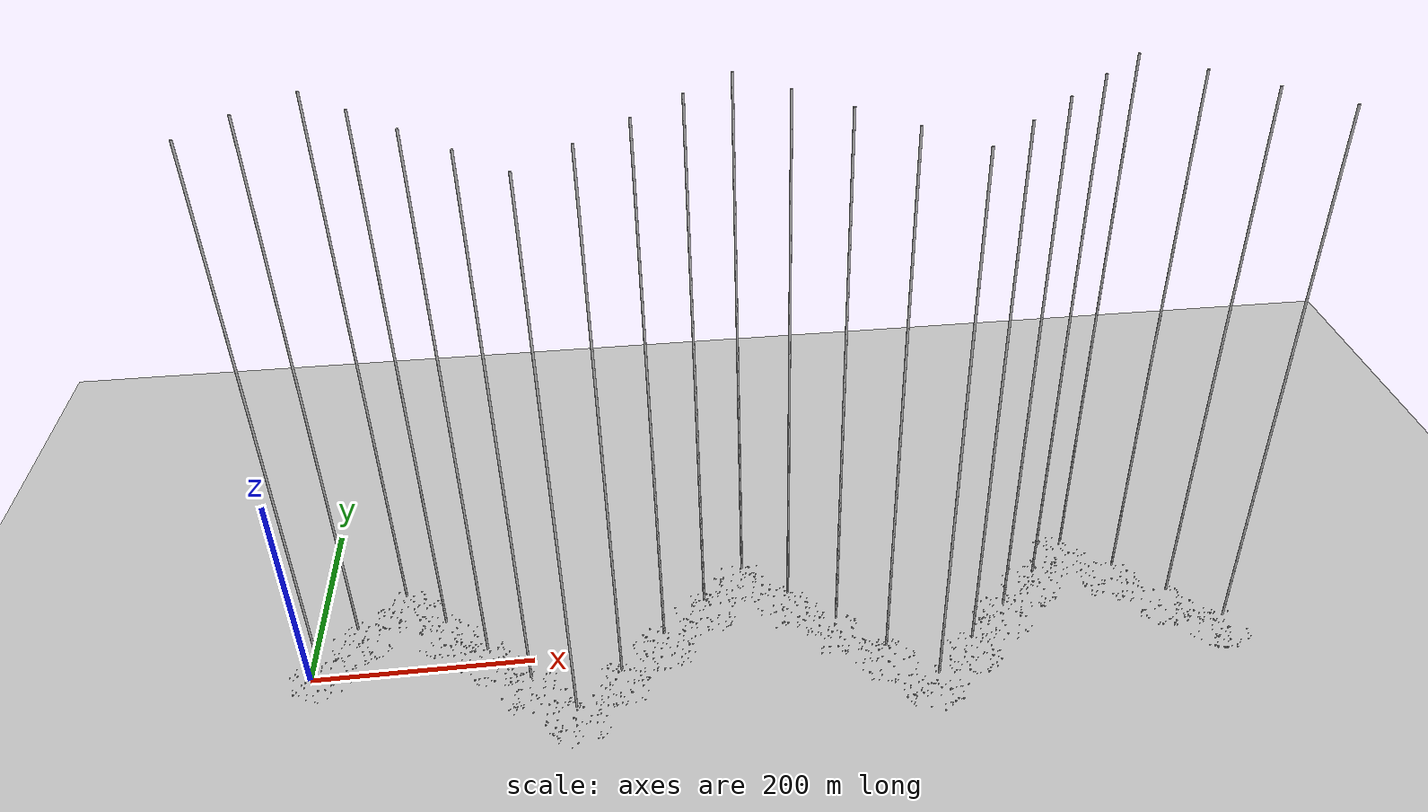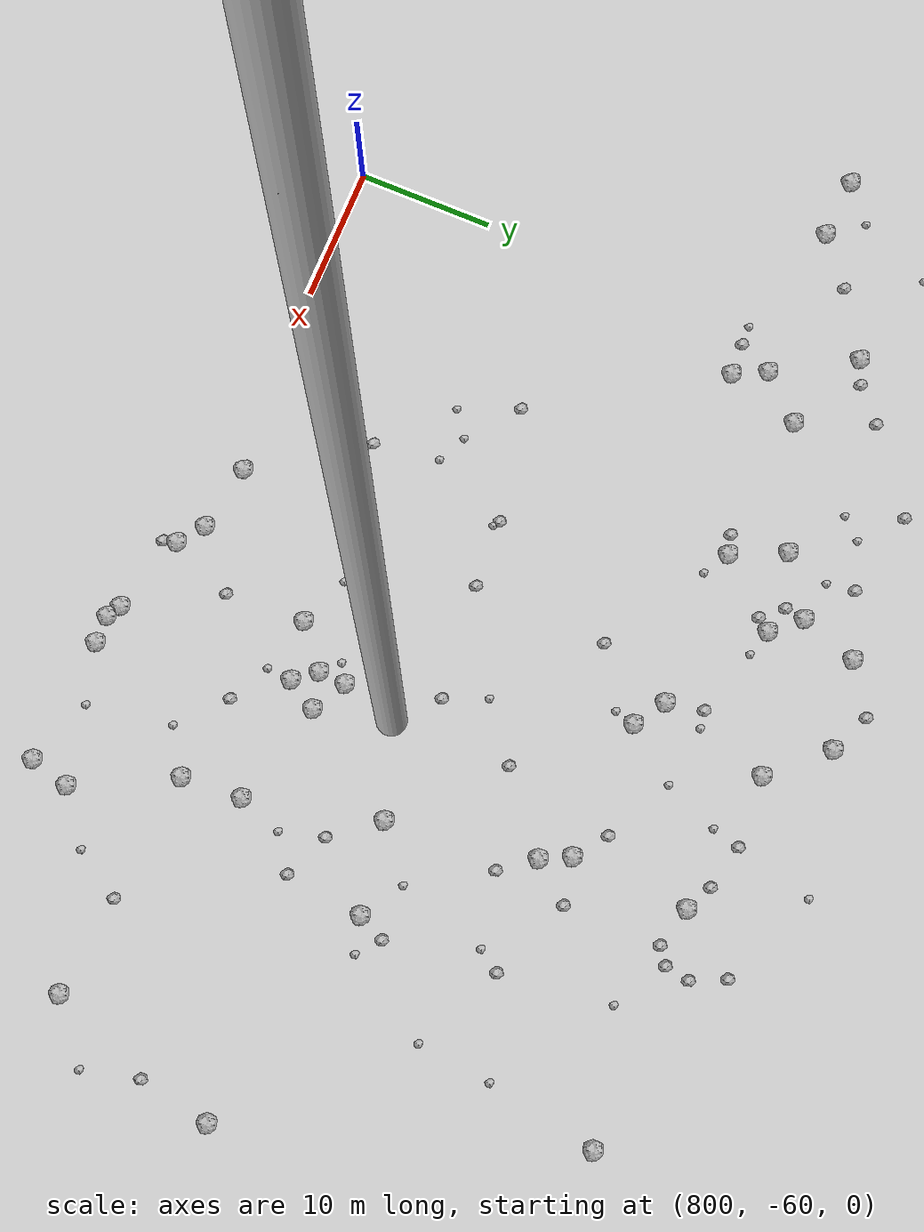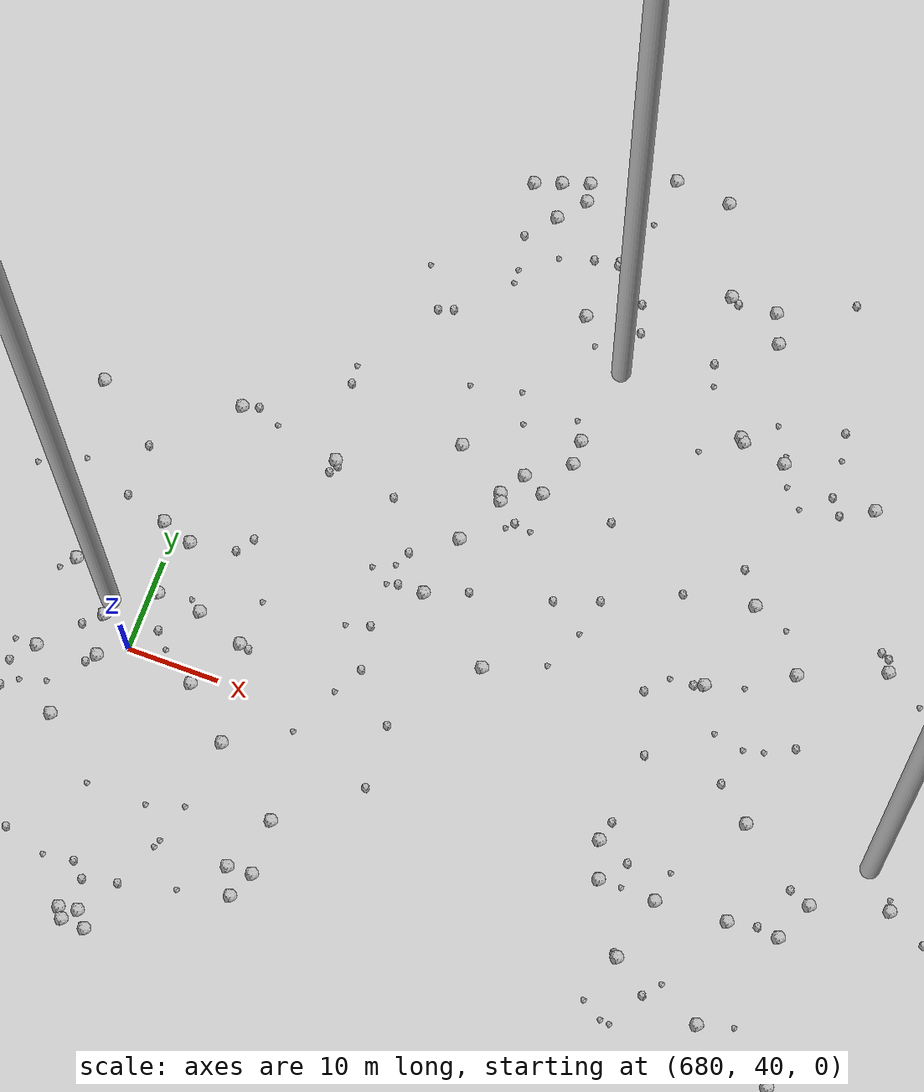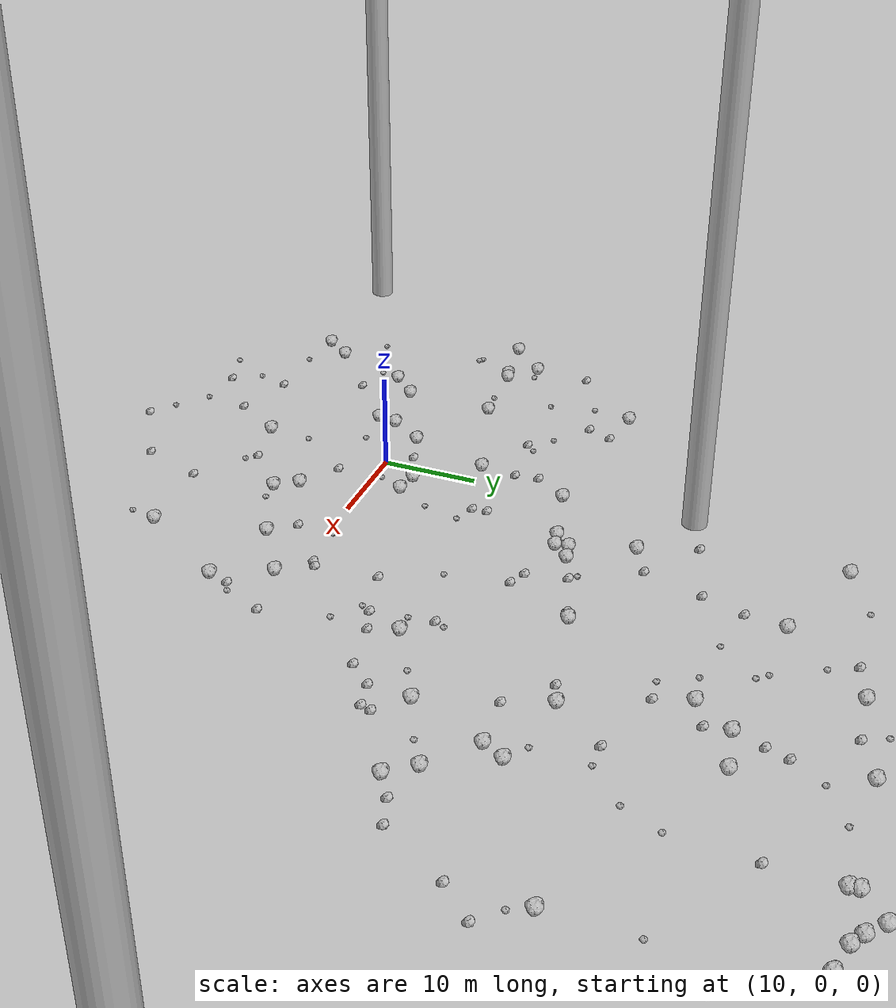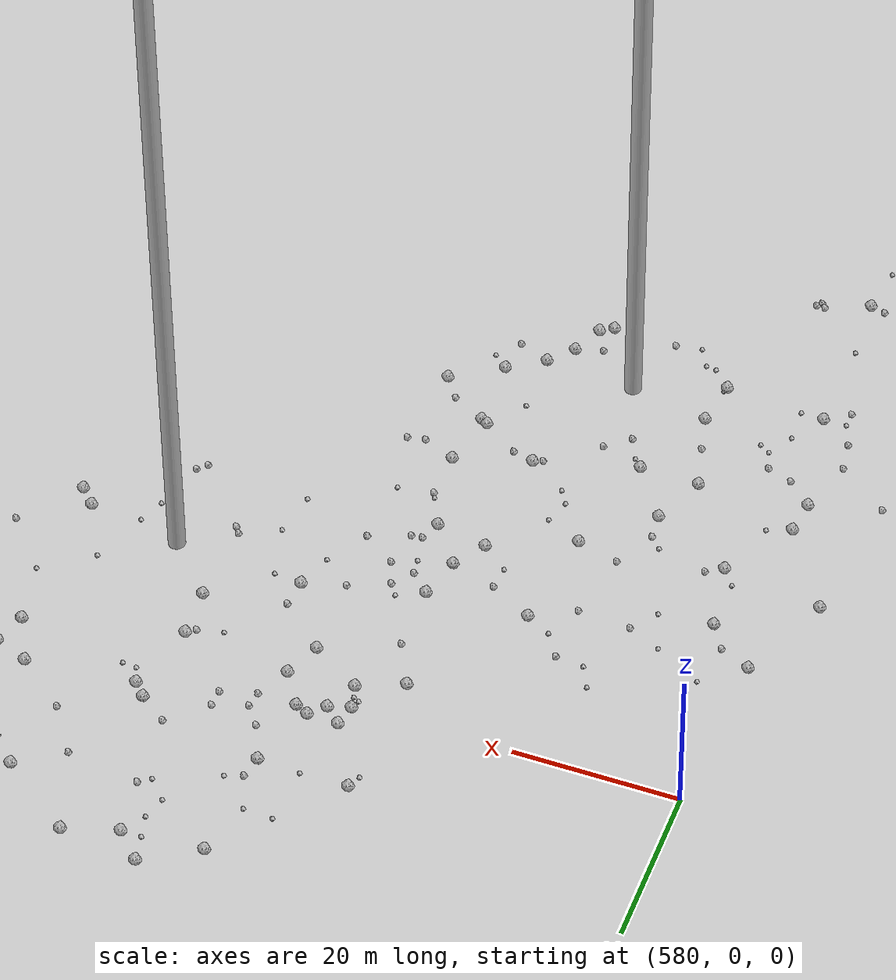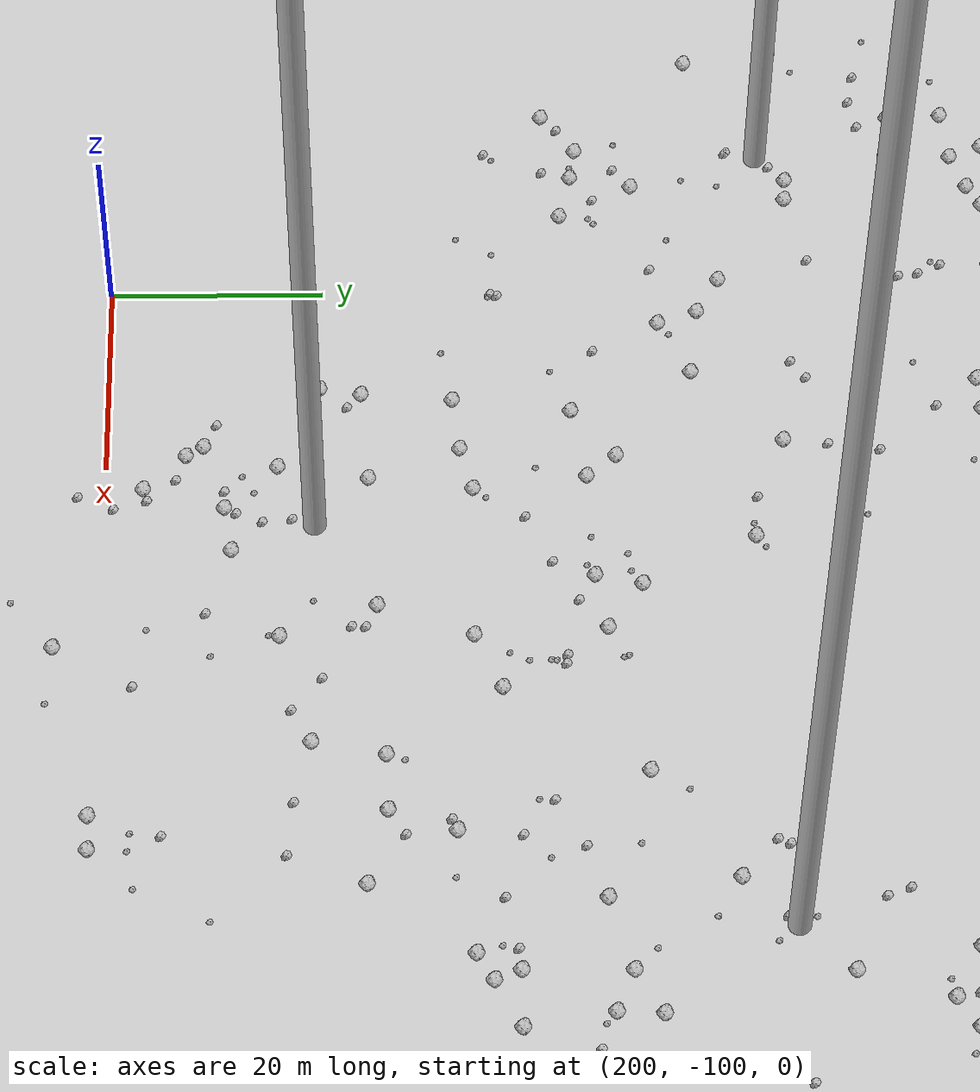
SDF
<sdf version="1.6">
 <world name="default">
  <include><uri>model://custom_ground</uri></include>
  <include><uri>model://sun</uri></include>
  <spherical_coordinates>
   <surface_model>EARTH_WGS84</surface_model>
   <latitude_deg>38.161479</latitude_deg>
   <longitude_deg>-122.454630</longitude_deg>
   <elevation>488.0</elevation>
   <heading_deg>90</heading_deg>
  </spherical_coordinates>
  <model name="rock1_0_0">
   <include><uri>model://rock1</uri><pose>1.7441989658180965 -4.541443888883222 0.5 0 0 0</pose></include>
  </model>
  <model name="rock1_0_1">
   <include><uri>model://rock1</uri><pose>-13.404597002256825 5.324897894672709 0.5 0 0 0</pose></include>
  </model>
  <model name="rock1_0_2">
   <include><uri>model://rock1</uri><pose>12.20609081366284 3.955230214134936 0.5 0 0 0</pose></include>
  </model>
  <model name="rock1_0_3">
   <include><uri>model://rock1</uri><pose>-4.752510207070193 -3.5096527414687557 0.5 0 0 0</pose></include>
  </model>
  <model name="rock1_0_4">
   <include><uri>model://rock1</uri><pose>16.968787575839727 21.545141732129025 0.5 0 0 0</pose></include>
  </model>
  <model name="rock1_0_5">
   <include><uri>model://rock1</uri><pose>7.443427374723054 9.911052004515241 0.5 0 0 0</pose></include>
  </model>
  <model name="rock1_0_6">
   <include><uri>model://rock1</uri><pose>-4.368428407281986 6.200212980525031 0.5 0 0 0</pose></include>
  </model>
  <model name="rock1_0_7">
   <include><uri>model://rock1</uri><pose>35.851268228480784 -7.289535602656056 0.5 0 0 0</pose></include>
  </model>
  <model name="rock1_0_8">
   <include><uri>model://rock1</uri><pose>19.113921167531373 -8.91072955189243 0.5 0 0 0</pose></include>
  </model>
  <model name="rock1_0_9">
   <include><uri>model://rock1</uri><pose>20.51355270095273 23.693787663201675 0.5 0 0 0</pose></include>
  </model>
  <model name="rock1_0_10">
   <include><uri>model://rock1</uri><pose>4.674990438943599 1.2339847448792156 0.5 0 0 0</pose></include>
  </model>
  <model name="rock1_0_11">
   <include><uri>model://rock1</uri><pose>33.077464467962635 -1.7090198296084331 0.5 0 0 0</pose></include>
  </model>
  <model name="rock1_0_12">
   <include><uri>model://rock1</uri><pose>29.36429832266817 -17.192968930137148 0.5 0 0 0</pose></include>
  </model>
  <model name="rock1_0_13">
   <include><uri>model://rock1</uri><pose>-13.041767352217501 -17.39051808808277 0.5 0 0 0</pose></include>
  </model>
  <model name="rock1_0_14">
   <include><uri>model://rock1</uri><pose>18.826650474783257 21.959737409667916 0.5 0 0 0</pose></include>
  </model>
  <model name="rock1_0_15">
   <include><uri>model://rock1</uri><pose>-19.513036122775866 4.410060382286311 0.5 0 0 0</pose></include>
  </model>
  <model name="rock1_0_16">
   <include><uri>model://rock1</uri><pose>-10.80904108907301 -14.55349985794777 0.5 0 0 0</pose></include>
  </model>
  <model name="rock1_0_17">
   <include><uri>model://rock1</uri><pose>-7.567404552320953 -6.258959112814068 0.5 0 0 0</pose></include>
  </model>
  <model name="rock1_0_18">
   <include><uri>model://rock1</uri><pose>10.06097732312016 19.80940463895466 0.5 0 0 0</pose></include>
  </model>
  <model name="rock1_0_19">
   <include><uri>model://rock1</uri><pose>-8.110701095564888 21.555632092715 0.5 0 0 0</pose></include>
  </model>
  <model name="rock1_0_20">
   <include><uri>model://rock1</uri><pose>-12.512990543340116 5.569673976554576 0.5 0 0 0</pose></include>
  </model>
  <model name="rock1_0_21">
   <include><uri>model://rock1</uri><pose>-15.503592642710009 8.203031752842449 0.5 0 0 0</pose></include>
  </model>
  <model name="rock1_0_22">
   <include><uri>model://rock1</uri><pose>2.1541461405173976 -2.385737802782952 0.5 0 0 0</pose></include>
  </model>
  <model name="rock1_0_23">
   <include><uri>model://rock1</uri><pose>14.777425246217376 3.5931416034266164 0.5 0 0 0</pose></include>
  </model>
  <model name="rock1_0_24">
   <include><uri>model://rock1</uri><pose>17.609374279479006 -6.605129817921679 0.5 0 0 0</pose></include>
  </model>
  <model name="rock1_0_25">
   <include><uri>model://rock1</uri><pose>27.106305291632104 -5.616778246182172 0.5 0 0 0</pose></include>
  </model>
  <model name="rock1_0_26">
   <include><uri>model://rock1</uri><pose>8.582283861626781 -14.519798148456966 0.5 0 0 0</pose></include>
  </model>
  <model name="rock2_0_0">
   <include><uri>model://rock2</uri><pose>13.439247718313666 -4.038057373987609 0.3 0 0 0</pose></include>
  </model>
  <model name="rock2_0_1">
   <include><uri>model://rock2</uri><pose>30.1526163855251 1.0605685662575297 0.3 0 0 0</pose></include>
  </model>
  <model name="rock2_0_2">
   <include><uri>model://rock2</uri><pose>36.45380897527731 -5.030456786254881 0.3 0 0 0</pose></include>
  </model>
  <model name="rock2_0_3">
   <include><uri>model://rock2</uri><pose>-0.4680137944375993 -24.18405938838902 0.3 0 0 0</pose></include>
  </model>
  <model name="rock2_0_4">
   <include><uri>model://rock2</uri><pose>-4.471646086975472 18.155136783271296 0.3 0 0 0</pose></include>
  </model>
  <model name="rock2_0_5">
   <include><uri>model://rock2</uri><pose>17.750754326667995 -24.351055277342127 0.3 0 0 0</pose></include>
  </model>
  <model name="rock2_0_6">
   <include><uri>model://rock2</uri><pose>14.207854688793617 -13.23853790098861 0.3 0 0 0</pose></include>
  </model>
  <model name="rock2_0_7">
   <include><uri>model://rock2</uri><pose>-4.494064473172889 -9.370045492627291 0.3 0 0 0</pose></include>
  </model>
  <model name="rock2_0_8">
   <include><uri>model://rock2</uri><pose>35.65860997187316 9.521984605721393 0.3 0 0 0</pose></include>
  </model>
  <model name="rock2_0_9">
   <include><uri>model://rock2</uri><pose>8.358292422337932 2.4484556313392076 0.3 0 0 0</pose></include>
  </model>
  <model name="rock2_0_10">
   <include><uri>model://rock2</uri><pose>1.280208281331376 12.94998698714916 0.3 0 0 0</pose></include>
  </model>
  <model name="rock2_0_11">
   <include><uri>model://rock2</uri><pose>-3.3872200268249237 20.79912559430919 0.3 0 0 0</pose></include>
  </model>
  <model name="rock2_0_12">
   <include><uri>model://rock2</uri><pose>24.52571408322514 20.849674806523538 0.3 0 0 0</pose></include>
  </model>
  <model name="rock2_0_13">
   <include><uri>model://rock2</uri><pose>7.750661332867097 13.808975743368435 0.3 0 0 0</pose></include>
  </model>
  <model name="rock2_0_14">
   <include><uri>model://rock2</uri><pose>10.113739902736853 -28.98634026870649 0.3 0 0 0</pose></include>
  </model>
  <model name="rock2_0_15">
   <include><uri>model://rock2</uri><pose>15.439533294924196 13.550077691359675 0.3 0 0 0</pose></include>
  </model>
  <model name="rock2_0_16">
   <include><uri>model://rock2</uri><pose>15.578526252415088 11.986212680449682 0.3 0 0 0</pose></include>
  </model>
  <model name="rock2_0_17">
   <include><uri>model://rock2</uri><pose>-15.227507929421103 14.334706564312881 0.3 0 0 0</pose></include>
  </model>
  <model name="rock2_0_18">
   <include><uri>model://rock2</uri><pose>30.2758815261108 8.01736432825669 0.3 0 0 0</pose></include>
  </model>
  <model name="rock2_0_19">
   <include><uri>model://rock2</uri><pose>20.144457134853297 -17.80134735558482 0.3 0 0 0</pose></include>
  </model>
  <model name="rock2_0_20">
   <include><uri>model://rock2</uri><pose>39.29643396346905 -0.3526473152272942 0.3 0 0 0</pose></include>
  </model>
  <model name="rock2_0_21">
   <include><uri>model://rock2</uri><pose>30.88455966667464 1.581086685748872 0.3 0 0 0</pose></include>
  </model>
  <model name="rock2_0_22">
   <include><uri>model://rock2</uri><pose>7.433258889965863 16.330302350566022 0.3 0 0 0</pose></include>
  </model>
  <model name="rock2_0_23">
   <include><uri>model://rock2</uri><pose>-1.2887203228571522 -17.913700428089655 0.3 0 0 0</pose></include>
  </model>
  <model name="rock2_0_24">
   <include><uri>model://rock2</uri><pose>5.021417103852933 -19.77521231129661 0.3 0 0 0</pose></include>
  </model>
  <model name="rock2_0_25">
   <include><uri>model://rock2</uri><pose>-8.284445007334806 21.443505467198264 0.3 0 0 0</pose></include>
  </model>
  <model name="rock2_0_26">
   <include><uri>model://rock2</uri><pose>24.87622872800553 -3.181413551128877 0.3 0 0 0</pose></include>
  </model>
  <model name="rock3_0_0">
   <include><uri>model://rock3</uri><pose>7.481856632211237 -27.185818372834422 0.2 0 0 0</pose></include>
  </model>
  <model name="rock3_0_1">
   <include><uri>model://rock3</uri><pose>37.66394863601921 6.412303019151267 0.2 0 0 0</pose></include>
  </model>
  <model name="rock3_0_2">
   <include><uri>model://rock3</uri><pose>21.150154536639825 -8.770187768782844 0.2 0 0 0</pose></include>
  </model>
  <model name="rock3_0_3">
   <include><uri>model://rock3</uri><pose>-13.909562473053311 8.352330755953943 0.2 0 0 0</pose></include>
  </model>
  <model name="rock3_0_4">
   <include><uri>model://rock3</uri><pose>-14.863604572323457 -10.819276891992715 0.2 0 0 0</pose></include>
  </model>
  <model name="rock3_0_5">
   <include><uri>model://rock3</uri><pose>28.526468773956253 -20.18954643881068 0.2 0 0 0</pose></include>
  </model>
  <model name="rock3_0_6">
   <include><uri>model://rock3</uri><pose>17.692348560668037 11.075514236516632 0.2 0 0 0</pose></include>
  </model>
  <model name="rock3_0_7">
   <include><uri>model://rock3</uri><pose>13.15327357339116 0.8208902313712443 0.2 0 0 0</pose></include>
  </model>
  <model name="rock3_0_8">
   <include><uri>model://rock3</uri><pose>-7.522878322050273 5.729892467095773 0.2 0 0 0</pose></include>
  </model>
  <model name="rock3_0_9">
   <include><uri>model://rock3</uri><pose>8.747061609098836 -9.868601824658413 0.2 0 0 0</pose></include>
  </model>
  <model name="rock3_0_10">
   <include><uri>model://rock3</uri><pose>-15.573297042432426 0.8364740547491039 0.2 0 0 0</pose></include>
  </model>
  <model name="rock3_0_11">
   <include><uri>model://rock3</uri><pose>15.042135865651588 -14.330774988431102 0.2 0 0 0</pose></include>
  </model>
  <model name="rock3_0_12">
   <include><uri>model://rock3</uri><pose>-4.972354249695048 -25.640425497829117 0.2 0 0 0</pose></include>
  </model>
  <model name="rock3_0_13">
   <include><uri>model://rock3</uri><pose>-8.414550585468874 -8.520963805370336 0.2 0 0 0</pose></include>
  </model>
  <model name="rock3_0_14">
   <include><uri>model://rock3</uri><pose>-9.041264775318705 17.28867163356567 0.2 0 0 0</pose></include>
  </model>
  <model name="rock3_0_15">
   <include><uri>model://rock3</uri><pose>4.38591692423487 -24.60227018869601 0.2 0 0 0</pose></include>
  </model>
  <model name="rock3_0_16">
   <include><uri>model://rock3</uri><pose>-0.8789625092068292 15.173009535097059 0.2 0 0 0</pose></include>
  </model>
  <model name="rock3_0_17">
   <include><uri>model://rock3</uri><pose>-2.444175874599864 -21.329907068413995 0.2 0 0 0</pose></include>
  </model>
  <model name="rock3_0_18">
   <include><uri>model://rock3</uri><pose>16.689085612400326 7.19980154439029 0.2 0 0 0</pose></include>
  </model>
  <model name="rock3_0_19">
   <include><uri>model://rock3</uri><pose>24.86316431062376 0.7002784553257548 0.2 0 0 0</pose></include>
  </model>
  <model name="rock3_0_20">
   <include><uri>model://rock3</uri><pose>-8.01307661820309 12.424711472005377 0.2 0 0 0</pose></include>
  </model>
  <model name="rock3_0_21">
   <include><uri>model://rock3</uri><pose>-15.966619042205114 1.1791934471175693 0.2 0 0 0</pose></include>
  </model>
  <model name="rock3_0_22">
   <include><uri>model://rock3</uri><pose>34.9616188883321 8.448272518497618 0.2 0 0 0</pose></include>
  </model>
  <model name="rock3_0_23">
   <include><uri>model://rock3</uri><pose>6.194741409787888 -4.116238521185128 0.2 0 0 0</pose></include>
  </model>
  <model name="rock3_0_24">
   <include><uri>model://rock3</uri><pose>2.069368407686646 13.847723121405465 0.2 0 0 0</pose></include>
  </model>
  <model name="rock3_0_25">
   <include><uri>model://rock3</uri><pose>-8.279268636854946 -18.061280947927525 0.2 0 0 0</pose></include>
  </model>
  <model name="rock3_0_26">
   <include><uri>model://rock3</uri><pose>37.502154184586814 -4.501525369651166 0.2 0 0 0</pose></include>
  </model>
  <model name="rock1_1_0">
   <include><uri>model://rock1</uri><pose>49.23381555723444 25.920158676424478 0.5 0 0 0</pose></include>
  </model>
  <model name="rock1_1_1">
   <include><uri>model://rock1</uri><pose>49.75385291054477 65.40162785062506 0.5 0 0 0</pose></include>
  </model>
  <model name="rock1_1_2">
   <include><uri>model://rock1</uri><pose>53.84656977322239 22.12407039577195 0.5 0 0 0</pose></include>
  </model>
  <model name="rock1_1_3">
   <include><uri>model://rock1</uri><pose>54.37777983528289 57.18217469378764 0.5 0 0 0</pose></include>
  </model>
  <model name="rock1_1_4">
   <include><uri>model://rock1</uri><pose>29.92844183881703 27.023254530122742 0.5 0 0 0</pose></include>
  </model>
  <model name="rock1_1_5">
   <include><uri>model://rock1</uri><pose>31.48334659106584 54.60976239997855 0.5 0 0 0</pose></include>
  </model>
  <model name="rock1_1_6">
   <include><uri>model://rock1</uri><pose>52.14992214008751 63.901008926541216 0.5 0 0 0</pose></include>
  </model>
  <model name="rock1_1_7">
   <include><uri>model://rock1</uri><pose>43.98949110355689 62.92009047387507 0.5 0 0 0</pose></include>
  </model>
  <model name="rock1_1_8">
   <include><uri>model://rock1</uri><pose>46.039434675097226 18.08197544806867 0.5 0 0 0</pose></include>
  </model>
  <model name="rock1_1_9">
   <include><uri>model://rock1</uri><pose>41.58498084878165 57.15690392088035 0.5 0 0 0</pose></include>
  </model>
  <model name="rock1_1_10">
   <include><uri>model://rock1</uri><pose>57.03750271001714 60.54751287192846 0.5 0 0 0</pose></include>
  </model>
  <model name="rock1_1_11">
   <include><uri>model://rock1</uri><pose>44.705319911261135 45.70921391719443 0.5 0 0 0</pose></include>
  </model>
  <model name="rock1_1_12">
   <include><uri>model://rock1</uri><pose>39.96946034398404 44.828962658485985 0.5 0 0 0</pose></include>
  </model>
  <model name="rock1_1_13">
   <include><uri>model://rock1</uri><pose>36.47126253163707 69.1089613536297 0.5 0 0 0</pose></include>
  </model>
  <model name="rock1_1_14">
   <include><uri>model://rock1</uri><pose>12.845384013645996 49.86779191119008 0.5 0 0 0</pose></include>
  </model>
  <model name="rock1_1_15">
   <include><uri>model://rock1</uri><pose>23.81869642030872 46.111467044645316 0.5 0 0 0</pose></include>
  </model>
  <model name="rock1_1_16">
   <include><uri>model://rock1</uri><pose>54.295441678626986 58.05567026251783 0.5 0 0 0</pose></include>
  </model>
  <model name="rock1_1_17">
   <include><uri>model://rock1</uri><pose>37.401827649438786 13.297440405695674 0.5 0 0 0</pose></include>
  </model>
  <model name="rock1_1_18">
   <include><uri>model://rock1</uri><pose>16.463853980761186 29.642584943972768 0.5 0 0 0</pose></include>
  </model>
  <model name="rock1_1_19">
   <include><uri>model://rock1</uri><pose>55.847696863751196 19.548529969137007 0.5 0 0 0</pose></include>
  </model>
  <model name="rock1_1_20">
   <include><uri>model://rock1</uri><pose>37.181622953702615 40.93965848521698 0.5 0 0 0</pose></include>
  </model>
  <model name="rock1_1_21">
   <include><uri>model://rock1</uri><pose>65.20091705284374 36.09274334587418 0.5 0 0 0</pose></include>
  </model>
  <model name="rock1_1_22">
   <include><uri>model://rock1</uri><pose>63.068583105115806 57.697298139980234 0.5 0 0 0</pose></include>
  </model>
  <model name="rock1_1_23">
   <include><uri>model://rock1</uri><pose>50.47273567091437 28.15538910529425 0.5 0 0 0</pose></include>
  </model>
  <model name="rock1_1_24">
   <include><uri>model://rock1</uri><pose>43.42636267048559 62.68960873352183 0.5 0 0 0</pose></include>
  </model>
  <model name="rock1_1_25">
   <include><uri>model://rock1</uri><pose>41.921351453328576 29.90875238528809 0.5 0 0 0</pose></include>
  </model>
  <model name="rock1_1_26">
   <include><uri>model://rock1</uri><pose>18.632021446977642 23.27988465978055 0.5 0 0 0</pose></include>
  </model>
  <model name="rock2_1_0">
   <include><uri>model://rock2</uri><pose>40.21986313022052 42.42585788150103 0.3 0 0 0</pose></include>
  </model>
  <model name="rock2_1_1">
   <include><uri>model://rock2</uri><pose>38.25292372877503 10.43273185758837 0.3 0 0 0</pose></include>
  </model>
  <model name="rock2_1_2">
   <include><uri>model://rock2</uri><pose>23.716916204906177 25.002701125281593 0.3 0 0 0</pose></include>
  </model>
  <model name="rock2_1_3">
   <include><uri>model://rock2</uri><pose>39.549766702213994 29.100930708883197 0.3 0 0 0</pose></include>
  </model>
  <model name="rock2_1_4">
   <include><uri>model://rock2</uri><pose>21.820565700171322 37.61404763145168 0.3 0 0 0</pose></include>
  </model>
  <model name="rock2_1_5">
   <include><uri>model://rock2</uri><pose>54.25657983390761 50.641228701560244 0.3 0 0 0</pose></include>
  </model>
  <model name="rock2_1_6">
   <include><uri>model://rock2</uri><pose>23.22391382461923 42.000824633596324 0.3 0 0 0</pose></include>
  </model>
  <model name="rock2_1_7">
   <include><uri>model://rock2</uri><pose>45.62948431526431 13.790136071534196 0.3 0 0 0</pose></include>
  </model>
  <model name="rock2_1_8">
   <include><uri>model://rock2</uri><pose>34.883103433389735 15.807789056860903 0.3 0 0 0</pose></include>
  </model>
  <model name="rock2_1_9">
   <include><uri>model://rock2</uri><pose>26.408276089930556 20.05168394725317 0.3 0 0 0</pose></include>
  </model>
  <model name="rock2_1_10">
   <include><uri>model://rock2</uri><pose>41.63737432972799 50.13761052564218 0.3 0 0 0</pose></include>
  </model>
  <model name="rock2_1_11">
   <include><uri>model://rock2</uri><pose>27.16148981449119 53.34441378658291 0.3 0 0 0</pose></include>
  </model>
  <model name="rock2_1_12">
   <include><uri>model://rock2</uri><pose>37.01413288519794 55.14467751575263 0.3 0 0 0</pose></include>
  </model>
  <model name="rock2_1_13">
   <include><uri>model://rock2</uri><pose>48.76166639851752 15.503807127316144 0.3 0 0 0</pose></include>
  </model>
  <model name="rock2_1_14">
   <include><uri>model://rock2</uri><pose>19.93138760292546 31.41599925864728 0.3 0 0 0</pose></include>
  </model>
  <model name="rock2_1_15">
   <include><uri>model://rock2</uri><pose>43.44675352053495 11.410112271873775 0.3 0 0 0</pose></include>
  </model>
  <model name="rock2_1_16">
   <include><uri>model://rock2</uri><pose>61.21100450119922 22.139747388349562 0.3 0 0 0</pose></include>
  </model>
  <model name="rock2_1_17">
   <include><uri>model://rock2</uri><pose>28.876936540073388 26.574559008687427 0.3 0 0 0</pose></include>
  </model>
  <model name="rock2_1_18">
   <include><uri>model://rock2</uri><pose>40.93940890556807 47.92206532010123 0.3 0 0 0</pose></include>
  </model>
  <model name="rock2_1_19">
   <include><uri>model://rock2</uri><pose>48.421863186858204 14.417585304707941 0.3 0 0 0</pose></include>
  </model>
  <model name="rock2_1_20">
   <include><uri>model://rock2</uri><pose>65.167481086679 28.806053618983466 0.3 0 0 0</pose></include>
  </model>
  <model name="rock2_1_21">
   <include><uri>model://rock2</uri><pose>68.16650078001281 32.06471301693004 0.3 0 0 0</pose></include>
  </model>
  <model name="rock2_1_22">
   <include><uri>model://rock2</uri><pose>14.161993469551739 35.428587749762485 0.3 0 0 0</pose></include>
  </model>
  <model name="rock2_1_23">
   <include><uri>model://rock2</uri><pose>38.281413775427794 37.4318370962115 0.3 0 0 0</pose></include>
  </model>
  <model name="rock2_1_24">
   <include><uri>model://rock2</uri><pose>58.257884007704604 21.197877886117947 0.3 0 0 0</pose></include>
  </model>
  <model name="rock2_1_25">
   <include><uri>model://rock2</uri><pose>45.85121956383224 35.1905781037879 0.3 0 0 0</pose></include>
  </model>
  <model name="rock2_1_26">
   <include><uri>model://rock2</uri><pose>43.586953536722405 25.432282288650136 0.3 0 0 0</pose></include>
  </model>
  <model name="rock3_1_0">
   <include><uri>model://rock3</uri><pose>31.945107796295012 45.08064334577704 0.2 0 0 0</pose></include>
  </model>
  <model name="rock3_1_1">
   <include><uri>model://rock3</uri><pose>35.25392375633442 16.77695587255654 0.2 0 0 0</pose></include>
  </model>
  <model name="rock3_1_2">
   <include><uri>model://rock3</uri><pose>28.591501073827608 41.06521338890988 0.2 0 0 0</pose></include>
  </model>
  <model name="rock3_1_3">
   <include><uri>model://rock3</uri><pose>35.725507028595345 57.348449940124446 0.2 0 0 0</pose></include>
  </model>
  <model name="rock3_1_4">
   <include><uri>model://rock3</uri><pose>53.72536239122298 42.627938219595364 0.2 0 0 0</pose></include>
  </model>
  <model name="rock3_1_5">
   <include><uri>model://rock3</uri><pose>24.775499497558968 62.15285701568112 0.2 0 0 0</pose></include>
  </model>
  <model name="rock3_1_6">
   <include><uri>model://rock3</uri><pose>31.10341415546381 46.06077242179565 0.2 0 0 0</pose></include>
  </model>
  <model name="rock3_1_7">
   <include><uri>model://rock3</uri><pose>27.338116468867447 13.591438762312167 0.2 0 0 0</pose></include>
  </model>
  <model name="rock3_1_8">
   <include><uri>model://rock3</uri><pose>48.13685495026383 29.615750875658282 0.2 0 0 0</pose></include>
  </model>
  <model name="rock3_1_9">
   <include><uri>model://rock3</uri><pose>22.14226931077676 56.66567280412559 0.2 0 0 0</pose></include>
  </model>
  <model name="rock3_1_10">
   <include><uri>model://rock3</uri><pose>28.36598651951124 50.67795121046607 0.2 0 0 0</pose></include>
  </model>
  <model name="rock3_1_11">
   <include><uri>model://rock3</uri><pose>68.23395947784418 49.923095292096484 0.2 0 0 0</pose></include>
  </model>
  <model name="rock3_1_12">
   <include><uri>model://rock3</uri><pose>22.87823361393379 25.63663663899979 0.2 0 0 0</pose></include>
  </model>
  <model name="rock3_1_13">
   <include><uri>model://rock3</uri><pose>43.52631557365427 53.464981252595464 0.2 0 0 0</pose></include>
  </model>
  <model name="rock3_1_14">
   <include><uri>model://rock3</uri><pose>35.63491464319116 37.0756130287525 0.2 0 0 0</pose></include>
  </model>
  <model name="rock3_1_15">
   <include><uri>model://rock3</uri><pose>42.40040810139517 16.188753467421865 0.2 0 0 0</pose></include>
  </model>
  <model name="rock3_1_16">
   <include><uri>model://rock3</uri><pose>65.9422533106148 34.08389887597949 0.2 0 0 0</pose></include>
  </model>
  <model name="rock3_1_17">
   <include><uri>model://rock3</uri><pose>48.32368745966987 35.19811175463178 0.2 0 0 0</pose></include>
  </model>
  <model name="rock3_1_18">
   <include><uri>model://rock3</uri><pose>52.034312638467135 38.69207359747558 0.2 0 0 0</pose></include>
  </model>
  <model name="rock3_1_19">
   <include><uri>model://rock3</uri><pose>57.583850419214784 63.05680036380488 0.2 0 0 0</pose></include>
  </model>
  <model name="rock3_1_20">
   <include><uri>model://rock3</uri><pose>27.172237161868786 64.15239236091045 0.2 0 0 0</pose></include>
  </model>
  <model name="rock3_1_21">
   <include><uri>model://rock3</uri><pose>18.62347890561947 52.822880137780565 0.2 0 0 0</pose></include>
  </model>
  <model name="rock3_1_22">
   <include><uri>model://rock3</uri><pose>35.0604721439028 13.125022431067006 0.2 0 0 0</pose></include>
  </model>
  <model name="rock3_1_23">
   <include><uri>model://rock3</uri><pose>33.71423590945726 40.44569043144118 0.2 0 0 0</pose></include>
  </model>
  <model name="rock3_1_24">
   <include><uri>model://rock3</uri><pose>64.89172073781711 44.356452695149194 0.2 0 0 0</pose></include>
  </model>
  <model name="rock3_1_25">
   <include><uri>model://rock3</uri><pose>50.787864048553985 20.347019332131417 0.2 0 0 0</pose></include>
  </model>
  <model name="rock3_1_26">
   <include><uri>model://rock3</uri><pose>47.626882539345175 56.0784188625619 0.2 0 0 0</pose></include>
  </model>
  <model name="rock1_2_0">
   <include><uri>model://rock1</uri><pose>87.71365269010587 73.2683805264094 0.5 0 0 0</pose></include>
  </model>
  <model name="rock1_2_1">
   <include><uri>model://rock1</uri><pose>60.06241144276447 58.325039252430535 0.5 0 0 0</pose></include>
  </model>
  <model name="rock1_2_2">
   <include><uri>model://rock1</uri><pose>98.21340913099115 86.15235729816567 0.5 0 0 0</pose></include>
  </model>
  <model name="rock1_2_3">
   <include><uri>model://rock1</uri><pose>105.3184906350237 91.56967554130216 0.5 0 0 0</pose></include>
  </model>
  <model name="rock1_2_4">
   <include><uri>model://rock1</uri><pose>62.97904839873728 73.8270933032411 0.5 0 0 0</pose></include>
  </model>
  <model name="rock1_2_5">
   <include><uri>model://rock1</uri><pose>59.732781317422806 85.11074616209677 0.5 0 0 0</pose></include>
  </model>
  <model name="rock1_2_6">
   <include><uri>model://rock1</uri><pose>87.7087549625566 86.9862169956424 0.5 0 0 0</pose></include>
  </model>
  <model name="rock1_2_7">
   <include><uri>model://rock1</uri><pose>91.83399727100237 101.9531347404751 0.5 0 0 0</pose></include>
  </model>
  <model name="rock1_2_8">
   <include><uri>model://rock1</uri><pose>58.686516809103225 59.14513956947809 0.5 0 0 0</pose></include>
  </model>
  <model name="rock1_2_9">
   <include><uri>model://rock1</uri><pose>67.0921831759344 106.97712301886759 0.5 0 0 0</pose></include>
  </model>
  <model name="rock1_2_10">
   <include><uri>model://rock1</uri><pose>54.19962439680639 84.92167740208134 0.5 0 0 0</pose></include>
  </model>
  <model name="rock1_2_11">
   <include><uri>model://rock1</uri><pose>63.68297894303031 96.88257407598755 0.5 0 0 0</pose></include>
  </model>
  <model name="rock1_2_12">
   <include><uri>model://rock1</uri><pose>93.40292089510247 94.80524008861639 0.5 0 0 0</pose></include>
  </model>
  <model name="rock1_2_13">
   <include><uri>model://rock1</uri><pose>71.54651483417464 64.98582740966303 0.5 0 0 0</pose></include>
  </model>
  <model name="rock1_2_14">
   <include><uri>model://rock1</uri><pose>81.61486065526665 100.82837044715548 0.5 0 0 0</pose></include>
  </model>
  <model name="rock1_2_15">
   <include><uri>model://rock1</uri><pose>90.90629164522952 66.18643944194847 0.5 0 0 0</pose></include>
  </model>
  <model name="rock1_2_16">
   <include><uri>model://rock1</uri><pose>102.72424840127127 84.25949772834436 0.5 0 0 0</pose></include>
  </model>
  <model name="rock1_2_17">
   <include><uri>model://rock1</uri><pose>72.31747251637185 68.38648169368253 0.5 0 0 0</pose></include>
  </model>
  <model name="rock1_2_18">
   <include><uri>model://rock1</uri><pose>71.68951382400724 79.2402631246609 0.5 0 0 0</pose></include>
  </model>
  <model name="rock1_2_19">
   <include><uri>model://rock1</uri><pose>83.78987714501932 81.67558107461056 0.5 0 0 0</pose></include>
  </model>
  <model name="rock1_2_20">
   <include><uri>model://rock1</uri><pose>92.81993076354244 70.43233734303092 0.5 0 0 0</pose></include>
  </model>
  <model name="rock1_2_21">
   <include><uri>model://rock1</uri><pose>50.17556358760404 81.3419889802729 0.5 0 0 0</pose></include>
  </model>
  <model name="rock1_2_22">
   <include><uri>model://rock1</uri><pose>88.78689747799396 106.21669154276341 0.5 0 0 0</pose></include>
  </model>
  <model name="rock1_2_23">
   <include><uri>model://rock1</uri><pose>95.6318360332361 81.76406367770618 0.5 0 0 0</pose></include>
  </model>
  <model name="rock1_2_24">
   <include><uri>model://rock1</uri><pose>99.55307425823128 63.31137632621876 0.5 0 0 0</pose></include>
  </model>
  <model name="rock1_2_25">
   <include><uri>model://rock1</uri><pose>64.10983176499302 79.27843108453192 0.5 0 0 0</pose></include>
  </model>
  <model name="rock1_2_26">
   <include><uri>model://rock1</uri><pose>94.9439396732259 57.68609183466421 0.5 0 0 0</pose></include>
  </model>
  <model name="rock2_2_0">
   <include><uri>model://rock2</uri><pose>106.79280498667013 67.92225999528702 0.3 0 0 0</pose></include>
  </model>
  <model name="rock2_2_1">
   <include><uri>model://rock2</uri><pose>77.37731554490642 86.45496198400843 0.3 0 0 0</pose></include>
  </model>
  <model name="rock2_2_2">
   <include><uri>model://rock2</uri><pose>101.37913453379298 69.44198798391636 0.3 0 0 0</pose></include>
  </model>
  <model name="rock2_2_3">
   <include><uri>model://rock2</uri><pose>79.02601388453178 95.98709188338012 0.3 0 0 0</pose></include>
  </model>
  <model name="rock2_2_4">
   <include><uri>model://rock2</uri><pose>101.66452690301007 88.62603371776075 0.3 0 0 0</pose></include>
  </model>
  <model name="rock2_2_5">
   <include><uri>model://rock2</uri><pose>91.5487903857813 95.42359703035282 0.3 0 0 0</pose></include>
  </model>
  <model name="rock2_2_6">
   <include><uri>model://rock2</uri><pose>72.0608923172248 58.854919313573646 0.3 0 0 0</pose></include>
  </model>
  <model name="rock2_2_7">
   <include><uri>model://rock2</uri><pose>98.38686906500855 93.39394089955692 0.3 0 0 0</pose></include>
  </model>
  <model name="rock2_2_8">
   <include><uri>model://rock2</uri><pose>73.43517245892838 51.95717818832553 0.3 0 0 0</pose></include>
  </model>
  <model name="rock2_2_9">
   <include><uri>model://rock2</uri><pose>51.554900623401046 73.76735910010603 0.3 0 0 0</pose></include>
  </model>
  <model name="rock2_2_10">
   <include><uri>model://rock2</uri><pose>82.17530535089676 93.32793156740154 0.3 0 0 0</pose></include>
  </model>
  <model name="rock2_2_11">
   <include><uri>model://rock2</uri><pose>52.403884771278356 83.81009623584534 0.3 0 0 0</pose></include>
  </model>
  <model name="rock2_2_12">
   <include><uri>model://rock2</uri><pose>68.73362266876879 72.20203713186284 0.3 0 0 0</pose></include>
  </model>
  <model name="rock2_2_13">
   <include><uri>model://rock2</uri><pose>56.009143836760586 76.55787176710056 0.3 0 0 0</pose></include>
  </model>
  <model name="rock2_2_14">
   <include><uri>model://rock2</uri><pose>103.26671503464965 83.47459055097491 0.3 0 0 0</pose></include>
  </model>
  <model name="rock2_2_15">
   <include><uri>model://rock2</uri><pose>76.48382350005048 107.3586286196122 0.3 0 0 0</pose></include>
  </model>
  <model name="rock2_2_16">
   <include><uri>model://rock2</uri><pose>55.99981395832571 81.64886538611523 0.3 0 0 0</pose></include>
  </model>
  <model name="rock2_2_17">
   <include><uri>model://rock2</uri><pose>91.64011985020224 101.5531117406634 0.3 0 0 0</pose></include>
  </model>
  <model name="rock2_2_18">
   <include><uri>model://rock2</uri><pose>86.8238297000301 85.27799991565533 0.3 0 0 0</pose></include>
  </model>
  <model name="rock2_2_19">
   <include><uri>model://rock2</uri><pose>78.31922893473246 57.53477669618544 0.3 0 0 0</pose></include>
  </model>
  <model name="rock2_2_20">
   <include><uri>model://rock2</uri><pose>63.13130755967298 93.1009474662264 0.3 0 0 0</pose></include>
  </model>
  <model name="rock2_2_21">
   <include><uri>model://rock2</uri><pose>107.75825417851955 87.36969447946574 0.3 0 0 0</pose></include>
  </model>
  <model name="rock2_2_22">
   <include><uri>model://rock2</uri><pose>94.45444723070769 70.51701661133384 0.3 0 0 0</pose></include>
  </model>
  <model name="rock2_2_23">
   <include><uri>model://rock2</uri><pose>96.19597761623152 68.19829122518752 0.3 0 0 0</pose></include>
  </model>
  <model name="rock2_2_24">
   <include><uri>model://rock2</uri><pose>73.1371119336755 93.50870387556137 0.3 0 0 0</pose></include>
  </model>
  <model name="rock2_2_25">
   <include><uri>model://rock2</uri><pose>62.255272342658806 90.55943068323337 0.3 0 0 0</pose></include>
  </model>
  <model name="rock2_2_26">
   <include><uri>model://rock2</uri><pose>73.2380375255477 67.24840228528981 0.3 0 0 0</pose></include>
  </model>
  <model name="rock3_2_0">
   <include><uri>model://rock3</uri><pose>94.39968722030949 63.508482227301684 0.2 0 0 0</pose></include>
  </model>
  <model name="rock3_2_1">
   <include><uri>model://rock3</uri><pose>88.04391463958129 86.5765149047062 0.2 0 0 0</pose></include>
  </model>
  <model name="rock3_2_2">
   <include><uri>model://rock3</uri><pose>84.81145210159502 78.02596781521751 0.2 0 0 0</pose></include>
  </model>
  <model name="rock3_2_3">
   <include><uri>model://rock3</uri><pose>79.74392182905176 74.21237259350919 0.2 0 0 0</pose></include>
  </model>
  <model name="rock3_2_4">
   <include><uri>model://rock3</uri><pose>72.02029151203396 95.75332669544602 0.2 0 0 0</pose></include>
  </model>
  <model name="rock3_2_5">
   <include><uri>model://rock3</uri><pose>65.35601814453487 67.83164319690037 0.2 0 0 0</pose></include>
  </model>
  <model name="rock3_2_6">
   <include><uri>model://rock3</uri><pose>74.64018318473603 105.4801540229192 0.2 0 0 0</pose></include>
  </model>
  <model name="rock3_2_7">
   <include><uri>model://rock3</uri><pose>104.04998157625698 77.80484797351515 0.2 0 0 0</pose></include>
  </model>
  <model name="rock3_2_8">
   <include><uri>model://rock3</uri><pose>83.07094426466396 60.100613988043065 0.2 0 0 0</pose></include>
  </model>
  <model name="rock3_2_9">
   <include><uri>model://rock3</uri><pose>72.14856289832917 73.93697407088918 0.2 0 0 0</pose></include>
  </model>
  <model name="rock3_2_10">
   <include><uri>model://rock3</uri><pose>95.75726898235406 94.21135124880018 0.2 0 0 0</pose></include>
  </model>
  <model name="rock3_2_11">
   <include><uri>model://rock3</uri><pose>92.42271374288427 89.49071976199056 0.2 0 0 0</pose></include>
  </model>
  <model name="rock3_2_12">
   <include><uri>model://rock3</uri><pose>109.59632863523721 77.92599513000722 0.2 0 0 0</pose></include>
  </model>
  <model name="rock3_2_13">
   <include><uri>model://rock3</uri><pose>105.346189952028 93.6590265715422 0.2 0 0 0</pose></include>
  </model>
  <model name="rock3_2_14">
   <include><uri>model://rock3</uri><pose>58.820698585866126 99.60947799176223 0.2 0 0 0</pose></include>
  </model>
  <model name="rock3_2_15">
   <include><uri>model://rock3</uri><pose>76.64534973092171 66.47530562192131 0.2 0 0 0</pose></include>
  </model>
  <model name="rock3_2_16">
   <include><uri>model://rock3</uri><pose>98.23248134102897 58.50046003641738 0.2 0 0 0</pose></include>
  </model>
  <model name="rock3_2_17">
   <include><uri>model://rock3</uri><pose>97.04393069753955 81.91783905402724 0.2 0 0 0</pose></include>
  </model>
  <model name="rock3_2_18">
   <include><uri>model://rock3</uri><pose>89.47843694868871 103.50505646364257 0.2 0 0 0</pose></include>
  </model>
  <model name="rock3_2_19">
   <include><uri>model://rock3</uri><pose>100.05063987638235 89.24395264614466 0.2 0 0 0</pose></include>
  </model>
  <model name="rock3_2_20">
   <include><uri>model://rock3</uri><pose>55.218593559701205 89.47088776703879 0.2 0 0 0</pose></include>
  </model>
  <model name="rock3_2_21">
   <include><uri>model://rock3</uri><pose>71.64399673050147 83.6635991345564 0.2 0 0 0</pose></include>
  </model>
  <model name="rock3_2_22">
   <include><uri>model://rock3</uri><pose>102.41101515611035 77.313725428945 0.2 0 0 0</pose></include>
  </model>
  <model name="rock3_2_23">
   <include><uri>model://rock3</uri><pose>72.63406313529765 58.898966671216115 0.2 0 0 0</pose></include>
  </model>
  <model name="rock3_2_24">
   <include><uri>model://rock3</uri><pose>64.99543517941076 81.63453890937055 0.2 0 0 0</pose></include>
  </model>
  <model name="rock3_2_25">
   <include><uri>model://rock3</uri><pose>94.11389731583438 56.888442225450866 0.2 0 0 0</pose></include>
  </model>
  <model name="rock3_2_26">
   <include><uri>model://rock3</uri><pose>96.58526208100935 58.275337520425666 0.2 0 0 0</pose></include>
  </model>
  <model name="rock1_3_0">
   <include><uri>model://rock1</uri><pose>131.55938646531874 28.382999925399787 0.5 0 0 0</pose></include>
  </model>
  <model name="rock1_3_1">
   <include><uri>model://rock1</uri><pose>113.31622643290646 17.849618013985427 0.5 0 0 0</pose></include>
  </model>
  <model name="rock1_3_2">
   <include><uri>model://rock1</uri><pose>127.51401830623988 32.598717816842466 0.5 0 0 0</pose></include>
  </model>
  <model name="rock1_3_3">
   <include><uri>model://rock1</uri><pose>143.4331937123448 39.3299229846658 0.5 0 0 0</pose></include>
  </model>
  <model name="rock1_3_4">
   <include><uri>model://rock1</uri><pose>120.4345840511908 15.571456379197532 0.5 0 0 0</pose></include>
  </model>
  <model name="rock1_3_5">
   <include><uri>model://rock1</uri><pose>111.30428029223319 38.610174521607114 0.5 0 0 0</pose></include>
  </model>
  <model name="rock1_3_6">
   <include><uri>model://rock1</uri><pose>134.5042294537613 25.47648845109913 0.5 0 0 0</pose></include>
  </model>
  <model name="rock1_3_7">
   <include><uri>model://rock1</uri><pose>131.7808283311927 31.22508411036733 0.5 0 0 0</pose></include>
  </model>
  <model name="rock1_3_8">
   <include><uri>model://rock1</uri><pose>108.48765074884582 13.620533742518857 0.5 0 0 0</pose></include>
  </model>
  <model name="rock1_3_9">
   <include><uri>model://rock1</uri><pose>109.38966968031373 55.67739857690254 0.5 0 0 0</pose></include>
  </model>
  <model name="rock1_3_10">
   <include><uri>model://rock1</uri><pose>140.75601345390405 30.54789028842866 0.5 0 0 0</pose></include>
  </model>
  <model name="rock1_3_11">
   <include><uri>model://rock1</uri><pose>142.84395259562808 22.805271083630885 0.5 0 0 0</pose></include>
  </model>
  <model name="rock1_3_12">
   <include><uri>model://rock1</uri><pose>145.19317630168425 26.61155025780122 0.5 0 0 0</pose></include>
  </model>
  <model name="rock1_3_13">
   <include><uri>model://rock1</uri><pose>126.32965576723689 14.59478942630939 0.5 0 0 0</pose></include>
  </model>
  <model name="rock1_3_14">
   <include><uri>model://rock1</uri><pose>116.35171302336377 29.208413158272684 0.5 0 0 0</pose></include>
  </model>
  <model name="rock1_3_15">
   <include><uri>model://rock1</uri><pose>92.57163567811622 48.85550230440822 0.5 0 0 0</pose></include>
  </model>
  <model name="rock1_3_16">
   <include><uri>model://rock1</uri><pose>108.71319290645171 16.7659056310744 0.5 0 0 0</pose></include>
  </model>
  <model name="rock1_3_17">
   <include><uri>model://rock1</uri><pose>93.99522721677751 46.6945229358176 0.5 0 0 0</pose></include>
  </model>
  <model name="rock1_3_18">
   <include><uri>model://rock1</uri><pose>125.56876391890484 36.748523973753876 0.5 0 0 0</pose></include>
  </model>
  <model name="rock1_3_19">
   <include><uri>model://rock1</uri><pose>127.8520268015962 61.583427176449725 0.5 0 0 0</pose></include>
  </model>
  <model name="rock1_3_20">
   <include><uri>model://rock1</uri><pose>107.5639737754871 49.64189884647317 0.5 0 0 0</pose></include>
  </model>
  <model name="rock1_3_21">
   <include><uri>model://rock1</uri><pose>117.40902481951463 29.270291768138094 0.5 0 0 0</pose></include>
  </model>
  <model name="rock1_3_22">
   <include><uri>model://rock1</uri><pose>139.49539291458808 25.7886867361311 0.5 0 0 0</pose></include>
  </model>
  <model name="rock1_3_23">
   <include><uri>model://rock1</uri><pose>94.349118113988 51.39436828013269 0.5 0 0 0</pose></include>
  </model>
  <model name="rock1_3_24">
   <include><uri>model://rock1</uri><pose>122.81008602740346 26.408743285536357 0.5 0 0 0</pose></include>
  </model>
  <model name="rock1_3_25">
   <include><uri>model://rock1</uri><pose>136.45106413578128 53.41416453649308 0.5 0 0 0</pose></include>
  </model>
  <model name="rock1_3_26">
   <include><uri>model://rock1</uri><pose>96.38481269915687 54.16963492783341 0.5 0 0 0</pose></include>
  </model>
  <model name="rock2_3_0">
   <include><uri>model://rock2</uri><pose>130.76012552597882 35.851668707035174 0.3 0 0 0</pose></include>
  </model>
  <model name="rock2_3_1">
   <include><uri>model://rock2</uri><pose>142.283748295672 45.432028484881585 0.3 0 0 0</pose></include>
  </model>
  <model name="rock2_3_2">
   <include><uri>model://rock2</uri><pose>129.06098013127973 41.45337588658538 0.3 0 0 0</pose></include>
  </model>
  <model name="rock2_3_3">
   <include><uri>model://rock2</uri><pose>92.2090839890445 47.36571315819973 0.3 0 0 0</pose></include>
  </model>
  <model name="rock2_3_4">
   <include><uri>model://rock2</uri><pose>124.83581094362452 22.543671717062985 0.3 0 0 0</pose></include>
  </model>
  <model name="rock2_3_5">
   <include><uri>model://rock2</uri><pose>136.71255958205555 23.812776798745666 0.3 0 0 0</pose></include>
  </model>
  <model name="rock2_3_6">
   <include><uri>model://rock2</uri><pose>120.37718521510688 69.29928687859152 0.3 0 0 0</pose></include>
  </model>
  <model name="rock2_3_7">
   <include><uri>model://rock2</uri><pose>122.37343014085076 46.214887931208125 0.3 0 0 0</pose></include>
  </model>
  <model name="rock2_3_8">
   <include><uri>model://rock2</uri><pose>113.62909133050414 49.37457144363445 0.3 0 0 0</pose></include>
  </model>
  <model name="rock2_3_9">
   <include><uri>model://rock2</uri><pose>102.3829726358436 49.51955572744113 0.3 0 0 0</pose></include>
  </model>
  <model name="rock2_3_10">
   <include><uri>model://rock2</uri><pose>102.46683265796727 56.886496500684096 0.3 0 0 0</pose></include>
  </model>
  <model name="rock2_3_11">
   <include><uri>model://rock2</uri><pose>112.61498618002452 60.74550864471601 0.3 0 0 0</pose></include>
  </model>
  <model name="rock2_3_12">
   <include><uri>model://rock2</uri><pose>124.05703749411103 63.47040080911779 0.3 0 0 0</pose></include>
  </model>
  <model name="rock2_3_13">
   <include><uri>model://rock2</uri><pose>126.47291952853386 28.794430553098348 0.3 0 0 0</pose></include>
  </model>
  <model name="rock2_3_14">
   <include><uri>model://rock2</uri><pose>95.71940698075097 56.87065054839904 0.3 0 0 0</pose></include>
  </model>
  <model name="rock2_3_15">
   <include><uri>model://rock2</uri><pose>100.12470923186697 22.66615379063884 0.3 0 0 0</pose></include>
  </model>
  <model name="rock2_3_16">
   <include><uri>model://rock2</uri><pose>94.38979955829846 24.6678900379727 0.3 0 0 0</pose></include>
  </model>
  <model name="rock2_3_17">
   <include><uri>model://rock2</uri><pose>146.2237699731649 37.279973933840566 0.3 0 0 0</pose></include>
  </model>
  <model name="rock2_3_18">
   <include><uri>model://rock2</uri><pose>113.310680878289 27.66781030692707 0.3 0 0 0</pose></include>
  </model>
  <model name="rock2_3_19">
   <include><uri>model://rock2</uri><pose>129.3251289284304 58.783531140212105 0.3 0 0 0</pose></include>
  </model>
  <model name="rock2_3_20">
   <include><uri>model://rock2</uri><pose>122.05333206170904 28.501534663699548 0.3 0 0 0</pose></include>
  </model>
  <model name="rock2_3_21">
   <include><uri>model://rock2</uri><pose>111.68269415323942 47.84946168319097 0.3 0 0 0</pose></include>
  </model>
  <model name="rock2_3_22">
   <include><uri>model://rock2</uri><pose>135.9577232370109 16.080755709317913 0.3 0 0 0</pose></include>
  </model>
  <model name="rock2_3_23">
   <include><uri>model://rock2</uri><pose>135.50406665405697 26.657306856619186 0.3 0 0 0</pose></include>
  </model>
  <model name="rock2_3_24">
   <include><uri>model://rock2</uri><pose>104.71535709545368 17.009736215045187 0.3 0 0 0</pose></include>
  </model>
  <model name="rock2_3_25">
   <include><uri>model://rock2</uri><pose>115.49647955680081 14.003424360900992 0.3 0 0 0</pose></include>
  </model>
  <model name="rock2_3_26">
   <include><uri>model://rock2</uri><pose>125.94723517630857 52.17564645498655 0.3 0 0 0</pose></include>
  </model>
  <model name="rock3_3_0">
   <include><uri>model://rock3</uri><pose>137.3573011602453 30.7181990693187 0.2 0 0 0</pose></include>
  </model>
  <model name="rock3_3_1">
   <include><uri>model://rock3</uri><pose>132.50362868956546 17.88958512866519 0.2 0 0 0</pose></include>
  </model>
  <model name="rock3_3_2">
   <include><uri>model://rock3</uri><pose>111.7401596274849 63.56798339207269 0.2 0 0 0</pose></include>
  </model>
  <model name="rock3_3_3">
   <include><uri>model://rock3</uri><pose>131.6640899224507 16.212404088913605 0.2 0 0 0</pose></include>
  </model>
  <model name="rock3_3_4">
   <include><uri>model://rock3</uri><pose>121.71065816015926 60.32113700021264 0.2 0 0 0</pose></include>
  </model>
  <model name="rock3_3_5">
   <include><uri>model://rock3</uri><pose>105.63172500024939 30.78619737611437 0.2 0 0 0</pose></include>
  </model>
  <model name="rock3_3_6">
   <include><uri>model://rock3</uri><pose>144.88661267791423 50.61654526063332 0.2 0 0 0</pose></include>
  </model>
  <model name="rock3_3_7">
   <include><uri>model://rock3</uri><pose>109.08031194045347 49.828440321234055 0.2 0 0 0</pose></include>
  </model>
  <model name="rock3_3_8">
   <include><uri>model://rock3</uri><pose>128.23859911385318 35.30155621667967 0.2 0 0 0</pose></include>
  </model>
  <model name="rock3_3_9">
   <include><uri>model://rock3</uri><pose>128.6890450558277 26.077768816131005 0.2 0 0 0</pose></include>
  </model>
  <model name="rock3_3_10">
   <include><uri>model://rock3</uri><pose>124.31855262606697 22.830456423136447 0.2 0 0 0</pose></include>
  </model>
  <model name="rock3_3_11">
   <include><uri>model://rock3</uri><pose>126.80174164194752 50.800290717055475 0.2 0 0 0</pose></include>
  </model>
  <model name="rock3_3_12">
   <include><uri>model://rock3</uri><pose>101.47904738436188 52.171391200582875 0.2 0 0 0</pose></include>
  </model>
  <model name="rock3_3_13">
   <include><uri>model://rock3</uri><pose>136.46473831590015 53.32327238400611 0.2 0 0 0</pose></include>
  </model>
  <model name="rock3_3_14">
   <include><uri>model://rock3</uri><pose>114.75688822458426 48.269109299414374 0.2 0 0 0</pose></include>
  </model>
  <model name="rock3_3_15">
   <include><uri>model://rock3</uri><pose>98.46763200595497 36.39769078523047 0.2 0 0 0</pose></include>
  </model>
  <model name="rock3_3_16">
   <include><uri>model://rock3</uri><pose>103.92511695153057 34.27018249176762 0.2 0 0 0</pose></include>
  </model>
  <model name="rock3_3_17">
   <include><uri>model://rock3</uri><pose>94.77005623673553 46.428882865044955 0.2 0 0 0</pose></include>
  </model>
  <model name="rock3_3_18">
   <include><uri>model://rock3</uri><pose>121.60986818653035 35.828265663653724 0.2 0 0 0</pose></include>
  </model>
  <model name="rock3_3_19">
   <include><uri>model://rock3</uri><pose>131.52589686630103 43.005450395424724 0.2 0 0 0</pose></include>
  </model>
  <model name="rock3_3_20">
   <include><uri>model://rock3</uri><pose>125.318023445064 26.625282817258253 0.2 0 0 0</pose></include>
  </model>
  <model name="rock3_3_21">
   <include><uri>model://rock3</uri><pose>146.26504331993544 40.020634135996886 0.2 0 0 0</pose></include>
  </model>
  <model name="rock3_3_22">
   <include><uri>model://rock3</uri><pose>94.02458972005716 53.55659245674104 0.2 0 0 0</pose></include>
  </model>
  <model name="rock3_3_23">
   <include><uri>model://rock3</uri><pose>127.15478530292464 42.255993789762144 0.2 0 0 0</pose></include>
  </model>
  <model name="rock3_3_24">
   <include><uri>model://rock3</uri><pose>106.21303852489453 49.8930623146407 0.2 0 0 0</pose></include>
  </model>
  <model name="rock3_3_25">
   <include><uri>model://rock3</uri><pose>128.75790406793803 58.902790640028435 0.2 0 0 0</pose></include>
  </model>
  <model name="rock3_3_26">
   <include><uri>model://rock3</uri><pose>101.39527962906769 18.386626797252838 0.2 0 0 0</pose></include>
  </model>
  <model name="rock1_4_0">
   <include><uri>model://rock1</uri><pose>179.32486159922382 -19.980804031160694 0.5 0 0 0</pose></include>
  </model>
  <model name="rock1_4_1">
   <include><uri>model://rock1</uri><pose>183.20949324485775 -16.246521570143884 0.5 0 0 0</pose></include>
  </model>
  <model name="rock1_4_2">
   <include><uri>model://rock1</uri><pose>145.05575522781837 17.58735991776861 0.5 0 0 0</pose></include>
  </model>
  <model name="rock1_4_3">
   <include><uri>model://rock1</uri><pose>180.37702122393236 -9.30317015053728 0.5 0 0 0</pose></include>
  </model>
  <model name="rock1_4_4">
   <include><uri>model://rock1</uri><pose>150.79813441896175 -17.752827099190586 0.5 0 0 0</pose></include>
  </model>
  <model name="rock1_4_5">
   <include><uri>model://rock1</uri><pose>165.08276488820587 -22.341430315111523 0.5 0 0 0</pose></include>
  </model>
  <model name="rock1_4_6">
   <include><uri>model://rock1</uri><pose>173.9305961576893 10.408725925086145 0.5 0 0 0</pose></include>
  </model>
  <model name="rock1_4_7">
   <include><uri>model://rock1</uri><pose>167.40127897388797 -6.554167059590959 0.5 0 0 0</pose></include>
  </model>
  <model name="rock1_4_8">
   <include><uri>model://rock1</uri><pose>155.6771831454854 -16.90790979193177 0.5 0 0 0</pose></include>
  </model>
  <model name="rock1_4_9">
   <include><uri>model://rock1</uri><pose>153.04713827648283 18.592961131113462 0.5 0 0 0</pose></include>
  </model>
  <model name="rock1_4_10">
   <include><uri>model://rock1</uri><pose>147.19976830188776 -18.71143634331915 0.5 0 0 0</pose></include>
  </model>
  <model name="rock1_4_11">
   <include><uri>model://rock1</uri><pose>147.5923310190738 -5.334490372366723 0.5 0 0 0</pose></include>
  </model>
  <model name="rock1_4_12">
   <include><uri>model://rock1</uri><pose>169.10893010115478 24.66134120700724 0.5 0 0 0</pose></include>
  </model>
  <model name="rock1_4_13">
   <include><uri>model://rock1</uri><pose>147.85737318148412 4.020662864241061 0.5 0 0 0</pose></include>
  </model>
  <model name="rock1_4_14">
   <include><uri>model://rock1</uri><pose>166.43004843763785 20.24064888439471 0.5 0 0 0</pose></include>
  </model>
  <model name="rock1_4_15">
   <include><uri>model://rock1</uri><pose>169.74700443204713 -4.805861243522244 0.5 0 0 0</pose></include>
  </model>
  <model name="rock1_4_16">
   <include><uri>model://rock1</uri><pose>133.73264732210075 0.9279420497621089 0.5 0 0 0</pose></include>
  </model>
  <model name="rock1_4_17">
   <include><uri>model://rock1</uri><pose>156.23852200725054 4.207615201311107 0.5 0 0 0</pose></include>
  </model>
  <model name="rock1_4_18">
   <include><uri>model://rock1</uri><pose>150.31061322342515 26.984189056214788 0.5 0 0 0</pose></include>
  </model>
  <model name="rock1_4_19">
   <include><uri>model://rock1</uri><pose>141.87665724861773 17.843716909434583 0.5 0 0 0</pose></include>
  </model>
  <model name="rock1_4_20">
   <include><uri>model://rock1</uri><pose>176.79910431997013 13.882667820935865 0.5 0 0 0</pose></include>
  </model>
  <model name="rock1_4_21">
   <include><uri>model://rock1</uri><pose>182.13538107820358 -5.35542914708266 0.5 0 0 0</pose></include>
  </model>
  <model name="rock1_4_22">
   <include><uri>model://rock1</uri><pose>142.43169112469488 18.269674866835658 0.5 0 0 0</pose></include>
  </model>
  <model name="rock1_4_23">
   <include><uri>model://rock1</uri><pose>158.7128254010412 16.315598399079434 0.5 0 0 0</pose></include>
  </model>
  <model name="rock1_4_24">
   <include><uri>model://rock1</uri><pose>174.2039477241246 -14.023712475516433 0.5 0 0 0</pose></include>
  </model>
  <model name="rock1_4_25">
   <include><uri>model://rock1</uri><pose>162.31709201130843 5.246420683270976 0.5 0 0 0</pose></include>
  </model>
  <model name="rock1_4_26">
   <include><uri>model://rock1</uri><pose>134.49290726423916 -6.961653552030928 0.5 0 0 0</pose></include>
  </model>
  <model name="rock2_4_0">
   <include><uri>model://rock2</uri><pose>149.74214206856425 10.953456955177522 0.3 0 0 0</pose></include>
  </model>
  <model name="rock2_4_1">
   <include><uri>model://rock2</uri><pose>184.9167843664016 6.217402446600417 0.3 0 0 0</pose></include>
  </model>
  <model name="rock2_4_2">
   <include><uri>model://rock2</uri><pose>169.5557137458531 24.98692216720731 0.3 0 0 0</pose></include>
  </model>
  <model name="rock2_4_3">
   <include><uri>model://rock2</uri><pose>133.94325775699014 2.8341005167055826 0.3 0 0 0</pose></include>
  </model>
  <model name="rock2_4_4">
   <include><uri>model://rock2</uri><pose>167.1291859580395 7.927110289101748 0.3 0 0 0</pose></include>
  </model>
  <model name="rock2_4_5">
   <include><uri>model://rock2</uri><pose>133.56427442344017 -4.680058692409357 0.3 0 0 0</pose></include>
  </model>
  <model name="rock2_4_6">
   <include><uri>model://rock2</uri><pose>144.99824015099048 20.60333560922861 0.3 0 0 0</pose></include>
  </model>
  <model name="rock2_4_7">
   <include><uri>model://rock2</uri><pose>157.67793849990153 -27.34325720639478 0.3 0 0 0</pose></include>
  </model>
  <model name="rock2_4_8">
   <include><uri>model://rock2</uri><pose>189.49182642784078 -1.7161944207407842 0.3 0 0 0</pose></include>
  </model>
  <model name="rock2_4_9">
   <include><uri>model://rock2</uri><pose>184.63264512846862 -15.579182053084264 0.3 0 0 0</pose></include>
  </model>
  <model name="rock2_4_10">
   <include><uri>model://rock2</uri><pose>158.31045241446554 -16.997193719079952 0.3 0 0 0</pose></include>
  </model>
  <model name="rock2_4_11">
   <include><uri>model://rock2</uri><pose>171.56110273999832 17.401807177313906 0.3 0 0 0</pose></include>
  </model>
  <model name="rock2_4_12">
   <include><uri>model://rock2</uri><pose>165.74568891360812 17.954071934424107 0.3 0 0 0</pose></include>
  </model>
  <model name="rock2_4_13">
   <include><uri>model://rock2</uri><pose>143.33275155631023 -10.96263797181441 0.3 0 0 0</pose></include>
  </model>
  <model name="rock2_4_14">
   <include><uri>model://rock2</uri><pose>171.11674557045862 8.676251653415825 0.3 0 0 0</pose></include>
  </model>
  <model name="rock2_4_15">
   <include><uri>model://rock2</uri><pose>181.91118626349018 -14.315372356214471 0.3 0 0 0</pose></include>
  </model>
  <model name="rock2_4_16">
   <include><uri>model://rock2</uri><pose>140.75644106715134 7.331405648239553 0.3 0 0 0</pose></include>
  </model>
  <model name="rock2_4_17">
   <include><uri>model://rock2</uri><pose>166.03414962067552 -10.564948431459243 0.3 0 0 0</pose></include>
  </model>
  <model name="rock2_4_18">
   <include><uri>model://rock2</uri><pose>176.88074396088302 -9.487451074820296 0.3 0 0 0</pose></include>
  </model>
  <model name="rock2_4_19">
   <include><uri>model://rock2</uri><pose>169.6316514548064 27.03447310728518 0.3 0 0 0</pose></include>
  </model>
  <model name="rock2_4_20">
   <include><uri>model://rock2</uri><pose>176.8451141283861 -3.546732270413589 0.3 0 0 0</pose></include>
  </model>
  <model name="rock2_4_21">
   <include><uri>model://rock2</uri><pose>136.40687851289462 14.771125419684004 0.3 0 0 0</pose></include>
  </model>
  <model name="rock2_4_22">
   <include><uri>model://rock2</uri><pose>149.56496404696944 -23.818927772419464 0.3 0 0 0</pose></include>
  </model>
  <model name="rock2_4_23">
   <include><uri>model://rock2</uri><pose>158.5353234657057 14.809988922533186 0.3 0 0 0</pose></include>
  </model>
  <model name="rock2_4_24">
   <include><uri>model://rock2</uri><pose>133.87194103989557 8.018114547975166 0.3 0 0 0</pose></include>
  </model>
  <model name="rock2_4_25">
   <include><uri>model://rock2</uri><pose>133.8365828346148 0.3405010578421397 0.3 0 0 0</pose></include>
  </model>
  <model name="rock2_4_26">
   <include><uri>model://rock2</uri><pose>151.80651068246607 3.1862704037751968 0.3 0 0 0</pose></include>
  </model>
  <model name="rock3_4_0">
   <include><uri>model://rock3</uri><pose>179.36031406135308 -19.947498577873986 0.2 0 0 0</pose></include>
  </model>
  <model name="rock3_4_1">
   <include><uri>model://rock3</uri><pose>147.16783415247718 24.039323604436134 0.2 0 0 0</pose></include>
  </model>
  <model name="rock3_4_2">
   <include><uri>model://rock3</uri><pose>174.7987676171117 -20.587535217017876 0.2 0 0 0</pose></include>
  </model>
  <model name="rock3_4_3">
   <include><uri>model://rock3</uri><pose>181.07980997068643 2.3788886648099776 0.2 0 0 0</pose></include>
  </model>
  <model name="rock3_4_4">
   <include><uri>model://rock3</uri><pose>160.94435417542877 21.986874766089386 0.2 0 0 0</pose></include>
  </model>
  <model name="rock3_4_5">
   <include><uri>model://rock3</uri><pose>171.91249611420744 7.186358029470469 0.2 0 0 0</pose></include>
  </model>
  <model name="rock3_4_6">
   <include><uri>model://rock3</uri><pose>162.16779891080756 -21.073959323945218 0.2 0 0 0</pose></include>
  </model>
  <model name="rock3_4_7">
   <include><uri>model://rock3</uri><pose>151.19623072595257 -25.60541268991117 0.2 0 0 0</pose></include>
  </model>
  <model name="rock3_4_8">
   <include><uri>model://rock3</uri><pose>135.54766228162714 9.409358982414304 0.2 0 0 0</pose></include>
  </model>
  <model name="rock3_4_9">
   <include><uri>model://rock3</uri><pose>175.7067975165475 -8.411566237142914 0.2 0 0 0</pose></include>
  </model>
  <model name="rock3_4_10">
   <include><uri>model://rock3</uri><pose>140.38306604158538 18.099042349734212 0.2 0 0 0</pose></include>
  </model>
  <model name="rock3_4_11">
   <include><uri>model://rock3</uri><pose>169.64236917380885 -26.973247922409204 0.2 0 0 0</pose></include>
  </model>
  <model name="rock3_4_12">
   <include><uri>model://rock3</uri><pose>167.3971415711749 22.441948309414506 0.2 0 0 0</pose></include>
  </model>
  <model name="rock3_4_13">
   <include><uri>model://rock3</uri><pose>149.36218962264684 -21.991114770638795 0.2 0 0 0</pose></include>
  </model>
  <model name="rock3_4_14">
   <include><uri>model://rock3</uri><pose>187.96631530583355 7.997780566359211 0.2 0 0 0</pose></include>
  </model>
  <model name="rock3_4_15">
   <include><uri>model://rock3</uri><pose>162.4961573965405 -20.261461423062432 0.2 0 0 0</pose></include>
  </model>
  <model name="rock3_4_16">
   <include><uri>model://rock3</uri><pose>157.87731898803466 -3.678885244033804 0.2 0 0 0</pose></include>
  </model>
  <model name="rock3_4_17">
   <include><uri>model://rock3</uri><pose>166.45268336952222 -8.254730331309553 0.2 0 0 0</pose></include>
  </model>
  <model name="rock3_4_18">
   <include><uri>model://rock3</uri><pose>189.36153859934606 0.24975742645705878 0.2 0 0 0</pose></include>
  </model>
  <model name="rock3_4_19">
   <include><uri>model://rock3</uri><pose>147.27176519274627 -6.890723754206267 0.2 0 0 0</pose></include>
  </model>
  <model name="rock3_4_20">
   <include><uri>model://rock3</uri><pose>160.53907008549174 10.345432976554314 0.2 0 0 0</pose></include>
  </model>
  <model name="rock3_4_21">
   <include><uri>model://rock3</uri><pose>151.08400111548661 -24.85783829115536 0.2 0 0 0</pose></include>
  </model>
  <model name="rock3_4_22">
   <include><uri>model://rock3</uri><pose>170.89940200082785 20.254830058351594 0.2 0 0 0</pose></include>
  </model>
  <model name="rock3_4_23">
   <include><uri>model://rock3</uri><pose>150.1747794888085 24.329761354951174 0.2 0 0 0</pose></include>
  </model>
  <model name="rock3_4_24">
   <include><uri>model://rock3</uri><pose>156.48162185390444 24.775620251240362 0.2 0 0 0</pose></include>
  </model>
  <model name="rock3_4_25">
   <include><uri>model://rock3</uri><pose>135.58181044718282 1.0735286932655832 0.2 0 0 0</pose></include>
  </model>
  <model name="rock3_4_26">
   <include><uri>model://rock3</uri><pose>151.5834557754897 9.735395362041153 0.2 0 0 0</pose></include>
  </model>
  <model name="rock1_5_0">
   <include><uri>model://rock1</uri><pose>219.31833966575937 -52.74566282250978 0.5 0 0 0</pose></include>
  </model>
  <model name="rock1_5_1">
   <include><uri>model://rock1</uri><pose>191.30862625283467 -57.377051162302436 0.5 0 0 0</pose></include>
  </model>
  <model name="rock1_5_2">
   <include><uri>model://rock1</uri><pose>190.1721368327244 -25.860926225725144 0.5 0 0 0</pose></include>
  </model>
  <model name="rock1_5_3">
   <include><uri>model://rock1</uri><pose>186.6222425643894 -56.24766971405593 0.5 0 0 0</pose></include>
  </model>
  <model name="rock1_5_4">
   <include><uri>model://rock1</uri><pose>199.07052281611567 -42.4540933741535 0.5 0 0 0</pose></include>
  </model>
  <model name="rock1_5_5">
   <include><uri>model://rock1</uri><pose>189.50114309422466 -35.65682844571449 0.5 0 0 0</pose></include>
  </model>
  <model name="rock1_5_6">
   <include><uri>model://rock1</uri><pose>179.5597277217642 -25.18652809458267 0.5 0 0 0</pose></include>
  </model>
  <model name="rock1_5_7">
   <include><uri>model://rock1</uri><pose>183.3638338763048 -55.734061133130936 0.5 0 0 0</pose></include>
  </model>
  <model name="rock1_5_8">
   <include><uri>model://rock1</uri><pose>195.5041629875112 -13.361581443480894 0.5 0 0 0</pose></include>
  </model>
  <model name="rock1_5_9">
   <include><uri>model://rock1</uri><pose>190.31864789959383 -16.686790030766772 0.5 0 0 0</pose></include>
  </model>
  <model name="rock1_5_10">
   <include><uri>model://rock1</uri><pose>187.19782915382245 -35.515650431158086 0.5 0 0 0</pose></include>
  </model>
  <model name="rock1_5_11">
   <include><uri>model://rock1</uri><pose>217.76591976062954 -37.13818872228295 0.5 0 0 0</pose></include>
  </model>
  <model name="rock1_5_12">
   <include><uri>model://rock1</uri><pose>204.13595926570332 -48.365798940332176 0.5 0 0 0</pose></include>
  </model>
  <model name="rock1_5_13">
   <include><uri>model://rock1</uri><pose>214.35918776069047 -18.385206987369138 0.5 0 0 0</pose></include>
  </model>
  <model name="rock1_5_14">
   <include><uri>model://rock1</uri><pose>228.4534176168678 -40.13267791512141 0.5 0 0 0</pose></include>
  </model>
  <model name="rock1_5_15">
   <include><uri>model://rock1</uri><pose>184.45529857827563 -19.381603423399426 0.5 0 0 0</pose></include>
  </model>
  <model name="rock1_5_16">
   <include><uri>model://rock1</uri><pose>172.485631926666 -44.730992451558535 0.5 0 0 0</pose></include>
  </model>
  <model name="rock1_5_17">
   <include><uri>model://rock1</uri><pose>221.6048685604389 -55.5200227161085 0.5 0 0 0</pose></include>
  </model>
  <model name="rock1_5_18">
   <include><uri>model://rock1</uri><pose>209.85499506385068 -45.44053279112755 0.5 0 0 0</pose></include>
  </model>
  <model name="rock1_5_19">
   <include><uri>model://rock1</uri><pose>197.5684741816801 -16.56213354807143 0.5 0 0 0</pose></include>
  </model>
  <model name="rock1_5_20">
   <include><uri>model://rock1</uri><pose>188.1115447174892 -18.001544006221096 0.5 0 0 0</pose></include>
  </model>
  <model name="rock1_5_21">
   <include><uri>model://rock1</uri><pose>202.8275633325273 -44.619326222894216 0.5 0 0 0</pose></include>
  </model>
  <model name="rock1_5_22">
   <include><uri>model://rock1</uri><pose>179.1378227451979 -58.910943418633764 0.5 0 0 0</pose></include>
  </model>
  <model name="rock1_5_23">
   <include><uri>model://rock1</uri><pose>187.7800764273157 -50.428401461467466 0.5 0 0 0</pose></include>
  </model>
  <model name="rock1_5_24">
   <include><uri>model://rock1</uri><pose>185.7258972154451 -24.316380039642823 0.5 0 0 0</pose></include>
  </model>
  <model name="rock1_5_25">
   <include><uri>model://rock1</uri><pose>214.20654392347703 -56.82918909956342 0.5 0 0 0</pose></include>
  </model>
  <model name="rock1_5_26">
   <include><uri>model://rock1</uri><pose>210.95032476719064 -18.665085837186105 0.5 0 0 0</pose></include>
  </model>
  <model name="rock2_5_0">
   <include><uri>model://rock2</uri><pose>177.42650993371532 -28.79503196234414 0.3 0 0 0</pose></include>
  </model>
  <model name="rock2_5_1">
   <include><uri>model://rock2</uri><pose>213.88220739813642 -22.60410799566904 0.3 0 0 0</pose></include>
  </model>
  <model name="rock2_5_2">
   <include><uri>model://rock2</uri><pose>200.40689869886424 -64.13819693275457 0.3 0 0 0</pose></include>
  </model>
  <model name="rock2_5_3">
   <include><uri>model://rock2</uri><pose>197.6758141752734 -48.89596975665507 0.3 0 0 0</pose></include>
  </model>
  <model name="rock2_5_4">
   <include><uri>model://rock2</uri><pose>196.75612188429156 -33.848033270842905 0.3 0 0 0</pose></include>
  </model>
  <model name="rock2_5_5">
   <include><uri>model://rock2</uri><pose>183.90694255690133 -25.819761623697957 0.3 0 0 0</pose></include>
  </model>
  <model name="rock2_5_6">
   <include><uri>model://rock2</uri><pose>189.2443641317784 -54.12954254908554 0.3 0 0 0</pose></include>
  </model>
  <model name="rock2_5_7">
   <include><uri>model://rock2</uri><pose>185.42184375562644 -36.988680525449226 0.3 0 0 0</pose></include>
  </model>
  <model name="rock2_5_8">
   <include><uri>model://rock2</uri><pose>180.6154244324094 -57.405570917818565 0.3 0 0 0</pose></include>
  </model>
  <model name="rock2_5_9">
   <include><uri>model://rock2</uri><pose>200.58020662911076 -63.50738026279256 0.3 0 0 0</pose></include>
  </model>
  <model name="rock2_5_10">
   <include><uri>model://rock2</uri><pose>210.51593538316118 -34.64560672602386 0.3 0 0 0</pose></include>
  </model>
  <model name="rock2_5_11">
   <include><uri>model://rock2</uri><pose>185.83721586095686 -58.94836067899111 0.3 0 0 0</pose></include>
  </model>
  <model name="rock2_5_12">
   <include><uri>model://rock2</uri><pose>198.4227702198237 -23.320899127031815 0.3 0 0 0</pose></include>
  </model>
  <model name="rock2_5_13">
   <include><uri>model://rock2</uri><pose>183.53775721302023 -64.53116363958222 0.3 0 0 0</pose></include>
  </model>
  <model name="rock2_5_14">
   <include><uri>model://rock2</uri><pose>188.05316605951973 -14.783253256927708 0.3 0 0 0</pose></include>
  </model>
  <model name="rock2_5_15">
   <include><uri>model://rock2</uri><pose>185.57171769228754 -52.090317133045716 0.3 0 0 0</pose></include>
  </model>
  <model name="rock2_5_16">
   <include><uri>model://rock2</uri><pose>208.6172160503769 -35.99762781381823 0.3 0 0 0</pose></include>
  </model>
  <model name="rock2_5_17">
   <include><uri>model://rock2</uri><pose>218.09823090069227 -32.970539250115124 0.3 0 0 0</pose></include>
  </model>
  <model name="rock2_5_18">
   <include><uri>model://rock2</uri><pose>198.68440949777005 -25.20313256430034 0.3 0 0 0</pose></include>
  </model>
  <model name="rock2_5_19">
   <include><uri>model://rock2</uri><pose>183.52967136610326 -41.02788001375481 0.3 0 0 0</pose></include>
  </model>
  <model name="rock2_5_20">
   <include><uri>model://rock2</uri><pose>180.51161249777732 -28.113527373696563 0.3 0 0 0</pose></include>
  </model>
  <model name="rock2_5_21">
   <include><uri>model://rock2</uri><pose>224.00737313632774 -39.77827405291653 0.3 0 0 0</pose></include>
  </model>
  <model name="rock2_5_22">
   <include><uri>model://rock2</uri><pose>218.8150124347367 -28.152021081922598 0.3 0 0 0</pose></include>
  </model>
  <model name="rock2_5_23">
   <include><uri>model://rock2</uri><pose>183.6851993428393 -41.17189546008049 0.3 0 0 0</pose></include>
  </model>
  <model name="rock2_5_24">
   <include><uri>model://rock2</uri><pose>197.3935647137197 -21.144951995214626 0.3 0 0 0</pose></include>
  </model>
  <model name="rock2_5_25">
   <include><uri>model://rock2</uri><pose>174.3072602073949 -28.19953546493464 0.3 0 0 0</pose></include>
  </model>
  <model name="rock2_5_26">
   <include><uri>model://rock2</uri><pose>207.2324872911534 -54.5993006153636 0.3 0 0 0</pose></include>
  </model>
  <model name="rock3_5_0">
   <include><uri>model://rock3</uri><pose>191.96976404265544 -54.069878619803646 0.2 0 0 0</pose></include>
  </model>
  <model name="rock3_5_1">
   <include><uri>model://rock3</uri><pose>207.16724032235498 -68.86159922891079 0.2 0 0 0</pose></include>
  </model>
  <model name="rock3_5_2">
   <include><uri>model://rock3</uri><pose>185.12974258319596 -56.230115439510215 0.2 0 0 0</pose></include>
  </model>
  <model name="rock3_5_3">
   <include><uri>model://rock3</uri><pose>195.607162275498 -63.94072470449469 0.2 0 0 0</pose></include>
  </model>
  <model name="rock3_5_4">
   <include><uri>model://rock3</uri><pose>186.8079367478898 -45.47883974079615 0.2 0 0 0</pose></include>
  </model>
  <model name="rock3_5_5">
   <include><uri>model://rock3</uri><pose>171.07806292818913 -35.88987229550727 0.2 0 0 0</pose></include>
  </model>
  <model name="rock3_5_6">
   <include><uri>model://rock3</uri><pose>184.1123461914637 -63.78318663625504 0.2 0 0 0</pose></include>
  </model>
  <model name="rock3_5_7">
   <include><uri>model://rock3</uri><pose>205.23134878985786 -47.3238726637489 0.2 0 0 0</pose></include>
  </model>
  <model name="rock3_5_8">
   <include><uri>model://rock3</uri><pose>219.97919557650866 -19.4939569134022 0.2 0 0 0</pose></include>
  </model>
  <model name="rock3_5_9">
   <include><uri>model://rock3</uri><pose>210.57098690733608 -27.929419635443942 0.2 0 0 0</pose></include>
  </model>
  <model name="rock3_5_10">
   <include><uri>model://rock3</uri><pose>173.41553676996696 -34.216796033220874 0.2 0 0 0</pose></include>
  </model>
  <model name="rock3_5_11">
   <include><uri>model://rock3</uri><pose>209.4649091427862 -58.6549088050291 0.2 0 0 0</pose></include>
  </model>
  <model name="rock3_5_12">
   <include><uri>model://rock3</uri><pose>192.8731051255742 -14.566083298234041 0.2 0 0 0</pose></include>
  </model>
  <model name="rock3_5_13">
   <include><uri>model://rock3</uri><pose>193.72870438716078 -67.31488954178988 0.2 0 0 0</pose></include>
  </model>
  <model name="rock3_5_14">
   <include><uri>model://rock3</uri><pose>199.32927571359346 -14.514409695847696 0.2 0 0 0</pose></include>
  </model>
  <model name="rock3_5_15">
   <include><uri>model://rock3</uri><pose>200.618842288871 -64.34013161911302 0.2 0 0 0</pose></include>
  </model>
  <model name="rock3_5_16">
   <include><uri>model://rock3</uri><pose>220.40174381578132 -60.22999089785619 0.2 0 0 0</pose></include>
  </model>
  <model name="rock3_5_17">
   <include><uri>model://rock3</uri><pose>182.41443257037812 -15.987367583215502 0.2 0 0 0</pose></include>
  </model>
  <model name="rock3_5_18">
   <include><uri>model://rock3</uri><pose>194.03684821048262 -47.14774911524091 0.2 0 0 0</pose></include>
  </model>
  <model name="rock3_5_19">
   <include><uri>model://rock3</uri><pose>225.9835006154283 -29.729747934327058 0.2 0 0 0</pose></include>
  </model>
  <model name="rock3_5_20">
   <include><uri>model://rock3</uri><pose>208.7676357837952 -24.44060302061211 0.2 0 0 0</pose></include>
  </model>
  <model name="rock3_5_21">
   <include><uri>model://rock3</uri><pose>196.9470160286969 -22.024968408668236 0.2 0 0 0</pose></include>
  </model>
  <model name="rock3_5_22">
   <include><uri>model://rock3</uri><pose>191.35534396088548 -54.570727068609045 0.2 0 0 0</pose></include>
  </model>
  <model name="rock3_5_23">
   <include><uri>model://rock3</uri><pose>187.55001526414333 -42.044425181284765 0.2 0 0 0</pose></include>
  </model>
  <model name="rock3_5_24">
   <include><uri>model://rock3</uri><pose>182.3463673700965 -51.890719698321256 0.2 0 0 0</pose></include>
  </model>
  <model name="rock3_5_25">
   <include><uri>model://rock3</uri><pose>226.83500566182784 -40.22773986671924 0.2 0 0 0</pose></include>
  </model>
  <model name="rock3_5_26">
   <include><uri>model://rock3</uri><pose>229.45521630083852 -39.26207624620385 0.2 0 0 0</pose></include>
  </model>
  <model name="rock1_6_0">
   <include><uri>model://rock1</uri><pose>238.90881958685225 -66.13367985768156 0.5 0 0 0</pose></include>
  </model>
  <model name="rock1_6_1">
   <include><uri>model://rock1</uri><pose>244.52560074654963 -63.6365784578246 0.5 0 0 0</pose></include>
  </model>
  <model name="rock1_6_2">
   <include><uri>model://rock1</uri><pose>222.61431771130407 -96.4981748258667 0.5 0 0 0</pose></include>
  </model>
  <model name="rock1_6_3">
   <include><uri>model://rock1</uri><pose>260.89486460135834 -100.44514167438247 0.5 0 0 0</pose></include>
  </model>
  <model name="rock1_6_4">
   <include><uri>model://rock1</uri><pose>220.2410869537049 -84.11228259839426 0.5 0 0 0</pose></include>
  </model>
  <model name="rock1_6_5">
   <include><uri>model://rock1</uri><pose>217.90618807950653 -91.0121102109423 0.5 0 0 0</pose></include>
  </model>
  <model name="rock1_6_6">
   <include><uri>model://rock1</uri><pose>212.10464242682878 -76.40024047947034 0.5 0 0 0</pose></include>
  </model>
  <model name="rock1_6_7">
   <include><uri>model://rock1</uri><pose>264.6173415428706 -75.82012457694742 0.5 0 0 0</pose></include>
  </model>
  <model name="rock1_6_8">
   <include><uri>model://rock1</uri><pose>257.4529100408108 -100.5189867012457 0.5 0 0 0</pose></include>
  </model>
  <model name="rock1_6_9">
   <include><uri>model://rock1</uri><pose>233.54044816243362 -50.7188720611868 0.5 0 0 0</pose></include>
  </model>
  <model name="rock1_6_10">
   <include><uri>model://rock1</uri><pose>250.04762855417542 -80.82453947305002 0.5 0 0 0</pose></include>
  </model>
  <model name="rock1_6_11">
   <include><uri>model://rock1</uri><pose>229.46442987726854 -88.25792988347065 0.5 0 0 0</pose></include>
  </model>
  <model name="rock1_6_12">
   <include><uri>model://rock1</uri><pose>259.30142790810555 -67.86228894921248 0.5 0 0 0</pose></include>
  </model>
  <model name="rock1_6_13">
   <include><uri>model://rock1</uri><pose>251.4419621741681 -74.1191904746694 0.5 0 0 0</pose></include>
  </model>
  <model name="rock1_6_14">
   <include><uri>model://rock1</uri><pose>218.9321853436442 -92.62185266287567 0.5 0 0 0</pose></include>
  </model>
  <model name="rock1_6_15">
   <include><uri>model://rock1</uri><pose>212.84015514425897 -67.87481592234087 0.5 0 0 0</pose></include>
  </model>
  <model name="rock1_6_16">
   <include><uri>model://rock1</uri><pose>218.39640355413567 -67.23278692254844 0.5 0 0 0</pose></include>
  </model>
  <model name="rock1_6_17">
   <include><uri>model://rock1</uri><pose>235.6073051853969 -74.91234279029334 0.5 0 0 0</pose></include>
  </model>
  <model name="rock1_6_18">
   <include><uri>model://rock1</uri><pose>224.79266028780592 -88.97024251455375 0.5 0 0 0</pose></include>
  </model>
  <model name="rock1_6_19">
   <include><uri>model://rock1</uri><pose>211.44502877150578 -80.25639693669719 0.5 0 0 0</pose></include>
  </model>
  <model name="rock1_6_20">
   <include><uri>model://rock1</uri><pose>222.8724852641844 -66.05627960348492 0.5 0 0 0</pose></include>
  </model>
  <model name="rock1_6_21">
   <include><uri>model://rock1</uri><pose>239.82183840487647 -104.25599192622893 0.5 0 0 0</pose></include>
  </model>
  <model name="rock1_6_22">
   <include><uri>model://rock1</uri><pose>238.84030506037342 -83.76719747567866 0.5 0 0 0</pose></include>
  </model>
  <model name="rock1_6_23">
   <include><uri>model://rock1</uri><pose>238.24028156282972 -53.980070258097506 0.5 0 0 0</pose></include>
  </model>
  <model name="rock1_6_24">
   <include><uri>model://rock1</uri><pose>257.12535377648936 -73.97981767099222 0.5 0 0 0</pose></include>
  </model>
  <model name="rock1_6_25">
   <include><uri>model://rock1</uri><pose>221.60665012604017 -75.72244787965948 0.5 0 0 0</pose></include>
  </model>
  <model name="rock1_6_26">
   <include><uri>model://rock1</uri><pose>232.57449351295799 -55.02872319567069 0.5 0 0 0</pose></include>
  </model>
  <model name="rock2_6_0">
   <include><uri>model://rock2</uri><pose>256.1742175157474 -59.193124989112825 0.3 0 0 0</pose></include>
  </model>
  <model name="rock2_6_1">
   <include><uri>model://rock2</uri><pose>213.44203998715457 -77.68351740773454 0.3 0 0 0</pose></include>
  </model>
  <model name="rock2_6_2">
   <include><uri>model://rock2</uri><pose>258.03348830099713 -68.32614514289149 0.3 0 0 0</pose></include>
  </model>
  <model name="rock2_6_3">
   <include><uri>model://rock2</uri><pose>235.14595366341487 -56.515140081058306 0.3 0 0 0</pose></include>
  </model>
  <model name="rock2_6_4">
   <include><uri>model://rock2</uri><pose>261.58118380151376 -82.88630576482201 0.3 0 0 0</pose></include>
  </model>
  <model name="rock2_6_5">
   <include><uri>model://rock2</uri><pose>256.19048055559995 -82.32904968283957 0.3 0 0 0</pose></include>
  </model>
  <model name="rock2_6_6">
   <include><uri>model://rock2</uri><pose>246.6275187291135 -82.63017123357676 0.3 0 0 0</pose></include>
  </model>
  <model name="rock2_6_7">
   <include><uri>model://rock2</uri><pose>225.95808512015793 -82.69573418679832 0.3 0 0 0</pose></include>
  </model>
  <model name="rock2_6_8">
   <include><uri>model://rock2</uri><pose>215.35589432421085 -89.83464410560822 0.3 0 0 0</pose></include>
  </model>
  <model name="rock2_6_9">
   <include><uri>model://rock2</uri><pose>226.2444733508903 -85.4272100750022 0.3 0 0 0</pose></include>
  </model>
  <model name="rock2_6_10">
   <include><uri>model://rock2</uri><pose>241.95901294414756 -57.8089687980686 0.3 0 0 0</pose></include>
  </model>
  <model name="rock2_6_11">
   <include><uri>model://rock2</uri><pose>230.93356053376885 -58.86414611404839 0.3 0 0 0</pose></include>
  </model>
  <model name="rock2_6_12">
   <include><uri>model://rock2</uri><pose>221.50614184174836 -93.47335578577575 0.3 0 0 0</pose></include>
  </model>
  <model name="rock2_6_13">
   <include><uri>model://rock2</uri><pose>224.69901089624852 -99.1797016891995 0.3 0 0 0</pose></include>
  </model>
  <model name="rock2_6_14">
   <include><uri>model://rock2</uri><pose>223.79235040760463 -96.1126486600842 0.3 0 0 0</pose></include>
  </model>
  <model name="rock2_6_15">
   <include><uri>model://rock2</uri><pose>223.29926613133196 -102.50488690524628 0.3 0 0 0</pose></include>
  </model>
  <model name="rock2_6_16">
   <include><uri>model://rock2</uri><pose>259.57797124201176 -72.40066968563517 0.3 0 0 0</pose></include>
  </model>
  <model name="rock2_6_17">
   <include><uri>model://rock2</uri><pose>259.51020988665005 -93.97071732075597 0.3 0 0 0</pose></include>
  </model>
  <model name="rock2_6_18">
   <include><uri>model://rock2</uri><pose>243.9803847337523 -96.92903616160191 0.3 0 0 0</pose></include>
  </model>
  <model name="rock2_6_19">
   <include><uri>model://rock2</uri><pose>237.75356971462264 -77.20851791418653 0.3 0 0 0</pose></include>
  </model>
  <model name="rock2_6_20">
   <include><uri>model://rock2</uri><pose>222.821659860641 -88.97540538859268 0.3 0 0 0</pose></include>
  </model>
  <model name="rock2_6_21">
   <include><uri>model://rock2</uri><pose>236.2202015435802 -90.4769751274497 0.3 0 0 0</pose></include>
  </model>
  <model name="rock2_6_22">
   <include><uri>model://rock2</uri><pose>225.946894209102 -61.27466768090129 0.3 0 0 0</pose></include>
  </model>
  <model name="rock2_6_23">
   <include><uri>model://rock2</uri><pose>237.80176883699266 -75.93630638899924 0.3 0 0 0</pose></include>
  </model>
  <model name="rock2_6_24">
   <include><uri>model://rock2</uri><pose>243.2459682776203 -79.8553936109164 0.3 0 0 0</pose></include>
  </model>
  <model name="rock2_6_25">
   <include><uri>model://rock2</uri><pose>241.01598047571778 -57.689420502672 0.3 0 0 0</pose></include>
  </model>
  <model name="rock2_6_26">
   <include><uri>model://rock2</uri><pose>225.28574749920782 -87.86276917622098 0.3 0 0 0</pose></include>
  </model>
  <model name="rock3_6_0">
   <include><uri>model://rock3</uri><pose>234.7753598544874 -108.24099004886793 0.2 0 0 0</pose></include>
  </model>
  <model name="rock3_6_1">
   <include><uri>model://rock3</uri><pose>240.7344501518422 -89.98430289569299 0.2 0 0 0</pose></include>
  </model>
  <model name="rock3_6_2">
   <include><uri>model://rock3</uri><pose>245.58583671698256 -104.74861651716604 0.2 0 0 0</pose></include>
  </model>
  <model name="rock3_6_3">
   <include><uri>model://rock3</uri><pose>260.9083676396873 -96.95796908703767 0.2 0 0 0</pose></include>
  </model>
  <model name="rock3_6_4">
   <include><uri>model://rock3</uri><pose>262.0002896966975 -59.68513040846714 0.2 0 0 0</pose></include>
  </model>
  <model name="rock3_6_5">
   <include><uri>model://rock3</uri><pose>240.693700175708 -62.94426373432879 0.2 0 0 0</pose></include>
  </model>
  <model name="rock3_6_6">
   <include><uri>model://rock3</uri><pose>230.0533228629685 -51.944183588101815 0.2 0 0 0</pose></include>
  </model>
  <model name="rock3_6_7">
   <include><uri>model://rock3</uri><pose>241.2217078073083 -52.62236580674738 0.2 0 0 0</pose></include>
  </model>
  <model name="rock3_6_8">
   <include><uri>model://rock3</uri><pose>264.7391672347875 -96.35438518731328 0.2 0 0 0</pose></include>
  </model>
  <model name="rock3_6_9">
   <include><uri>model://rock3</uri><pose>221.09057691930855 -87.37240365126638 0.2 0 0 0</pose></include>
  </model>
  <model name="rock3_6_10">
   <include><uri>model://rock3</uri><pose>256.03537316154996 -60.61528190318178 0.2 0 0 0</pose></include>
  </model>
  <model name="rock3_6_11">
   <include><uri>model://rock3</uri><pose>263.8822645817203 -68.04801642240344 0.2 0 0 0</pose></include>
  </model>
  <model name="rock3_6_12">
   <include><uri>model://rock3</uri><pose>241.05516044316568 -52.178291814699115 0.2 0 0 0</pose></include>
  </model>
  <model name="rock3_6_13">
   <include><uri>model://rock3</uri><pose>222.92135820233173 -86.2587984271494 0.2 0 0 0</pose></include>
  </model>
  <model name="rock3_6_14">
   <include><uri>model://rock3</uri><pose>231.27249442995748 -55.72502328142735 0.2 0 0 0</pose></include>
  </model>
  <model name="rock3_6_15">
   <include><uri>model://rock3</uri><pose>238.56519367550686 -84.74143308043494 0.2 0 0 0</pose></include>
  </model>
  <model name="rock3_6_16">
   <include><uri>model://rock3</uri><pose>251.83054370398008 -72.4643327483064 0.2 0 0 0</pose></include>
  </model>
  <model name="rock3_6_17">
   <include><uri>model://rock3</uri><pose>228.1921858072853 -55.26864501682245 0.2 0 0 0</pose></include>
  </model>
  <model name="rock3_6_18">
   <include><uri>model://rock3</uri><pose>234.8935282877976 -80.70664546697012 0.2 0 0 0</pose></include>
  </model>
  <model name="rock3_6_19">
   <include><uri>model://rock3</uri><pose>231.93356751769036 -51.68930218123832 0.2 0 0 0</pose></include>
  </model>
  <model name="rock3_6_20">
   <include><uri>model://rock3</uri><pose>241.4808710185373 -61.18091345999999 0.2 0 0 0</pose></include>
  </model>
  <model name="rock3_6_21">
   <include><uri>model://rock3</uri><pose>259.1261461152664 -96.75519527335467 0.2 0 0 0</pose></include>
  </model>
  <model name="rock3_6_22">
   <include><uri>model://rock3</uri><pose>241.42745543057237 -59.19932063053851 0.2 0 0 0</pose></include>
  </model>
  <model name="rock3_6_23">
   <include><uri>model://rock3</uri><pose>241.51072072765373 -58.71433103347127 0.2 0 0 0</pose></include>
  </model>
  <model name="rock3_6_24">
   <include><uri>model://rock3</uri><pose>237.84832284373897 -95.84261522004107 0.2 0 0 0</pose></include>
  </model>
  <model name="rock3_6_25">
   <include><uri>model://rock3</uri><pose>268.06392996245313 -89.52368278357079 0.2 0 0 0</pose></include>
  </model>
  <model name="rock3_6_26">
   <include><uri>model://rock3</uri><pose>223.67715472135916 -64.85896249048812 0.2 0 0 0</pose></include>
  </model>
  <model name="rock1_7_0">
   <include><uri>model://rock1</uri><pose>287.74933051485675 -50.572762072320685 0.5 0 0 0</pose></include>
  </model>
  <model name="rock1_7_1">
   <include><uri>model://rock1</uri><pose>274.89734445146325 -20.877365072995545 0.5 0 0 0</pose></include>
  </model>
  <model name="rock1_7_2">
   <include><uri>model://rock1</uri><pose>276.21839487934875 -17.566290699354084 0.5 0 0 0</pose></include>
  </model>
  <model name="rock1_7_3">
   <include><uri>model://rock1</uri><pose>264.2834118174752 -43.061863935253214 0.5 0 0 0</pose></include>
  </model>
  <model name="rock1_7_4">
   <include><uri>model://rock1</uri><pose>279.2432868566403 -23.21345700128107 0.5 0 0 0</pose></include>
  </model>
  <model name="rock1_7_5">
   <include><uri>model://rock1</uri><pose>276.3796993800902 -25.13433781172212 0.5 0 0 0</pose></include>
  </model>
  <model name="rock1_7_6">
   <include><uri>model://rock1</uri><pose>277.64637382618565 -50.27668130951888 0.5 0 0 0</pose></include>
  </model>
  <model name="rock1_7_7">
   <include><uri>model://rock1</uri><pose>274.24310378545715 -64.86383712098262 0.5 0 0 0</pose></include>
  </model>
  <model name="rock1_7_8">
   <include><uri>model://rock1</uri><pose>296.4199776383138 -31.658251182388845 0.5 0 0 0</pose></include>
  </model>
  <model name="rock1_7_9">
   <include><uri>model://rock1</uri><pose>286.8672984059792 -23.199735857679237 0.5 0 0 0</pose></include>
  </model>
  <model name="rock1_7_10">
   <include><uri>model://rock1</uri><pose>299.0565643794619 -61.178228444653 0.5 0 0 0</pose></include>
  </model>
  <model name="rock1_7_11">
   <include><uri>model://rock1</uri><pose>273.6637947512546 -33.551695864775354 0.5 0 0 0</pose></include>
  </model>
  <model name="rock1_7_12">
   <include><uri>model://rock1</uri><pose>253.35905954437536 -50.680770637522954 0.5 0 0 0</pose></include>
  </model>
  <model name="rock1_7_13">
   <include><uri>model://rock1</uri><pose>271.4165724050952 -22.566926251719913 0.5 0 0 0</pose></include>
  </model>
  <model name="rock1_7_14">
   <include><uri>model://rock1</uri><pose>273.381060404621 -52.736311106511906 0.5 0 0 0</pose></include>
  </model>
  <model name="rock1_7_15">
   <include><uri>model://rock1</uri><pose>273.281146233506 -62.484202799492444 0.5 0 0 0</pose></include>
  </model>
  <model name="rock1_7_16">
   <include><uri>model://rock1</uri><pose>304.13421686056256 -35.47176348869195 0.5 0 0 0</pose></include>
  </model>
  <model name="rock1_7_17">
   <include><uri>model://rock1</uri><pose>271.5957468816074 -66.3671913374015 0.5 0 0 0</pose></include>
  </model>
  <model name="rock1_7_18">
   <include><uri>model://rock1</uri><pose>266.91496405103584 -19.228379745084837 0.5 0 0 0</pose></include>
  </model>
  <model name="rock1_7_19">
   <include><uri>model://rock1</uri><pose>288.6851430746957 -51.38432608386514 0.5 0 0 0</pose></include>
  </model>
  <model name="rock1_7_20">
   <include><uri>model://rock1</uri><pose>298.3035916720285 -44.131589775277504 0.5 0 0 0</pose></include>
  </model>
  <model name="rock1_7_21">
   <include><uri>model://rock1</uri><pose>290.061491837423 -39.87488311730388 0.5 0 0 0</pose></include>
  </model>
  <model name="rock1_7_22">
   <include><uri>model://rock1</uri><pose>266.202645982309 -54.79646115899657 0.5 0 0 0</pose></include>
  </model>
  <model name="rock1_7_23">
   <include><uri>model://rock1</uri><pose>278.84871509837933 -62.46435555240068 0.5 0 0 0</pose></include>
  </model>
  <model name="rock1_7_24">
   <include><uri>model://rock1</uri><pose>277.4399532428035 -54.399215311897784 0.5 0 0 0</pose></include>
  </model>
  <model name="rock1_7_25">
   <include><uri>model://rock1</uri><pose>297.62000773152494 -37.40370800134255 0.5 0 0 0</pose></include>
  </model>
  <model name="rock1_7_26">
   <include><uri>model://rock1</uri><pose>269.5044539437808 -13.914088053880043 0.5 0 0 0</pose></include>
  </model>
  <model name="rock2_7_0">
   <include><uri>model://rock2</uri><pose>289.87294814669195 -36.197878925844456 0.3 0 0 0</pose></include>
  </model>
  <model name="rock2_7_1">
   <include><uri>model://rock2</uri><pose>261.1672600160845 -19.31403315460168 0.3 0 0 0</pose></include>
  </model>
  <model name="rock2_7_2">
   <include><uri>model://rock2</uri><pose>286.5479849150096 -47.42412497181652 0.3 0 0 0</pose></include>
  </model>
  <model name="rock2_7_3">
   <include><uri>model://rock2</uri><pose>290.7411735079795 -21.382753237037832 0.3 0 0 0</pose></include>
  </model>
  <model name="rock2_7_4">
   <include><uri>model://rock2</uri><pose>283.28075140868435 -16.01773733710276 0.3 0 0 0</pose></include>
  </model>
  <model name="rock2_7_5">
   <include><uri>model://rock2</uri><pose>293.8663126790613 -36.952164686286274 0.3 0 0 0</pose></include>
  </model>
  <model name="rock2_7_6">
   <include><uri>model://rock2</uri><pose>291.78948170234713 -24.592417259482936 0.3 0 0 0</pose></include>
  </model>
  <model name="rock2_7_7">
   <include><uri>model://rock2</uri><pose>296.0311188200305 -25.966884498876873 0.3 0 0 0</pose></include>
  </model>
  <model name="rock2_7_8">
   <include><uri>model://rock2</uri><pose>302.40068080491966 -50.703383798967536 0.3 0 0 0</pose></include>
  </model>
  <model name="rock2_7_9">
   <include><uri>model://rock2</uri><pose>280.93307621688245 -55.78227728228036 0.3 0 0 0</pose></include>
  </model>
  <model name="rock2_7_10">
   <include><uri>model://rock2</uri><pose>299.8954995218815 -26.63912927765373 0.3 0 0 0</pose></include>
  </model>
  <model name="rock2_7_11">
   <include><uri>model://rock2</uri><pose>266.00352229462686 -63.768405128741165 0.3 0 0 0</pose></include>
  </model>
  <model name="rock2_7_12">
   <include><uri>model://rock2</uri><pose>265.4318576828478 -28.31296541569845 0.3 0 0 0</pose></include>
  </model>
  <model name="rock2_7_13">
   <include><uri>model://rock2</uri><pose>284.40407458672604 -37.73287686890136 0.3 0 0 0</pose></include>
  </model>
  <model name="rock2_7_14">
   <include><uri>model://rock2</uri><pose>260.9031163439472 -38.601378849949626 0.3 0 0 0</pose></include>
  </model>
  <model name="rock2_7_15">
   <include><uri>model://rock2</uri><pose>266.40343162878384 -15.428816619301465 0.3 0 0 0</pose></include>
  </model>
  <model name="rock2_7_16">
   <include><uri>model://rock2</uri><pose>302.5497698710461 -37.38298173647219 0.3 0 0 0</pose></include>
  </model>
  <model name="rock2_7_17">
   <include><uri>model://rock2</uri><pose>266.24644260464794 -30.4150411047611 0.3 0 0 0</pose></include>
  </model>
  <model name="rock2_7_18">
   <include><uri>model://rock2</uri><pose>260.8878448165655 -56.51886532672256 0.3 0 0 0</pose></include>
  </model>
  <model name="rock2_7_19">
   <include><uri>model://rock2</uri><pose>296.15767904487984 -58.44870473952111 0.3 0 0 0</pose></include>
  </model>
  <model name="rock2_7_20">
   <include><uri>model://rock2</uri><pose>301.6052199218662 -34.00572289659499 0.3 0 0 0</pose></include>
  </model>
  <model name="rock2_7_21">
   <include><uri>model://rock2</uri><pose>259.73079486881227 -62.051018655556994 0.3 0 0 0</pose></include>
  </model>
  <model name="rock2_7_22">
   <include><uri>model://rock2</uri><pose>277.1832477939017 -14.967784469656564 0.3 0 0 0</pose></include>
  </model>
  <model name="rock2_7_23">
   <include><uri>model://rock2</uri><pose>271.0878262405927 -62.66773013742186 0.3 0 0 0</pose></include>
  </model>
  <model name="rock2_7_24">
   <include><uri>model://rock2</uri><pose>260.388454567564 -39.69837258496486 0.3 0 0 0</pose></include>
  </model>
  <model name="rock2_7_25">
   <include><uri>model://rock2</uri><pose>268.13452160370554 -39.13811179739678 0.3 0 0 0</pose></include>
  </model>
  <model name="rock2_7_26">
   <include><uri>model://rock2</uri><pose>275.85765554136566 -22.991653001035317 0.3 0 0 0</pose></include>
  </model>
  <model name="rock3_7_0">
   <include><uri>model://rock3</uri><pose>268.0280209425185 -45.30836047423723 0.2 0 0 0</pose></include>
  </model>
  <model name="rock3_7_1">
   <include><uri>model://rock3</uri><pose>298.0016700972721 -44.99316111194553 0.2 0 0 0</pose></include>
  </model>
  <model name="rock3_7_2">
   <include><uri>model://rock3</uri><pose>270.5215333043186 -40.11184300351068 0.2 0 0 0</pose></include>
  </model>
  <model name="rock3_7_3">
   <include><uri>model://rock3</uri><pose>303.02723002096803 -33.9030319113263 0.2 0 0 0</pose></include>
  </model>
  <model name="rock3_7_4">
   <include><uri>model://rock3</uri><pose>290.06256649287315 -65.83762570760793 0.2 0 0 0</pose></include>
  </model>
  <model name="rock3_7_5">
   <include><uri>model://rock3</uri><pose>297.0709455110868 -31.224274622162504 0.2 0 0 0</pose></include>
  </model>
  <model name="rock3_7_6">
   <include><uri>model://rock3</uri><pose>268.1601286628115 -36.66808589053996 0.2 0 0 0</pose></include>
  </model>
  <model name="rock3_7_7">
   <include><uri>model://rock3</uri><pose>290.568210829498 -63.14324826940937 0.2 0 0 0</pose></include>
  </model>
  <model name="rock3_7_8">
   <include><uri>model://rock3</uri><pose>292.4407278307957 -65.19440438421051 0.2 0 0 0</pose></include>
  </model>
  <model name="rock3_7_9">
   <include><uri>model://rock3</uri><pose>290.27193319860913 -67.828363704748 0.2 0 0 0</pose></include>
  </model>
  <model name="rock3_7_10">
   <include><uri>model://rock3</uri><pose>300.2855729017565 -22.452494587363276 0.2 0 0 0</pose></include>
  </model>
  <model name="rock3_7_11">
   <include><uri>model://rock3</uri><pose>278.673196930273 -19.97599923369725 0.2 0 0 0</pose></include>
  </model>
  <model name="rock3_7_12">
   <include><uri>model://rock3</uri><pose>270.7134692916744 -64.08910183788292 0.2 0 0 0</pose></include>
  </model>
  <model name="rock3_7_13">
   <include><uri>model://rock3</uri><pose>289.18951471490465 -31.05698097839113 0.2 0 0 0</pose></include>
  </model>
  <model name="rock3_7_14">
   <include><uri>model://rock3</uri><pose>274.4465770913786 -25.455229130671256 0.2 0 0 0</pose></include>
  </model>
  <model name="rock3_7_15">
   <include><uri>model://rock3</uri><pose>260.6188392871477 -51.712016001299155 0.2 0 0 0</pose></include>
  </model>
  <model name="rock3_7_16">
   <include><uri>model://rock3</uri><pose>283.42182935619303 -60.808603995495396 0.2 0 0 0</pose></include>
  </model>
  <model name="rock3_7_17">
   <include><uri>model://rock3</uri><pose>281.7058283203974 -23.895184566215512 0.2 0 0 0</pose></include>
  </model>
  <model name="rock3_7_18">
   <include><uri>model://rock3</uri><pose>282.37591276123464 -64.29248496845042 0.2 0 0 0</pose></include>
  </model>
  <model name="rock3_7_19">
   <include><uri>model://rock3</uri><pose>288.7839348075104 -28.412829312148986 0.2 0 0 0</pose></include>
  </model>
  <model name="rock3_7_20">
   <include><uri>model://rock3</uri><pose>278.42514285035185 -55.290936139866105 0.2 0 0 0</pose></include>
  </model>
  <model name="rock3_7_21">
   <include><uri>model://rock3</uri><pose>300.6185061235197 -55.141934326299776 0.2 0 0 0</pose></include>
  </model>
  <model name="rock3_7_22">
   <include><uri>model://rock3</uri><pose>255.1517184782441 -47.24037392950606 0.2 0 0 0</pose></include>
  </model>
  <model name="rock3_7_23">
   <include><uri>model://rock3</uri><pose>281.841541015496 -64.88311617811331 0.2 0 0 0</pose></include>
  </model>
  <model name="rock3_7_24">
   <include><uri>model://rock3</uri><pose>294.01000231865714 -56.48684891003227 0.2 0 0 0</pose></include>
  </model>
  <model name="rock3_7_25">
   <include><uri>model://rock3</uri><pose>292.6016974168698 -24.00164000305606 0.2 0 0 0</pose></include>
  </model>
  <model name="rock3_7_26">
   <include><uri>model://rock3</uri><pose>271.12487432339253 -50.66242885104306 0.2 0 0 0</pose></include>
  </model>
  <model name="rock1_8_0">
   <include><uri>model://rock1</uri><pose>342.0725934514322 -6.589610167308525 0.5 0 0 0</pose></include>
  </model>
  <model name="rock1_8_1">
   <include><uri>model://rock1</uri><pose>302.3404190427843 -5.573049695415669 0.5 0 0 0</pose></include>
  </model>
  <model name="rock1_8_2">
   <include><uri>model://rock1</uri><pose>311.8364919574897 -24.764224691611826 0.5 0 0 0</pose></include>
  </model>
  <model name="rock1_8_3">
   <include><uri>model://rock1</uri><pose>303.28985904546846 -8.689526687637773 0.5 0 0 0</pose></include>
  </model>
  <model name="rock1_8_4">
   <include><uri>model://rock1</uri><pose>346.456826999347 2.3679340671611513 0.5 0 0 0</pose></include>
  </model>
  <model name="rock1_8_5">
   <include><uri>model://rock1</uri><pose>323.6169132797867 12.715088699087545 0.5 0 0 0</pose></include>
  </model>
  <model name="rock1_8_6">
   <include><uri>model://rock1</uri><pose>317.01031325247885 -0.019225416233275894 0.5 0 0 0</pose></include>
  </model>
  <model name="rock1_8_7">
   <include><uri>model://rock1</uri><pose>308.7597423779897 -4.220770878602615 0.5 0 0 0</pose></include>
  </model>
  <model name="rock1_8_8">
   <include><uri>model://rock1</uri><pose>334.5399630312802 16.873989666699906 0.5 0 0 0</pose></include>
  </model>
  <model name="rock1_8_9">
   <include><uri>model://rock1</uri><pose>301.1206798855017 -1.2472931442840647 0.5 0 0 0</pose></include>
  </model>
  <model name="rock1_8_10">
   <include><uri>model://rock1</uri><pose>300.75610649606955 19.645707724705815 0.5 0 0 0</pose></include>
  </model>
  <model name="rock1_8_11">
   <include><uri>model://rock1</uri><pose>291.11119080098405 7.7847176989162605 0.5 0 0 0</pose></include>
  </model>
  <model name="rock1_8_12">
   <include><uri>model://rock1</uri><pose>325.7183663864876 -9.572879238399217 0.5 0 0 0</pose></include>
  </model>
  <model name="rock1_8_13">
   <include><uri>model://rock1</uri><pose>318.4135523739767 6.910887568110304 0.5 0 0 0</pose></include>
  </model>
  <model name="rock1_8_14">
   <include><uri>model://rock1</uri><pose>318.4785196329025 -25.35780111866849 0.5 0 0 0</pose></include>
  </model>
  <model name="rock1_8_15">
   <include><uri>model://rock1</uri><pose>307.3336450905876 26.768692025842782 0.5 0 0 0</pose></include>
  </model>
  <model name="rock1_8_16">
   <include><uri>model://rock1</uri><pose>299.9609712631729 20.011011299669775 0.5 0 0 0</pose></include>
  </model>
  <model name="rock1_8_17">
   <include><uri>model://rock1</uri><pose>339.77794806019074 20.214157357310974 0.5 0 0 0</pose></include>
  </model>
  <model name="rock1_8_18">
   <include><uri>model://rock1</uri><pose>293.846427414662 -3.7264740153588676 0.5 0 0 0</pose></include>
  </model>
  <model name="rock1_8_19">
   <include><uri>model://rock1</uri><pose>308.71481006438074 -11.82521083352303 0.5 0 0 0</pose></include>
  </model>
  <model name="rock1_8_20">
   <include><uri>model://rock1</uri><pose>309.95171001877117 10.954821964363006 0.5 0 0 0</pose></include>
  </model>
  <model name="rock1_8_21">
   <include><uri>model://rock1</uri><pose>316.4367055272259 -10.69969199504548 0.5 0 0 0</pose></include>
  </model>
  <model name="rock1_8_22">
   <include><uri>model://rock1</uri><pose>303.57492648973204 16.68816924514646 0.5 0 0 0</pose></include>
  </model>
  <model name="rock1_8_23">
   <include><uri>model://rock1</uri><pose>323.7627196904888 -25.563955190128524 0.5 0 0 0</pose></include>
  </model>
  <model name="rock1_8_24">
   <include><uri>model://rock1</uri><pose>334.6544550753169 -12.732755524808248 0.5 0 0 0</pose></include>
  </model>
  <model name="rock1_8_25">
   <include><uri>model://rock1</uri><pose>343.1104031140641 2.1503411707606688 0.5 0 0 0</pose></include>
  </model>
  <model name="rock1_8_26">
   <include><uri>model://rock1</uri><pose>314.649611590872 22.539701836201125 0.5 0 0 0</pose></include>
  </model>
  <model name="rock2_8_0">
   <include><uri>model://rock2</uri><pose>336.24490299376134 -3.273822246453232 0.3 0 0 0</pose></include>
  </model>
  <model name="rock2_8_1">
   <include><uri>model://rock2</uri><pose>320.2432510193605 25.28812859689264 0.3 0 0 0</pose></include>
  </model>
  <model name="rock2_8_2">
   <include><uri>model://rock2</uri><pose>302.9599628135484 -4.687459506385732 0.3 0 0 0</pose></include>
  </model>
  <model name="rock2_8_3">
   <include><uri>model://rock2</uri><pose>342.905595972921 4.255990211575366 0.3 0 0 0</pose></include>
  </model>
  <model name="rock2_8_4">
   <include><uri>model://rock2</uri><pose>338.005147868927 -9.607350182517177 0.3 0 0 0</pose></include>
  </model>
  <model name="rock2_8_5">
   <include><uri>model://rock2</uri><pose>312.4203726779566 -23.273888501457662 0.3 0 0 0</pose></include>
  </model>
  <model name="rock2_8_6">
   <include><uri>model://rock2</uri><pose>331.3629737821333 1.7161702673018553 0.3 0 0 0</pose></include>
  </model>
  <model name="rock2_8_7">
   <include><uri>model://rock2</uri><pose>313.6001024472629 7.853664034169881 0.3 0 0 0</pose></include>
  </model>
  <model name="rock2_8_8">
   <include><uri>model://rock2</uri><pose>342.3717574535765 -19.763237967987504 0.3 0 0 0</pose></include>
  </model>
  <model name="rock2_8_9">
   <include><uri>model://rock2</uri><pose>324.4347042154001 19.563750807041856 0.3 0 0 0</pose></include>
  </model>
  <model name="rock2_8_10">
   <include><uri>model://rock2</uri><pose>309.4319836007384 -15.549948955169297 0.3 0 0 0</pose></include>
  </model>
  <model name="rock2_8_11">
   <include><uri>model://rock2</uri><pose>301.952585301446 16.63965369518035 0.3 0 0 0</pose></include>
  </model>
  <model name="rock2_8_12">
   <include><uri>model://rock2</uri><pose>297.1261835302872 -10.581533774881308 0.3 0 0 0</pose></include>
  </model>
  <model name="rock2_8_13">
   <include><uri>model://rock2</uri><pose>318.3703666997044 -26.950429147869336 0.3 0 0 0</pose></include>
  </model>
  <model name="rock2_8_14">
   <include><uri>model://rock2</uri><pose>345.718591043052 10.026144049037455 0.3 0 0 0</pose></include>
  </model>
  <model name="rock2_8_15">
   <include><uri>model://rock2</uri><pose>338.2950641810694 22.99704008049919 0.3 0 0 0</pose></include>
  </model>
  <model name="rock2_8_16">
   <include><uri>model://rock2</uri><pose>304.1236248507026 11.84469566426165 0.3 0 0 0</pose></include>
  </model>
  <model name="rock2_8_17">
   <include><uri>model://rock2</uri><pose>328.6637533828847 -6.584829592329999 0.3 0 0 0</pose></include>
  </model>
  <model name="rock2_8_18">
   <include><uri>model://rock2</uri><pose>306.7652545929859 11.699250030420224 0.3 0 0 0</pose></include>
  </model>
  <model name="rock2_8_19">
   <include><uri>model://rock2</uri><pose>334.1128618532938 -22.93672557829693 0.3 0 0 0</pose></include>
  </model>
  <model name="rock2_8_20">
   <include><uri>model://rock2</uri><pose>340.67052598517773 -15.241787693732533 0.3 0 0 0</pose></include>
  </model>
  <model name="rock2_8_21">
   <include><uri>model://rock2</uri><pose>321.96819394783284 5.982454368042653 0.3 0 0 0</pose></include>
  </model>
  <model name="rock2_8_22">
   <include><uri>model://rock2</uri><pose>312.45047270411635 -18.54979296329155 0.3 0 0 0</pose></include>
  </model>
  <model name="rock2_8_23">
   <include><uri>model://rock2</uri><pose>332.6693214820051 6.6950946766924275 0.3 0 0 0</pose></include>
  </model>
  <model name="rock2_8_24">
   <include><uri>model://rock2</uri><pose>336.2426897212519 -19.28992418396982 0.3 0 0 0</pose></include>
  </model>
  <model name="rock2_8_25">
   <include><uri>model://rock2</uri><pose>341.60640688280654 7.022465370048721 0.3 0 0 0</pose></include>
  </model>
  <model name="rock2_8_26">
   <include><uri>model://rock2</uri><pose>308.6960365814027 -25.576493547831305 0.3 0 0 0</pose></include>
  </model>
  <model name="rock3_8_0">
   <include><uri>model://rock3</uri><pose>318.0836322581553 28.71182479680882 0.2 0 0 0</pose></include>
  </model>
  <model name="rock3_8_1">
   <include><uri>model://rock3</uri><pose>324.37415917027005 -29.401442244645537 0.2 0 0 0</pose></include>
  </model>
  <model name="rock3_8_2">
   <include><uri>model://rock3</uri><pose>305.7635739118848 -4.7146194460795385 0.2 0 0 0</pose></include>
  </model>
  <model name="rock3_8_3">
   <include><uri>model://rock3</uri><pose>311.7683581164476 -27.443947209776884 0.2 0 0 0</pose></include>
  </model>
  <model name="rock3_8_4">
   <include><uri>model://rock3</uri><pose>328.61202131890724 -7.629806481729823 0.2 0 0 0</pose></include>
  </model>
  <model name="rock3_8_5">
   <include><uri>model://rock3</uri><pose>340.52994684899386 -9.094618303302536 0.2 0 0 0</pose></include>
  </model>
  <model name="rock3_8_6">
   <include><uri>model://rock3</uri><pose>347.59066477973295 -7.717273506758271 0.2 0 0 0</pose></include>
  </model>
  <model name="rock3_8_7">
   <include><uri>model://rock3</uri><pose>299.11601356257904 -13.117501869212497 0.2 0 0 0</pose></include>
  </model>
  <model name="rock3_8_8">
   <include><uri>model://rock3</uri><pose>319.65035548170704 -23.217082284149235 0.2 0 0 0</pose></include>
  </model>
  <model name="rock3_8_9">
   <include><uri>model://rock3</uri><pose>300.96745731224513 10.584005348536245 0.2 0 0 0</pose></include>
  </model>
  <model name="rock3_8_10">
   <include><uri>model://rock3</uri><pose>310.8227027267244 2.5377669595428785 0.2 0 0 0</pose></include>
  </model>
  <model name="rock3_8_11">
   <include><uri>model://rock3</uri><pose>315.7153680767132 -10.318108568694512 0.2 0 0 0</pose></include>
  </model>
  <model name="rock3_8_12">
   <include><uri>model://rock3</uri><pose>330.896435459592 -21.0792544884526 0.2 0 0 0</pose></include>
  </model>
  <model name="rock3_8_13">
   <include><uri>model://rock3</uri><pose>293.9198693436372 7.882423558851748 0.2 0 0 0</pose></include>
  </model>
  <model name="rock3_8_14">
   <include><uri>model://rock3</uri><pose>324.552104924961 0.6266966377901717 0.2 0 0 0</pose></include>
  </model>
  <model name="rock3_8_15">
   <include><uri>model://rock3</uri><pose>310.8000870115875 1.8470333238753618 0.2 0 0 0</pose></include>
  </model>
  <model name="rock3_8_16">
   <include><uri>model://rock3</uri><pose>332.5439217470499 -6.550293054617963 0.2 0 0 0</pose></include>
  </model>
  <model name="rock3_8_17">
   <include><uri>model://rock3</uri><pose>338.38774403881 14.364759314401034 0.2 0 0 0</pose></include>
  </model>
  <model name="rock3_8_18">
   <include><uri>model://rock3</uri><pose>312.3763628700946 6.33453881026071 0.2 0 0 0</pose></include>
  </model>
  <model name="rock3_8_19">
   <include><uri>model://rock3</uri><pose>293.5484156725798 12.00930981592876 0.2 0 0 0</pose></include>
  </model>
  <model name="rock3_8_20">
   <include><uri>model://rock3</uri><pose>337.77584509207077 8.789387659173691 0.2 0 0 0</pose></include>
  </model>
  <model name="rock3_8_21">
   <include><uri>model://rock3</uri><pose>301.7924824399453 6.394351052343396 0.2 0 0 0</pose></include>
  </model>
  <model name="rock3_8_22">
   <include><uri>model://rock3</uri><pose>308.01363012016395 4.381368671843617 0.2 0 0 0</pose></include>
  </model>
  <model name="rock3_8_23">
   <include><uri>model://rock3</uri><pose>328.25163049905905 -19.853884428065562 0.2 0 0 0</pose></include>
  </model>
  <model name="rock3_8_24">
   <include><uri>model://rock3</uri><pose>297.2046746598255 -10.050043642234513 0.2 0 0 0</pose></include>
  </model>
  <model name="rock3_8_25">
   <include><uri>model://rock3</uri><pose>334.1777186707038 15.693453020575141 0.2 0 0 0</pose></include>
  </model>
  <model name="rock3_8_26">
   <include><uri>model://rock3</uri><pose>291.8200409327745 3.752298599146094 0.2 0 0 0</pose></include>
  </model>
  <model name="rock1_9_0">
   <include><uri>model://rock1</uri><pose>366.6205545780379 52.74676255377773 0.5 0 0 0</pose></include>
  </model>
  <model name="rock1_9_1">
   <include><uri>model://rock1</uri><pose>366.4087032288274 29.690132798417444 0.5 0 0 0</pose></include>
  </model>
  <model name="rock1_9_2">
   <include><uri>model://rock1</uri><pose>362.2963252284609 23.099640731274462 0.5 0 0 0</pose></include>
  </model>
  <model name="rock1_9_3">
   <include><uri>model://rock1</uri><pose>356.8606736846405 59.8664866483699 0.5 0 0 0</pose></include>
  </model>
  <model name="rock1_9_4">
   <include><uri>model://rock1</uri><pose>349.1132065742063 55.1414990958601 0.5 0 0 0</pose></include>
  </model>
  <model name="rock1_9_5">
   <include><uri>model://rock1</uri><pose>349.05737223536676 12.471209464013029 0.5 0 0 0</pose></include>
  </model>
  <model name="rock1_9_6">
   <include><uri>model://rock1</uri><pose>383.6997997579343 33.625370707279764 0.5 0 0 0</pose></include>
  </model>
  <model name="rock1_9_7">
   <include><uri>model://rock1</uri><pose>364.5130766712786 61.56165935660806 0.5 0 0 0</pose></include>
  </model>
  <model name="rock1_9_8">
   <include><uri>model://rock1</uri><pose>345.8680609548284 31.89882799054345 0.5 0 0 0</pose></include>
  </model>
  <model name="rock1_9_9">
   <include><uri>model://rock1</uri><pose>364.2191929543928 68.16292796633945 0.5 0 0 0</pose></include>
  </model>
  <model name="rock1_9_10">
   <include><uri>model://rock1</uri><pose>367.80123272110814 66.81498019311807 0.5 0 0 0</pose></include>
  </model>
  <model name="rock1_9_11">
   <include><uri>model://rock1</uri><pose>383.53378194508633 22.919206616630355 0.5 0 0 0</pose></include>
  </model>
  <model name="rock1_9_12">
   <include><uri>model://rock1</uri><pose>343.27212457809344 35.212858802133795 0.5 0 0 0</pose></include>
  </model>
  <model name="rock1_9_13">
   <include><uri>model://rock1</uri><pose>332.82535917461576 52.46722323737919 0.5 0 0 0</pose></include>
  </model>
  <model name="rock1_9_14">
   <include><uri>model://rock1</uri><pose>387.5076849372413 48.29741791490261 0.5 0 0 0</pose></include>
  </model>
  <model name="rock1_9_15">
   <include><uri>model://rock1</uri><pose>339.8155140964756 36.285339185627016 0.5 0 0 0</pose></include>
  </model>
  <model name="rock1_9_16">
   <include><uri>model://rock1</uri><pose>362.60497823468523 35.59843407252885 0.5 0 0 0</pose></include>
  </model>
  <model name="rock1_9_17">
   <include><uri>model://rock1</uri><pose>363.6088390403345 58.964535841508614 0.5 0 0 0</pose></include>
  </model>
  <model name="rock1_9_18">
   <include><uri>model://rock1</uri><pose>351.1148035864861 28.901524605576178 0.5 0 0 0</pose></include>
  </model>
  <model name="rock1_9_19">
   <include><uri>model://rock1</uri><pose>350.85307344144695 52.558728963233335 0.5 0 0 0</pose></include>
  </model>
  <model name="rock1_9_20">
   <include><uri>model://rock1</uri><pose>362.2696713403564 19.172428491433084 0.5 0 0 0</pose></include>
  </model>
  <model name="rock1_9_21">
   <include><uri>model://rock1</uri><pose>348.196171435203 31.09018945597377 0.5 0 0 0</pose></include>
  </model>
  <model name="rock1_9_22">
   <include><uri>model://rock1</uri><pose>339.3110522853226 21.064287455046614 0.5 0 0 0</pose></include>
  </model>
  <model name="rock1_9_23">
   <include><uri>model://rock1</uri><pose>356.1921704941464 34.48215068347292 0.5 0 0 0</pose></include>
  </model>
  <model name="rock1_9_24">
   <include><uri>model://rock1</uri><pose>348.7932926168562 53.715618335262015 0.5 0 0 0</pose></include>
  </model>
  <model name="rock1_9_25">
   <include><uri>model://rock1</uri><pose>373.5454421537432 37.729983053717724 0.5 0 0 0</pose></include>
  </model>
  <model name="rock1_9_26">
   <include><uri>model://rock1</uri><pose>376.71653174094826 54.486030847018334 0.5 0 0 0</pose></include>
  </model>
  <model name="rock2_9_0">
   <include><uri>model://rock2</uri><pose>341.1480820273667 27.41044331866869 0.3 0 0 0</pose></include>
  </model>
  <model name="rock2_9_1">
   <include><uri>model://rock2</uri><pose>365.3573137292924 19.351306536826097 0.3 0 0 0</pose></include>
  </model>
  <model name="rock2_9_2">
   <include><uri>model://rock2</uri><pose>342.4804650206373 37.10063649058087 0.3 0 0 0</pose></include>
  </model>
  <model name="rock2_9_3">
   <include><uri>model://rock2</uri><pose>384.0298397780252 40.280784762719065 0.3 0 0 0</pose></include>
  </model>
  <model name="rock2_9_4">
   <include><uri>model://rock2</uri><pose>379.0933391943743 28.697508291408475 0.3 0 0 0</pose></include>
  </model>
  <model name="rock2_9_5">
   <include><uri>model://rock2</uri><pose>336.357592492753 33.29977583608953 0.3 0 0 0</pose></include>
  </model>
  <model name="rock2_9_6">
   <include><uri>model://rock2</uri><pose>347.035550700599 32.96532929366358 0.3 0 0 0</pose></include>
  </model>
  <model name="rock2_9_7">
   <include><uri>model://rock2</uri><pose>351.7719394693679 29.14125752701112 0.3 0 0 0</pose></include>
  </model>
  <model name="rock2_9_8">
   <include><uri>model://rock2</uri><pose>360.74042231767777 66.03566113591924 0.3 0 0 0</pose></include>
  </model>
  <model name="rock2_9_9">
   <include><uri>model://rock2</uri><pose>350.98391014938153 66.4683371447505 0.3 0 0 0</pose></include>
  </model>
  <model name="rock2_9_10">
   <include><uri>model://rock2</uri><pose>381.4169929643706 22.686304768770803 0.3 0 0 0</pose></include>
  </model>
  <model name="rock2_9_11">
   <include><uri>model://rock2</uri><pose>384.50373945656776 24.969789583458194 0.3 0 0 0</pose></include>
  </model>
  <model name="rock2_9_12">
   <include><uri>model://rock2</uri><pose>361.9287082280038 52.136667274489376 0.3 0 0 0</pose></include>
  </model>
  <model name="rock2_9_13">
   <include><uri>model://rock2</uri><pose>354.3723324560128 13.973123024328839 0.3 0 0 0</pose></include>
  </model>
  <model name="rock2_9_14">
   <include><uri>model://rock2</uri><pose>379.44381035758414 21.774859438893234 0.3 0 0 0</pose></include>
  </model>
  <model name="rock2_9_15">
   <include><uri>model://rock2</uri><pose>359.88605801470595 47.38408349952305 0.3 0 0 0</pose></include>
  </model>
  <model name="rock2_9_16">
   <include><uri>model://rock2</uri><pose>353.19683239591876 58.36118122712975 0.3 0 0 0</pose></include>
  </model>
  <model name="rock2_9_17">
   <include><uri>model://rock2</uri><pose>353.11108406590495 62.06817712091441 0.3 0 0 0</pose></include>
  </model>
  <model name="rock2_9_18">
   <include><uri>model://rock2</uri><pose>383.84848451244324 38.25414926046055 0.3 0 0 0</pose></include>
  </model>
  <model name="rock2_9_19">
   <include><uri>model://rock2</uri><pose>372.1453028420221 25.354530449794364 0.3 0 0 0</pose></include>
  </model>
  <model name="rock2_9_20">
   <include><uri>model://rock2</uri><pose>365.3718851456511 32.49568024063377 0.3 0 0 0</pose></include>
  </model>
  <model name="rock2_9_21">
   <include><uri>model://rock2</uri><pose>355.89167752723034 69.35009311254603 0.3 0 0 0</pose></include>
  </model>
  <model name="rock2_9_22">
   <include><uri>model://rock2</uri><pose>385.63843151478784 27.90236304461403 0.3 0 0 0</pose></include>
  </model>
  <model name="rock2_9_23">
   <include><uri>model://rock2</uri><pose>375.58052998890435 17.373242860942884 0.3 0 0 0</pose></include>
  </model>
  <model name="rock2_9_24">
   <include><uri>model://rock2</uri><pose>346.9672968723121 41.97837448872486 0.3 0 0 0</pose></include>
  </model>
  <model name="rock2_9_25">
   <include><uri>model://rock2</uri><pose>346.4415314883569 24.433564364539023 0.3 0 0 0</pose></include>
  </model>
  <model name="rock2_9_26">
   <include><uri>model://rock2</uri><pose>350.98052325379535 58.602289476534516 0.3 0 0 0</pose></include>
  </model>
  <model name="rock3_9_0">
   <include><uri>model://rock3</uri><pose>348.95400203624456 46.12204403274127 0.2 0 0 0</pose></include>
  </model>
  <model name="rock3_9_1">
   <include><uri>model://rock3</uri><pose>352.38789150262244 63.428640493609514 0.2 0 0 0</pose></include>
  </model>
  <model name="rock3_9_2">
   <include><uri>model://rock3</uri><pose>365.05253369271645 27.00817548875077 0.2 0 0 0</pose></include>
  </model>
  <model name="rock3_9_3">
   <include><uri>model://rock3</uri><pose>372.20278020127796 34.37347358055571 0.2 0 0 0</pose></include>
  </model>
  <model name="rock3_9_4">
   <include><uri>model://rock3</uri><pose>344.72921975783106 14.221275432620406 0.2 0 0 0</pose></include>
  </model>
  <model name="rock3_9_5">
   <include><uri>model://rock3</uri><pose>383.3703091081802 36.36064008996836 0.2 0 0 0</pose></include>
  </model>
  <model name="rock3_9_6">
   <include><uri>model://rock3</uri><pose>369.383108123506 63.23519016039236 0.2 0 0 0</pose></include>
  </model>
  <model name="rock3_9_7">
   <include><uri>model://rock3</uri><pose>351.3506553132626 11.883251671603496 0.2 0 0 0</pose></include>
  </model>
  <model name="rock3_9_8">
   <include><uri>model://rock3</uri><pose>376.1575228132241 16.545783448424068 0.2 0 0 0</pose></include>
  </model>
  <model name="rock3_9_9">
   <include><uri>model://rock3</uri><pose>351.49656858495683 23.687910835186432 0.2 0 0 0</pose></include>
  </model>
  <model name="rock3_9_10">
   <include><uri>model://rock3</uri><pose>348.1190491777084 40.74131897641196 0.2 0 0 0</pose></include>
  </model>
  <model name="rock3_9_11">
   <include><uri>model://rock3</uri><pose>348.84868177194164 67.5311935626394 0.2 0 0 0</pose></include>
  </model>
  <model name="rock3_9_12">
   <include><uri>model://rock3</uri><pose>355.97058032816227 46.24239041374862 0.2 0 0 0</pose></include>
  </model>
  <model name="rock3_9_13">
   <include><uri>model://rock3</uri><pose>374.60305229902485 27.52573565909701 0.2 0 0 0</pose></include>
  </model>
  <model name="rock3_9_14">
   <include><uri>model://rock3</uri><pose>356.81176859603767 59.5910585253386 0.2 0 0 0</pose></include>
  </model>
  <model name="rock3_9_15">
   <include><uri>model://rock3</uri><pose>373.3625192444087 45.10751850634423 0.2 0 0 0</pose></include>
  </model>
  <model name="rock3_9_16">
   <include><uri>model://rock3</uri><pose>335.8790241960589 22.638766797731904 0.2 0 0 0</pose></include>
  </model>
  <model name="rock3_9_17">
   <include><uri>model://rock3</uri><pose>385.72252207776256 54.834857364051814 0.2 0 0 0</pose></include>
  </model>
  <model name="rock3_9_18">
   <include><uri>model://rock3</uri><pose>363.27100731208986 60.78081395262916 0.2 0 0 0</pose></include>
  </model>
  <model name="rock3_9_19">
   <include><uri>model://rock3</uri><pose>369.5568709773426 63.910176764525715 0.2 0 0 0</pose></include>
  </model>
  <model name="rock3_9_20">
   <include><uri>model://rock3</uri><pose>333.62987291040173 45.24578439709568 0.2 0 0 0</pose></include>
  </model>
  <model name="rock3_9_21">
   <include><uri>model://rock3</uri><pose>368.88999799249865 36.57173997257167 0.2 0 0 0</pose></include>
  </model>
  <model name="rock3_9_22">
   <include><uri>model://rock3</uri><pose>368.83391801887717 41.1429129014291 0.2 0 0 0</pose></include>
  </model>
  <model name="rock3_9_23">
   <include><uri>model://rock3</uri><pose>365.4460591303597 56.79115635289024 0.2 0 0 0</pose></include>
  </model>
  <model name="rock3_9_24">
   <include><uri>model://rock3</uri><pose>365.6117137299377 57.7340543904627 0.2 0 0 0</pose></include>
  </model>
  <model name="rock3_9_25">
   <include><uri>model://rock3</uri><pose>347.74711504130516 44.97043278017718 0.2 0 0 0</pose></include>
  </model>
  <model name="rock3_9_26">
   <include><uri>model://rock3</uri><pose>388.35422382830876 33.578274253147406 0.2 0 0 0</pose></include>
  </model>
  <model name="rock1_10_0">
   <include><uri>model://rock1</uri><pose>400.0668722315428 54.38914619075978 0.5 0 0 0</pose></include>
  </model>
  <model name="rock1_10_1">
   <include><uri>model://rock1</uri><pose>421.0696444647242 86.7553949101565 0.5 0 0 0</pose></include>
  </model>
  <model name="rock1_10_2">
   <include><uri>model://rock1</uri><pose>379.64848872611293 83.56978800916173 0.5 0 0 0</pose></include>
  </model>
  <model name="rock1_10_3">
   <include><uri>model://rock1</uri><pose>405.2970554906929 93.18595628349381 0.5 0 0 0</pose></include>
  </model>
  <model name="rock1_10_4">
   <include><uri>model://rock1</uri><pose>419.735241880681 74.32348298808849 0.5 0 0 0</pose></include>
  </model>
  <model name="rock1_10_5">
   <include><uri>model://rock1</uri><pose>400.07547968454617 85.04598788539607 0.5 0 0 0</pose></include>
  </model>
  <model name="rock1_10_6">
   <include><uri>model://rock1</uri><pose>382.37054345299055 89.53212678623093 0.5 0 0 0</pose></include>
  </model>
  <model name="rock1_10_7">
   <include><uri>model://rock1</uri><pose>379.99586888388023 87.95624501976891 0.5 0 0 0</pose></include>
  </model>
  <model name="rock1_10_8">
   <include><uri>model://rock1</uri><pose>389.7031206774783 70.5719927303783 0.5 0 0 0</pose></include>
  </model>
  <model name="rock1_10_9">
   <include><uri>model://rock1</uri><pose>408.8718886617788 90.69406560856207 0.5 0 0 0</pose></include>
  </model>
  <model name="rock1_10_10">
   <include><uri>model://rock1</uri><pose>373.923564677251 89.37264597190051 0.5 0 0 0</pose></include>
  </model>
  <model name="rock1_10_11">
   <include><uri>model://rock1</uri><pose>377.1836882364766 69.24688044759603 0.5 0 0 0</pose></include>
  </model>
  <model name="rock1_10_12">
   <include><uri>model://rock1</uri><pose>379.74585774870354 84.65596576784783 0.5 0 0 0</pose></include>
  </model>
  <model name="rock1_10_13">
   <include><uri>model://rock1</uri><pose>385.11444595122225 57.27746020909322 0.5 0 0 0</pose></include>
  </model>
  <model name="rock1_10_14">
   <include><uri>model://rock1</uri><pose>409.6863873477936 51.651755910114396 0.5 0 0 0</pose></include>
  </model>
  <model name="rock1_10_15">
   <include><uri>model://rock1</uri><pose>382.0672841679486 102.92114086109576 0.5 0 0 0</pose></include>
  </model>
  <model name="rock1_10_16">
   <include><uri>model://rock1</uri><pose>416.82881112516304 62.00999173858702 0.5 0 0 0</pose></include>
  </model>
  <model name="rock1_10_17">
   <include><uri>model://rock1</uri><pose>413.31804606474486 93.183466417348 0.5 0 0 0</pose></include>
  </model>
  <model name="rock1_10_18">
   <include><uri>model://rock1</uri><pose>409.01153397499957 103.03658203342663 0.5 0 0 0</pose></include>
  </model>
  <model name="rock1_10_19">
   <include><uri>model://rock1</uri><pose>380.11117014610386 78.1704913852128 0.5 0 0 0</pose></include>
  </model>
  <model name="rock1_10_20">
   <include><uri>model://rock1</uri><pose>413.2111770967476 87.23525012442892 0.5 0 0 0</pose></include>
  </model>
  <model name="rock1_10_21">
   <include><uri>model://rock1</uri><pose>414.8163006776527 90.80008397789933 0.5 0 0 0</pose></include>
  </model>
  <model name="rock1_10_22">
   <include><uri>model://rock1</uri><pose>389.1420013745055 59.36893441028674 0.5 0 0 0</pose></include>
  </model>
  <model name="rock1_10_23">
   <include><uri>model://rock1</uri><pose>426.0400055330041 67.0245916600921 0.5 0 0 0</pose></include>
  </model>
  <model name="rock1_10_24">
   <include><uri>model://rock1</uri><pose>395.3938131102872 76.80538903910305 0.5 0 0 0</pose></include>
  </model>
  <model name="rock1_10_25">
   <include><uri>model://rock1</uri><pose>400.4587435946328 100.9025154118048 0.5 0 0 0</pose></include>
  </model>
  <model name="rock1_10_26">
   <include><uri>model://rock1</uri><pose>409.1736800661401 101.7790781071715 0.5 0 0 0</pose></include>
  </model>
  <model name="rock2_10_0">
   <include><uri>model://rock2</uri><pose>385.3793872622706 55.71775472324464 0.3 0 0 0</pose></include>
  </model>
  <model name="rock2_10_1">
   <include><uri>model://rock2</uri><pose>427.51626036511203 74.42864483198846 0.3 0 0 0</pose></include>
  </model>
  <model name="rock2_10_2">
   <include><uri>model://rock2</uri><pose>400.6303612201052 75.27175623304001 0.3 0 0 0</pose></include>
  </model>
  <model name="rock2_10_3">
   <include><uri>model://rock2</uri><pose>413.9534477960079 83.40411632600234 0.3 0 0 0</pose></include>
  </model>
  <model name="rock2_10_4">
   <include><uri>model://rock2</uri><pose>373.53507227545606 70.3620032260842 0.3 0 0 0</pose></include>
  </model>
  <model name="rock2_10_5">
   <include><uri>model://rock2</uri><pose>397.38255526633066 72.9860077900693 0.3 0 0 0</pose></include>
  </model>
  <model name="rock2_10_6">
   <include><uri>model://rock2</uri><pose>413.8984327124937 70.15690396545227 0.3 0 0 0</pose></include>
  </model>
  <model name="rock2_10_7">
   <include><uri>model://rock2</uri><pose>391.72606084649505 59.90906090275834 0.3 0 0 0</pose></include>
  </model>
  <model name="rock2_10_8">
   <include><uri>model://rock2</uri><pose>390.5254080746816 52.66941138229508 0.3 0 0 0</pose></include>
  </model>
  <model name="rock2_10_9">
   <include><uri>model://rock2</uri><pose>377.9039728356078 81.04493505508674 0.3 0 0 0</pose></include>
  </model>
  <model name="rock2_10_10">
   <include><uri>model://rock2</uri><pose>406.38693025398794 102.39254904488811 0.3 0 0 0</pose></include>
  </model>
  <model name="rock2_10_11">
   <include><uri>model://rock2</uri><pose>392.9587964973754 92.80814840114422 0.3 0 0 0</pose></include>
  </model>
  <model name="rock2_10_12">
   <include><uri>model://rock2</uri><pose>417.7658224669322 73.74766974853117 0.3 0 0 0</pose></include>
  </model>
  <model name="rock2_10_13">
   <include><uri>model://rock2</uri><pose>398.2906109171431 57.5567796441764 0.3 0 0 0</pose></include>
  </model>
  <model name="rock2_10_14">
   <include><uri>model://rock2</uri><pose>399.1797934799736 58.263029424122585 0.3 0 0 0</pose></include>
  </model>
  <model name="rock2_10_15">
   <include><uri>model://rock2</uri><pose>378.60840395284725 100.97050482721707 0.3 0 0 0</pose></include>
  </model>
  <model name="rock2_10_16">
   <include><uri>model://rock2</uri><pose>417.2771307007337 103.66474383964172 0.3 0 0 0</pose></include>
  </model>
  <model name="rock2_10_17">
   <include><uri>model://rock2</uri><pose>382.06584255127353 87.80918073837674 0.3 0 0 0</pose></include>
  </model>
  <model name="rock2_10_18">
   <include><uri>model://rock2</uri><pose>402.12537966978664 103.62950295648982 0.3 0 0 0</pose></include>
  </model>
  <model name="rock2_10_19">
   <include><uri>model://rock2</uri><pose>389.95728054830346 84.72098909402425 0.3 0 0 0</pose></include>
  </model>
  <model name="rock2_10_20">
   <include><uri>model://rock2</uri><pose>423.3560740456627 90.38315899089747 0.3 0 0 0</pose></include>
  </model>
  <model name="rock2_10_21">
   <include><uri>model://rock2</uri><pose>400.42450530342535 95.74868819533302 0.3 0 0 0</pose></include>
  </model>
  <model name="rock2_10_22">
   <include><uri>model://rock2</uri><pose>396.1117174709543 74.29957057938825 0.3 0 0 0</pose></include>
  </model>
  <model name="rock2_10_23">
   <include><uri>model://rock2</uri><pose>384.67306792816083 71.9311137866925 0.3 0 0 0</pose></include>
  </model>
  <model name="rock2_10_24">
   <include><uri>model://rock2</uri><pose>411.2628263090838 93.54037905431414 0.3 0 0 0</pose></include>
  </model>
  <model name="rock2_10_25">
   <include><uri>model://rock2</uri><pose>375.18967699126824 89.46973426505195 0.3 0 0 0</pose></include>
  </model>
  <model name="rock2_10_26">
   <include><uri>model://rock2</uri><pose>401.82894728558097 59.97382688427794 0.3 0 0 0</pose></include>
  </model>
  <model name="rock3_10_0">
   <include><uri>model://rock3</uri><pose>384.1365659587662 72.4373019698435 0.2 0 0 0</pose></include>
  </model>
  <model name="rock3_10_1">
   <include><uri>model://rock3</uri><pose>374.9157780132091 67.91009883910385 0.2 0 0 0</pose></include>
  </model>
  <model name="rock3_10_2">
   <include><uri>model://rock3</uri><pose>384.71297152173145 79.27059292535111 0.2 0 0 0</pose></include>
  </model>
  <model name="rock3_10_3">
   <include><uri>model://rock3</uri><pose>422.80825543168726 69.45564843528685 0.2 0 0 0</pose></include>
  </model>
  <model name="rock3_10_4">
   <include><uri>model://rock3</uri><pose>374.8167732146596 64.11337943318392 0.2 0 0 0</pose></include>
  </model>
  <model name="rock3_10_5">
   <include><uri>model://rock3</uri><pose>404.908218613006 60.12689633622725 0.2 0 0 0</pose></include>
  </model>
  <model name="rock3_10_6">
   <include><uri>model://rock3</uri><pose>375.7913207953456 68.61531397791877 0.2 0 0 0</pose></include>
  </model>
  <model name="rock3_10_7">
   <include><uri>model://rock3</uri><pose>415.66837903617744 56.884034266169934 0.2 0 0 0</pose></include>
  </model>
  <model name="rock3_10_8">
   <include><uri>model://rock3</uri><pose>392.9275644394445 105.66537354847944 0.2 0 0 0</pose></include>
  </model>
  <model name="rock3_10_9">
   <include><uri>model://rock3</uri><pose>411.1197739371263 80.63917202906532 0.2 0 0 0</pose></include>
  </model>
  <model name="rock3_10_10">
   <include><uri>model://rock3</uri><pose>376.75362980420124 80.50274025994668 0.2 0 0 0</pose></include>
  </model>
  <model name="rock3_10_11">
   <include><uri>model://rock3</uri><pose>408.26372940152487 103.21596613594788 0.2 0 0 0</pose></include>
  </model>
  <model name="rock3_10_12">
   <include><uri>model://rock3</uri><pose>413.3080979415781 79.99070432889235 0.2 0 0 0</pose></include>
  </model>
  <model name="rock3_10_13">
   <include><uri>model://rock3</uri><pose>411.04323812503935 72.26767577717365 0.2 0 0 0</pose></include>
  </model>
  <model name="rock3_10_14">
   <include><uri>model://rock3</uri><pose>413.9255621178967 102.7451886212708 0.2 0 0 0</pose></include>
  </model>
  <model name="rock3_10_15">
   <include><uri>model://rock3</uri><pose>403.6160408339251 87.75380529609728 0.2 0 0 0</pose></include>
  </model>
  <model name="rock3_10_16">
   <include><uri>model://rock3</uri><pose>409.2141302215329 64.68451258332615 0.2 0 0 0</pose></include>
  </model>
  <model name="rock3_10_17">
   <include><uri>model://rock3</uri><pose>397.5489862856959 67.73180633885258 0.2 0 0 0</pose></include>
  </model>
  <model name="rock3_10_18">
   <include><uri>model://rock3</uri><pose>382.22466081327707 86.04029290908252 0.2 0 0 0</pose></include>
  </model>
  <model name="rock3_10_19">
   <include><uri>model://rock3</uri><pose>402.5984851390574 91.81001231226557 0.2 0 0 0</pose></include>
  </model>
  <model name="rock3_10_20">
   <include><uri>model://rock3</uri><pose>407.4608820299144 58.772504642976344 0.2 0 0 0</pose></include>
  </model>
  <model name="rock3_10_21">
   <include><uri>model://rock3</uri><pose>394.1059494389504 59.69417843085263 0.2 0 0 0</pose></include>
  </model>
  <model name="rock3_10_22">
   <include><uri>model://rock3</uri><pose>409.7829471948885 92.78349330036392 0.2 0 0 0</pose></include>
  </model>
  <model name="rock3_10_23">
   <include><uri>model://rock3</uri><pose>383.71135598889475 65.37465597732759 0.2 0 0 0</pose></include>
  </model>
  <model name="rock3_10_24">
   <include><uri>model://rock3</uri><pose>377.97477886096095 91.57915328232012 0.2 0 0 0</pose></include>
  </model>
  <model name="rock3_10_25">
   <include><uri>model://rock3</uri><pose>420.2128032312454 85.33531687631091 0.2 0 0 0</pose></include>
  </model>
  <model name="rock3_10_26">
   <include><uri>model://rock3</uri><pose>399.24955005163326 74.46003293817294 0.2 0 0 0</pose></include>
  </model>
  <model name="rock1_11_0">
   <include><uri>model://rock1</uri><pose>459.2265603700019 45.82384422567535 0.5 0 0 0</pose></include>
  </model>
  <model name="rock1_11_1">
   <include><uri>model://rock1</uri><pose>454.4458615549431 20.042146975472903 0.5 0 0 0</pose></include>
  </model>
  <model name="rock1_11_2">
   <include><uri>model://rock1</uri><pose>426.9485531611721 44.119666538875556 0.5 0 0 0</pose></include>
  </model>
  <model name="rock1_11_3">
   <include><uri>model://rock1</uri><pose>457.7981045462449 30.02451050660014 0.5 0 0 0</pose></include>
  </model>
  <model name="rock1_11_4">
   <include><uri>model://rock1</uri><pose>415.5612596923485 38.42440927577621 0.5 0 0 0</pose></include>
  </model>
  <model name="rock1_11_5">
   <include><uri>model://rock1</uri><pose>438.1167049057963 19.001144193547983 0.5 0 0 0</pose></include>
  </model>
  <model name="rock1_11_6">
   <include><uri>model://rock1</uri><pose>428.34272074565223 34.95773272117058 0.5 0 0 0</pose></include>
  </model>
  <model name="rock1_11_7">
   <include><uri>model://rock1</uri><pose>443.51320840448733 50.04595656447618 0.5 0 0 0</pose></include>
  </model>
  <model name="rock1_11_8">
   <include><uri>model://rock1</uri><pose>448.4645103172635 46.293781408107904 0.5 0 0 0</pose></include>
  </model>
  <model name="rock1_11_9">
   <include><uri>model://rock1</uri><pose>457.8844558052344 37.72472879756653 0.5 0 0 0</pose></include>
  </model>
  <model name="rock1_11_10">
   <include><uri>model://rock1</uri><pose>439.7117719251055 37.85897946610443 0.5 0 0 0</pose></include>
  </model>
  <model name="rock1_11_11">
   <include><uri>model://rock1</uri><pose>448.6091794727405 25.70015895727017 0.5 0 0 0</pose></include>
  </model>
  <model name="rock1_11_12">
   <include><uri>model://rock1</uri><pose>468.5582635626561 41.7429110588173 0.5 0 0 0</pose></include>
  </model>
  <model name="rock1_11_13">
   <include><uri>model://rock1</uri><pose>460.2955934855578 50.479408744446644 0.5 0 0 0</pose></include>
  </model>
  <model name="rock1_11_14">
   <include><uri>model://rock1</uri><pose>449.7744528540378 41.76660528029785 0.5 0 0 0</pose></include>
  </model>
  <model name="rock1_11_15">
   <include><uri>model://rock1</uri><pose>445.65124865083595 60.44666861448206 0.5 0 0 0</pose></include>
  </model>
  <model name="rock1_11_16">
   <include><uri>model://rock1</uri><pose>454.4426068045141 52.814806778095644 0.5 0 0 0</pose></include>
  </model>
  <model name="rock1_11_17">
   <include><uri>model://rock1</uri><pose>440.66600805272816 63.723246623832615 0.5 0 0 0</pose></include>
  </model>
  <model name="rock1_11_18">
   <include><uri>model://rock1</uri><pose>434.8200364417206 38.28068515773566 0.5 0 0 0</pose></include>
  </model>
  <model name="rock1_11_19">
   <include><uri>model://rock1</uri><pose>432.89362947575785 65.50377102924529 0.5 0 0 0</pose></include>
  </model>
  <model name="rock1_11_20">
   <include><uri>model://rock1</uri><pose>439.7707082143079 57.399757842045354 0.5 0 0 0</pose></include>
  </model>
  <model name="rock1_11_21">
   <include><uri>model://rock1</uri><pose>413.7241334640947 54.192065687546446 0.5 0 0 0</pose></include>
  </model>
  <model name="rock1_11_22">
   <include><uri>model://rock1</uri><pose>453.227966626869 21.542826148386368 0.5 0 0 0</pose></include>
  </model>
  <model name="rock1_11_23">
   <include><uri>model://rock1</uri><pose>432.7041506387079 19.379345815283216 0.5 0 0 0</pose></include>
  </model>
  <model name="rock1_11_24">
   <include><uri>model://rock1</uri><pose>436.39091947486116 40.839503799434404 0.5 0 0 0</pose></include>
  </model>
  <model name="rock1_11_25">
   <include><uri>model://rock1</uri><pose>426.2740250447522 14.009327838959758 0.5 0 0 0</pose></include>
  </model>
  <model name="rock1_11_26">
   <include><uri>model://rock1</uri><pose>428.8337553506211 57.27851696373229 0.5 0 0 0</pose></include>
  </model>
  <model name="rock2_11_0">
   <include><uri>model://rock2</uri><pose>457.34706337700294 30.502802758194406 0.3 0 0 0</pose></include>
  </model>
  <model name="rock2_11_1">
   <include><uri>model://rock2</uri><pose>457.10139917719096 28.58936561755138 0.3 0 0 0</pose></include>
  </model>
  <model name="rock2_11_2">
   <include><uri>model://rock2</uri><pose>446.9311918887402 19.339292528922343 0.3 0 0 0</pose></include>
  </model>
  <model name="rock2_11_3">
   <include><uri>model://rock2</uri><pose>435.7365270440189 16.46710209576785 0.3 0 0 0</pose></include>
  </model>
  <model name="rock2_11_4">
   <include><uri>model://rock2</uri><pose>458.00756301535125 45.911896795531554 0.3 0 0 0</pose></include>
  </model>
  <model name="rock2_11_5">
   <include><uri>model://rock2</uri><pose>411.85439948862785 41.39883120087035 0.3 0 0 0</pose></include>
  </model>
  <model name="rock2_11_6">
   <include><uri>model://rock2</uri><pose>449.46208059720425 55.41508140246873 0.3 0 0 0</pose></include>
  </model>
  <model name="rock2_11_7">
   <include><uri>model://rock2</uri><pose>439.9323701022753 69.62627677040983 0.3 0 0 0</pose></include>
  </model>
  <model name="rock2_11_8">
   <include><uri>model://rock2</uri><pose>449.7943699714043 26.592109887474244 0.3 0 0 0</pose></include>
  </model>
  <model name="rock2_11_9">
   <include><uri>model://rock2</uri><pose>422.7671880015008 32.86453510082153 0.3 0 0 0</pose></include>
  </model>
  <model name="rock2_11_10">
   <include><uri>model://rock2</uri><pose>426.9404755295902 34.757650340040996 0.3 0 0 0</pose></include>
  </model>
  <model name="rock2_11_11">
   <include><uri>model://rock2</uri><pose>435.1831259871789 36.61795789959537 0.3 0 0 0</pose></include>
  </model>
  <model name="rock2_11_12">
   <include><uri>model://rock2</uri><pose>447.10676207130837 60.351595886995625 0.3 0 0 0</pose></include>
  </model>
  <model name="rock2_11_13">
   <include><uri>model://rock2</uri><pose>435.202349031252 45.2234584933713 0.3 0 0 0</pose></include>
  </model>
  <model name="rock2_11_14">
   <include><uri>model://rock2</uri><pose>418.78648293424436 61.14293852513029 0.3 0 0 0</pose></include>
  </model>
  <model name="rock2_11_15">
   <include><uri>model://rock2</uri><pose>434.7970756252128 20.216781524436605 0.3 0 0 0</pose></include>
  </model>
  <model name="rock2_11_16">
   <include><uri>model://rock2</uri><pose>414.82155296234765 38.647941018285394 0.3 0 0 0</pose></include>
  </model>
  <model name="rock2_11_17">
   <include><uri>model://rock2</uri><pose>467.5033989320598 31.409326902334456 0.3 0 0 0</pose></include>
  </model>
  <model name="rock2_11_18">
   <include><uri>model://rock2</uri><pose>423.3037535176131 59.61853376889326 0.3 0 0 0</pose></include>
  </model>
  <model name="rock2_11_19">
   <include><uri>model://rock2</uri><pose>460.7938311592453 37.32334347461518 0.3 0 0 0</pose></include>
  </model>
  <model name="rock2_11_20">
   <include><uri>model://rock2</uri><pose>421.0377078502144 62.47621337628051 0.3 0 0 0</pose></include>
  </model>
  <model name="rock2_11_21">
   <include><uri>model://rock2</uri><pose>436.36753053777494 68.39997269681729 0.3 0 0 0</pose></include>
  </model>
  <model name="rock2_11_22">
   <include><uri>model://rock2</uri><pose>443.22897469441295 33.1294564589312 0.3 0 0 0</pose></include>
  </model>
  <model name="rock2_11_23">
   <include><uri>model://rock2</uri><pose>464.04845554078713 24.823958579429075 0.3 0 0 0</pose></include>
  </model>
  <model name="rock2_11_24">
   <include><uri>model://rock2</uri><pose>460.4792601422109 45.0616892220641 0.3 0 0 0</pose></include>
  </model>
  <model name="rock2_11_25">
   <include><uri>model://rock2</uri><pose>459.1402442147924 26.011976768851124 0.3 0 0 0</pose></include>
  </model>
  <model name="rock2_11_26">
   <include><uri>model://rock2</uri><pose>467.3138596076546 39.03464372780282 0.3 0 0 0</pose></include>
  </model>
  <model name="rock3_11_0">
   <include><uri>model://rock3</uri><pose>445.1507670389164 39.86607768557634 0.2 0 0 0</pose></include>
  </model>
  <model name="rock3_11_1">
   <include><uri>model://rock3</uri><pose>467.0477649966152 45.0253020040188 0.2 0 0 0</pose></include>
  </model>
  <model name="rock3_11_2">
   <include><uri>model://rock3</uri><pose>430.0960548112712 19.319994409418275 0.2 0 0 0</pose></include>
  </model>
  <model name="rock3_11_3">
   <include><uri>model://rock3</uri><pose>418.99662567578685 46.12052689938908 0.2 0 0 0</pose></include>
  </model>
  <model name="rock3_11_4">
   <include><uri>model://rock3</uri><pose>417.26949788105395 35.702104965428134 0.2 0 0 0</pose></include>
  </model>
  <model name="rock3_11_5">
   <include><uri>model://rock3</uri><pose>442.9312504329156 54.46213164141242 0.2 0 0 0</pose></include>
  </model>
  <model name="rock3_11_6">
   <include><uri>model://rock3</uri><pose>468.6974812800766 32.48545138265564 0.2 0 0 0</pose></include>
  </model>
  <model name="rock3_11_7">
   <include><uri>model://rock3</uri><pose>446.11045696581243 12.850621132544964 0.2 0 0 0</pose></include>
  </model>
  <model name="rock3_11_8">
   <include><uri>model://rock3</uri><pose>458.61773032755184 50.30619476396127 0.2 0 0 0</pose></include>
  </model>
  <model name="rock3_11_9">
   <include><uri>model://rock3</uri><pose>426.9237413515779 61.791134804730156 0.2 0 0 0</pose></include>
  </model>
  <model name="rock3_11_10">
   <include><uri>model://rock3</uri><pose>419.4905747516493 29.727434142823757 0.2 0 0 0</pose></include>
  </model>
  <model name="rock3_11_11">
   <include><uri>model://rock3</uri><pose>422.75442101411386 55.377473767824625 0.2 0 0 0</pose></include>
  </model>
  <model name="rock3_11_12">
   <include><uri>model://rock3</uri><pose>453.16658134282875 33.89861034834691 0.2 0 0 0</pose></include>
  </model>
  <model name="rock3_11_13">
   <include><uri>model://rock3</uri><pose>434.5729198358171 21.849864763254665 0.2 0 0 0</pose></include>
  </model>
  <model name="rock3_11_14">
   <include><uri>model://rock3</uri><pose>429.69103488496546 14.552999208589528 0.2 0 0 0</pose></include>
  </model>
  <model name="rock3_11_15">
   <include><uri>model://rock3</uri><pose>448.28173068257894 15.254479886729461 0.2 0 0 0</pose></include>
  </model>
  <model name="rock3_11_16">
   <include><uri>model://rock3</uri><pose>414.1845923621862 32.85008734204206 0.2 0 0 0</pose></include>
  </model>
  <model name="rock3_11_17">
   <include><uri>model://rock3</uri><pose>449.14500701491534 19.457960496947255 0.2 0 0 0</pose></include>
  </model>
  <model name="rock3_11_18">
   <include><uri>model://rock3</uri><pose>417.77762502995625 29.48040824677621 0.2 0 0 0</pose></include>
  </model>
  <model name="rock3_11_19">
   <include><uri>model://rock3</uri><pose>467.25044007912584 36.20198620990415 0.2 0 0 0</pose></include>
  </model>
  <model name="rock3_11_20">
   <include><uri>model://rock3</uri><pose>454.85352156511976 54.34230351128096 0.2 0 0 0</pose></include>
  </model>
  <model name="rock3_11_21">
   <include><uri>model://rock3</uri><pose>463.90753015555117 25.147596973739386 0.2 0 0 0</pose></include>
  </model>
  <model name="rock3_11_22">
   <include><uri>model://rock3</uri><pose>435.4219749855405 32.26529667130184 0.2 0 0 0</pose></include>
  </model>
  <model name="rock3_11_23">
   <include><uri>model://rock3</uri><pose>436.12867031157424 28.471427220991167 0.2 0 0 0</pose></include>
  </model>
  <model name="rock3_11_24">
   <include><uri>model://rock3</uri><pose>426.09155765607346 20.17645661663334 0.2 0 0 0</pose></include>
  </model>
  <model name="rock3_11_25">
   <include><uri>model://rock3</uri><pose>445.99092607671923 60.761255480243854 0.2 0 0 0</pose></include>
  </model>
  <model name="rock3_11_26">
   <include><uri>model://rock3</uri><pose>457.2112038274621 58.92543147599905 0.2 0 0 0</pose></include>
  </model>
  <model name="rock1_12_0">
   <include><uri>model://rock1</uri><pose>480.20534827881636 -17.50645267663602 0.5 0 0 0</pose></include>
  </model>
  <model name="rock1_12_1">
   <include><uri>model://rock1</uri><pose>497.31472293900805 -8.543693866662778 0.5 0 0 0</pose></include>
  </model>
  <model name="rock1_12_2">
   <include><uri>model://rock1</uri><pose>497.8707281471668 3.587969118370239 0.5 0 0 0</pose></include>
  </model>
  <model name="rock1_12_3">
   <include><uri>model://rock1</uri><pose>466.6659771176394 -16.508707536843836 0.5 0 0 0</pose></include>
  </model>
  <model name="rock1_12_4">
   <include><uri>model://rock1</uri><pose>501.7521377849959 16.72139369367627 0.5 0 0 0</pose></include>
  </model>
  <model name="rock1_12_5">
   <include><uri>model://rock1</uri><pose>485.99764523406424 -24.105082122897414 0.5 0 0 0</pose></include>
  </model>
  <model name="rock1_12_6">
   <include><uri>model://rock1</uri><pose>477.62893587610597 1.9749157406228264 0.5 0 0 0</pose></include>
  </model>
  <model name="rock1_12_7">
   <include><uri>model://rock1</uri><pose>468.96015437280766 22.64344130970943 0.5 0 0 0</pose></include>
  </model>
  <model name="rock1_12_8">
   <include><uri>model://rock1</uri><pose>472.84628194978916 -17.21973932154672 0.5 0 0 0</pose></include>
  </model>
  <model name="rock1_12_9">
   <include><uri>model://rock1</uri><pose>455.25177961186006 4.22677094471171 0.5 0 0 0</pose></include>
  </model>
  <model name="rock1_12_10">
   <include><uri>model://rock1</uri><pose>496.8271685570392 5.268112355928075 0.5 0 0 0</pose></include>
  </model>
  <model name="rock1_12_11">
   <include><uri>model://rock1</uri><pose>474.0052628359738 4.578403935095054 0.5 0 0 0</pose></include>
  </model>
  <model name="rock1_12_12">
   <include><uri>model://rock1</uri><pose>495.3706559929397 -6.374767105074454 0.5 0 0 0</pose></include>
  </model>
  <model name="rock1_12_13">
   <include><uri>model://rock1</uri><pose>482.3091893192046 2.949266318962664 0.5 0 0 0</pose></include>
  </model>
  <model name="rock1_12_14">
   <include><uri>model://rock1</uri><pose>506.4087868383899 -13.254868299765587 0.5 0 0 0</pose></include>
  </model>
  <model name="rock1_12_15">
   <include><uri>model://rock1</uri><pose>483.88401365542836 -5.738324390152268 0.5 0 0 0</pose></include>
  </model>
  <model name="rock1_12_16">
   <include><uri>model://rock1</uri><pose>467.0505371276822 11.46981762887814 0.5 0 0 0</pose></include>
  </model>
  <model name="rock1_12_17">
   <include><uri>model://rock1</uri><pose>464.0351865731887 -24.420719630464934 0.5 0 0 0</pose></include>
  </model>
  <model name="rock1_12_18">
   <include><uri>model://rock1</uri><pose>472.9789007690105 28.973484850124123 0.5 0 0 0</pose></include>
  </model>
  <model name="rock1_12_19">
   <include><uri>model://rock1</uri><pose>481.4574589527967 10.113339397239528 0.5 0 0 0</pose></include>
  </model>
  <model name="rock1_12_20">
   <include><uri>model://rock1</uri><pose>505.4163227155629 -11.382603100385506 0.5 0 0 0</pose></include>
  </model>
  <model name="rock1_12_21">
   <include><uri>model://rock1</uri><pose>501.16910472005367 14.0600833136169 0.5 0 0 0</pose></include>
  </model>
  <model name="rock1_12_22">
   <include><uri>model://rock1</uri><pose>458.8667968176398 4.39914482500123 0.5 0 0 0</pose></include>
  </model>
  <model name="rock1_12_23">
   <include><uri>model://rock1</uri><pose>487.61074310375164 -9.655676130963126 0.5 0 0 0</pose></include>
  </model>
  <model name="rock1_12_24">
   <include><uri>model://rock1</uri><pose>485.97736539109223 0.7819598119223805 0.5 0 0 0</pose></include>
  </model>
  <model name="rock1_12_25">
   <include><uri>model://rock1</uri><pose>481.6524710992597 12.237653274749121 0.5 0 0 0</pose></include>
  </model>
  <model name="rock1_12_26">
   <include><uri>model://rock1</uri><pose>473.2672913141297 -2.987837580467648 0.5 0 0 0</pose></include>
  </model>
  <model name="rock2_12_0">
   <include><uri>model://rock2</uri><pose>478.9821791863469 26.711716020644275 0.3 0 0 0</pose></include>
  </model>
  <model name="rock2_12_1">
   <include><uri>model://rock2</uri><pose>464.67830879546204 3.0104164419980393 0.3 0 0 0</pose></include>
  </model>
  <model name="rock2_12_2">
   <include><uri>model://rock2</uri><pose>494.3853984426159 20.199290074124903 0.3 0 0 0</pose></include>
  </model>
  <model name="rock2_12_3">
   <include><uri>model://rock2</uri><pose>503.92207480469034 -10.33082346567291 0.3 0 0 0</pose></include>
  </model>
  <model name="rock2_12_4">
   <include><uri>model://rock2</uri><pose>485.266017710325 -0.13050887432804714 0.3 0 0 0</pose></include>
  </model>
  <model name="rock2_12_5">
   <include><uri>model://rock2</uri><pose>467.1077475293981 1.9723398791027762 0.3 0 0 0</pose></include>
  </model>
  <model name="rock2_12_6">
   <include><uri>model://rock2</uri><pose>475.4816809106853 8.695668328179963 0.3 0 0 0</pose></include>
  </model>
  <model name="rock2_12_7">
   <include><uri>model://rock2</uri><pose>475.2246287980172 -4.910544108232763 0.3 0 0 0</pose></include>
  </model>
  <model name="rock2_12_8">
   <include><uri>model://rock2</uri><pose>501.6505975788675 11.048818155331226 0.3 0 0 0</pose></include>
  </model>
  <model name="rock2_12_9">
   <include><uri>model://rock2</uri><pose>488.1457299060394 -25.170061935555044 0.3 0 0 0</pose></include>
  </model>
  <model name="rock2_12_10">
   <include><uri>model://rock2</uri><pose>500.32298707865687 -15.684880039090705 0.3 0 0 0</pose></include>
  </model>
  <model name="rock2_12_11">
   <include><uri>model://rock2</uri><pose>483.3299442279143 11.914133411424352 0.3 0 0 0</pose></include>
  </model>
  <model name="rock2_12_12">
   <include><uri>model://rock2</uri><pose>461.20596900944616 0.20700356149949783 0.3 0 0 0</pose></include>
  </model>
  <model name="rock2_12_13">
   <include><uri>model://rock2</uri><pose>454.63704723900423 9.977562986881452 0.3 0 0 0</pose></include>
  </model>
  <model name="rock2_12_14">
   <include><uri>model://rock2</uri><pose>486.14159554362146 -27.57330282275071 0.3 0 0 0</pose></include>
  </model>
  <model name="rock2_12_15">
   <include><uri>model://rock2</uri><pose>466.4757678274926 -0.8574988665681467 0.3 0 0 0</pose></include>
  </model>
  <model name="rock2_12_16">
   <include><uri>model://rock2</uri><pose>464.4946347432996 -17.676121088866857 0.3 0 0 0</pose></include>
  </model>
  <model name="rock2_12_17">
   <include><uri>model://rock2</uri><pose>488.3213294170181 -22.78319383983789 0.3 0 0 0</pose></include>
  </model>
  <model name="rock2_12_18">
   <include><uri>model://rock2</uri><pose>477.4166996809545 2.9588161904550887 0.3 0 0 0</pose></include>
  </model>
  <model name="rock2_12_19">
   <include><uri>model://rock2</uri><pose>469.22577970958133 -6.063501484371386 0.3 0 0 0</pose></include>
  </model>
  <model name="rock2_12_20">
   <include><uri>model://rock2</uri><pose>497.25223660788015 15.371902091571364 0.3 0 0 0</pose></include>
  </model>
  <model name="rock2_12_21">
   <include><uri>model://rock2</uri><pose>472.2087383223945 28.00107874255348 0.3 0 0 0</pose></include>
  </model>
  <model name="rock2_12_22">
   <include><uri>model://rock2</uri><pose>472.7798031196209 22.197151046319384 0.3 0 0 0</pose></include>
  </model>
  <model name="rock2_12_23">
   <include><uri>model://rock2</uri><pose>458.81059597435643 9.235173806576498 0.3 0 0 0</pose></include>
  </model>
  <model name="rock2_12_24">
   <include><uri>model://rock2</uri><pose>455.33219606570776 7.253234338640851 0.3 0 0 0</pose></include>
  </model>
  <model name="rock2_12_25">
   <include><uri>model://rock2</uri><pose>470.9964493621841 25.741784563567208 0.3 0 0 0</pose></include>
  </model>
  <model name="rock2_12_26">
   <include><uri>model://rock2</uri><pose>454.26950378099644 1.3487072109691098 0.3 0 0 0</pose></include>
  </model>
  <model name="rock3_12_0">
   <include><uri>model://rock3</uri><pose>504.2248398694768 6.717276875182975 0.2 0 0 0</pose></include>
  </model>
  <model name="rock3_12_1">
   <include><uri>model://rock3</uri><pose>464.96155547256006 -7.276713494760632 0.2 0 0 0</pose></include>
  </model>
  <model name="rock3_12_2">
   <include><uri>model://rock3</uri><pose>471.33275599106 -16.705731706079092 0.2 0 0 0</pose></include>
  </model>
  <model name="rock3_12_3">
   <include><uri>model://rock3</uri><pose>490.9873085334352 -16.03722623012255 0.2 0 0 0</pose></include>
  </model>
  <model name="rock3_12_4">
   <include><uri>model://rock3</uri><pose>456.4585342734039 14.961005556577128 0.2 0 0 0</pose></include>
  </model>
  <model name="rock3_12_5">
   <include><uri>model://rock3</uri><pose>483.11765852315017 -24.091228496565307 0.2 0 0 0</pose></include>
  </model>
  <model name="rock3_12_6">
   <include><uri>model://rock3</uri><pose>491.02323163977286 -0.43126373318083466 0.2 0 0 0</pose></include>
  </model>
  <model name="rock3_12_7">
   <include><uri>model://rock3</uri><pose>483.05725717228387 9.353304299416244 0.2 0 0 0</pose></include>
  </model>
  <model name="rock3_12_8">
   <include><uri>model://rock3</uri><pose>467.729950206271 -10.406338918968515 0.2 0 0 0</pose></include>
  </model>
  <model name="rock3_12_9">
   <include><uri>model://rock3</uri><pose>489.8837968216649 19.00854563404488 0.2 0 0 0</pose></include>
  </model>
  <model name="rock3_12_10">
   <include><uri>model://rock3</uri><pose>493.9782453454831 6.174006870214761 0.2 0 0 0</pose></include>
  </model>
  <model name="rock3_12_11">
   <include><uri>model://rock3</uri><pose>478.9043691135022 -9.632342430432729 0.2 0 0 0</pose></include>
  </model>
  <model name="rock3_12_12">
   <include><uri>model://rock3</uri><pose>495.94671884773146 21.67405205387802 0.2 0 0 0</pose></include>
  </model>
  <model name="rock3_12_13">
   <include><uri>model://rock3</uri><pose>500.7402959993605 -13.799921385015772 0.2 0 0 0</pose></include>
  </model>
  <model name="rock3_12_14">
   <include><uri>model://rock3</uri><pose>452.7429780210713 2.6357344630725876 0.2 0 0 0</pose></include>
  </model>
  <model name="rock3_12_15">
   <include><uri>model://rock3</uri><pose>474.22120405706517 3.634389110691231 0.2 0 0 0</pose></include>
  </model>
  <model name="rock3_12_16">
   <include><uri>model://rock3</uri><pose>466.78767601485544 -15.816009217445263 0.2 0 0 0</pose></include>
  </model>
  <model name="rock3_12_17">
   <include><uri>model://rock3</uri><pose>495.04754421508795 22.675152774807728 0.2 0 0 0</pose></include>
  </model>
  <model name="rock3_12_18">
   <include><uri>model://rock3</uri><pose>484.1231759572776 -16.612167137639197 0.2 0 0 0</pose></include>
  </model>
  <model name="rock3_12_19">
   <include><uri>model://rock3</uri><pose>471.2729805356448 -24.717520112928987 0.2 0 0 0</pose></include>
  </model>
  <model name="rock3_12_20">
   <include><uri>model://rock3</uri><pose>489.7052745963555 -1.4211333956791385 0.2 0 0 0</pose></include>
  </model>
  <model name="rock3_12_21">
   <include><uri>model://rock3</uri><pose>498.85781845128156 -18.417831020735843 0.2 0 0 0</pose></include>
  </model>
  <model name="rock3_12_22">
   <include><uri>model://rock3</uri><pose>462.36074187529005 19.471645729935204 0.2 0 0 0</pose></include>
  </model>
  <model name="rock3_12_23">
   <include><uri>model://rock3</uri><pose>473.58551534819776 14.19508592139217 0.2 0 0 0</pose></include>
  </model>
  <model name="rock3_12_24">
   <include><uri>model://rock3</uri><pose>490.21982642122066 -17.7495848991043 0.2 0 0 0</pose></include>
  </model>
  <model name="rock3_12_25">
   <include><uri>model://rock3</uri><pose>457.3417385501804 14.785583435335077 0.2 0 0 0</pose></include>
  </model>
  <model name="rock3_12_26">
   <include><uri>model://rock3</uri><pose>497.2807637739628 -14.322121334834028 0.2 0 0 0</pose></include>
  </model>
  <model name="rock1_13_0">
   <include><uri>model://rock1</uri><pose>538.289689310254 -61.536660899566286 0.5 0 0 0</pose></include>
  </model>
  <model name="rock1_13_1">
   <include><uri>model://rock1</uri><pose>501.08839217046096 -23.559025602225546 0.5 0 0 0</pose></include>
  </model>
  <model name="rock1_13_2">
   <include><uri>model://rock1</uri><pose>517.8977558856967 -20.424866979448936 0.5 0 0 0</pose></include>
  </model>
  <model name="rock1_13_3">
   <include><uri>model://rock1</uri><pose>518.6331473567228 -14.198950120102225 0.5 0 0 0</pose></include>
  </model>
  <model name="rock1_13_4">
   <include><uri>model://rock1</uri><pose>537.5089952548047 -41.603639613351525 0.5 0 0 0</pose></include>
  </model>
  <model name="rock1_13_5">
   <include><uri>model://rock1</uri><pose>526.735170362339 -49.20036714008738 0.5 0 0 0</pose></include>
  </model>
  <model name="rock1_13_6">
   <include><uri>model://rock1</uri><pose>536.5671542164281 -18.65534351352958 0.5 0 0 0</pose></include>
  </model>
  <model name="rock1_13_7">
   <include><uri>model://rock1</uri><pose>517.1325031057523 -16.371514413809336 0.5 0 0 0</pose></include>
  </model>
  <model name="rock1_13_8">
   <include><uri>model://rock1</uri><pose>520.0162754271357 -25.144394616285155 0.5 0 0 0</pose></include>
  </model>
  <model name="rock1_13_9">
   <include><uri>model://rock1</uri><pose>499.65244331959474 -41.05780334546102 0.5 0 0 0</pose></include>
  </model>
  <model name="rock1_13_10">
   <include><uri>model://rock1</uri><pose>513.7435060074253 -57.92374705504546 0.5 0 0 0</pose></include>
  </model>
  <model name="rock1_13_11">
   <include><uri>model://rock1</uri><pose>522.8570524265534 -20.722386242587895 0.5 0 0 0</pose></include>
  </model>
  <model name="rock1_13_12">
   <include><uri>model://rock1</uri><pose>543.1155131369027 -39.341229020200664 0.5 0 0 0</pose></include>
  </model>
  <model name="rock1_13_13">
   <include><uri>model://rock1</uri><pose>524.1036914058906 -68.06782348096955 0.5 0 0 0</pose></include>
  </model>
  <model name="rock1_13_14">
   <include><uri>model://rock1</uri><pose>528.9503487818216 -59.47250777550563 0.5 0 0 0</pose></include>
  </model>
  <model name="rock1_13_15">
   <include><uri>model://rock1</uri><pose>504.8303996474563 -25.58452948306701 0.5 0 0 0</pose></include>
  </model>
  <model name="rock1_13_16">
   <include><uri>model://rock1</uri><pose>527.162244740805 -25.36118306745015 0.5 0 0 0</pose></include>
  </model>
  <model name="rock1_13_17">
   <include><uri>model://rock1</uri><pose>540.6330225892774 -61.23491541735066 0.5 0 0 0</pose></include>
  </model>
  <model name="rock1_13_18">
   <include><uri>model://rock1</uri><pose>527.0501435433433 -22.773390639735553 0.5 0 0 0</pose></include>
  </model>
  <model name="rock1_13_19">
   <include><uri>model://rock1</uri><pose>547.7536366600016 -37.933999587005374 0.5 0 0 0</pose></include>
  </model>
  <model name="rock1_13_20">
   <include><uri>model://rock1</uri><pose>518.1487520006177 -35.5310035624328 0.5 0 0 0</pose></include>
  </model>
  <model name="rock1_13_21">
   <include><uri>model://rock1</uri><pose>503.50832125713816 -53.574361404255384 0.5 0 0 0</pose></include>
  </model>
  <model name="rock1_13_22">
   <include><uri>model://rock1</uri><pose>516.822348326552 -26.522667115834558 0.5 0 0 0</pose></include>
  </model>
  <model name="rock1_13_23">
   <include><uri>model://rock1</uri><pose>513.6684535855029 -37.56484631906552 0.5 0 0 0</pose></include>
  </model>
  <model name="rock1_13_24">
   <include><uri>model://rock1</uri><pose>522.9591768372761 -42.401156288256274 0.5 0 0 0</pose></include>
  </model>
  <model name="rock1_13_25">
   <include><uri>model://rock1</uri><pose>534.2106720775195 -22.16326961356131 0.5 0 0 0</pose></include>
  </model>
  <model name="rock1_13_26">
   <include><uri>model://rock1</uri><pose>524.7190252406401 -64.92947681772617 0.5 0 0 0</pose></include>
  </model>
  <model name="rock2_13_0">
   <include><uri>model://rock2</uri><pose>505.65218488228174 -15.47274357357228 0.3 0 0 0</pose></include>
  </model>
  <model name="rock2_13_1">
   <include><uri>model://rock2</uri><pose>532.2640598497449 -14.196164814376345 0.3 0 0 0</pose></include>
  </model>
  <model name="rock2_13_2">
   <include><uri>model://rock2</uri><pose>502.5313295567407 -20.039554514373435 0.3 0 0 0</pose></include>
  </model>
  <model name="rock2_13_3">
   <include><uri>model://rock2</uri><pose>513.1166537338164 -19.042657257827408 0.3 0 0 0</pose></include>
  </model>
  <model name="rock2_13_4">
   <include><uri>model://rock2</uri><pose>497.84274404350947 -46.911157830647966 0.3 0 0 0</pose></include>
  </model>
  <model name="rock2_13_5">
   <include><uri>model://rock2</uri><pose>548.1461044323256 -31.490727051782784 0.3 0 0 0</pose></include>
  </model>
  <model name="rock2_13_6">
   <include><uri>model://rock2</uri><pose>527.616249574613 -25.249203084784057 0.3 0 0 0</pose></include>
  </model>
  <model name="rock2_13_7">
   <include><uri>model://rock2</uri><pose>542.1586343530992 -28.178582479151437 0.3 0 0 0</pose></include>
  </model>
  <model name="rock2_13_8">
   <include><uri>model://rock2</uri><pose>515.0638347279813 -21.226047267532792 0.3 0 0 0</pose></include>
  </model>
  <model name="rock2_13_9">
   <include><uri>model://rock2</uri><pose>517.9615177276756 -65.35541963800318 0.3 0 0 0</pose></include>
  </model>
  <model name="rock2_13_10">
   <include><uri>model://rock2</uri><pose>548.4017169608863 -33.823986990298295 0.3 0 0 0</pose></include>
  </model>
  <model name="rock2_13_11">
   <include><uri>model://rock2</uri><pose>531.028042061304 -17.267781210062687 0.3 0 0 0</pose></include>
  </model>
  <model name="rock2_13_12">
   <include><uri>model://rock2</uri><pose>514.3710453652495 -52.00270332007777 0.3 0 0 0</pose></include>
  </model>
  <model name="rock2_13_13">
   <include><uri>model://rock2</uri><pose>534.2090603596058 -19.74027859247191 0.3 0 0 0</pose></include>
  </model>
  <model name="rock2_13_14">
   <include><uri>model://rock2</uri><pose>515.5873984841207 -20.33558730795569 0.3 0 0 0</pose></include>
  </model>
  <model name="rock2_13_15">
   <include><uri>model://rock2</uri><pose>491.58306797192023 -44.82583564447374 0.3 0 0 0</pose></include>
  </model>
  <model name="rock2_13_16">
   <include><uri>model://rock2</uri><pose>507.3147543184456 -35.601273135468396 0.3 0 0 0</pose></include>
  </model>
  <model name="rock2_13_17">
   <include><uri>model://rock2</uri><pose>521.1939357597076 -18.748117931186314 0.3 0 0 0</pose></include>
  </model>
  <model name="rock2_13_18">
   <include><uri>model://rock2</uri><pose>498.01815365481787 -49.787106443665195 0.3 0 0 0</pose></include>
  </model>
  <model name="rock2_13_19">
   <include><uri>model://rock2</uri><pose>505.7303361762689 -61.82848703077734 0.3 0 0 0</pose></include>
  </model>
  <model name="rock2_13_20">
   <include><uri>model://rock2</uri><pose>548.9462445932859 -46.972081164634744 0.3 0 0 0</pose></include>
  </model>
  <model name="rock2_13_21">
   <include><uri>model://rock2</uri><pose>521.2071635392639 -65.96027291814204 0.3 0 0 0</pose></include>
  </model>
  <model name="rock2_13_22">
   <include><uri>model://rock2</uri><pose>523.0851853468694 -16.991206082004993 0.3 0 0 0</pose></include>
  </model>
  <model name="rock2_13_23">
   <include><uri>model://rock2</uri><pose>511.8545636574005 -18.535182066227193 0.3 0 0 0</pose></include>
  </model>
  <model name="rock2_13_24">
   <include><uri>model://rock2</uri><pose>512.3207934252293 -39.86625989294923 0.3 0 0 0</pose></include>
  </model>
  <model name="rock2_13_25">
   <include><uri>model://rock2</uri><pose>527.0116344736466 -65.54946528785159 0.3 0 0 0</pose></include>
  </model>
  <model name="rock2_13_26">
   <include><uri>model://rock2</uri><pose>530.6606081514141 -33.205724050341445 0.3 0 0 0</pose></include>
  </model>
  <model name="rock3_13_0">
   <include><uri>model://rock3</uri><pose>525.5620256458302 -19.751735049972034 0.2 0 0 0</pose></include>
  </model>
  <model name="rock3_13_1">
   <include><uri>model://rock3</uri><pose>523.3940293296165 -20.646338351372755 0.2 0 0 0</pose></include>
  </model>
  <model name="rock3_13_2">
   <include><uri>model://rock3</uri><pose>510.10028738646366 -14.535536992509265 0.2 0 0 0</pose></include>
  </model>
  <model name="rock3_13_3">
   <include><uri>model://rock3</uri><pose>509.1512046470127 -29.365586128020105 0.2 0 0 0</pose></include>
  </model>
  <model name="rock3_13_4">
   <include><uri>model://rock3</uri><pose>542.4754103763851 -38.640187539106265 0.2 0 0 0</pose></include>
  </model>
  <model name="rock3_13_5">
   <include><uri>model://rock3</uri><pose>502.06287376775043 -36.63989031492804 0.2 0 0 0</pose></include>
  </model>
  <model name="rock3_13_6">
   <include><uri>model://rock3</uri><pose>524.4177312308528 -42.72184805431692 0.2 0 0 0</pose></include>
  </model>
  <model name="rock3_13_7">
   <include><uri>model://rock3</uri><pose>506.95184714312427 -26.633120480267685 0.2 0 0 0</pose></include>
  </model>
  <model name="rock3_13_8">
   <include><uri>model://rock3</uri><pose>513.0355139539882 -56.43099926533056 0.2 0 0 0</pose></include>
  </model>
  <model name="rock3_13_9">
   <include><uri>model://rock3</uri><pose>510.3382358546557 -63.19890968333206 0.2 0 0 0</pose></include>
  </model>
  <model name="rock3_13_10">
   <include><uri>model://rock3</uri><pose>503.7054530836066 -62.62885773920925 0.2 0 0 0</pose></include>
  </model>
  <model name="rock3_13_11">
   <include><uri>model://rock3</uri><pose>494.25601757977404 -49.9027221100615 0.2 0 0 0</pose></include>
  </model>
  <model name="rock3_13_12">
   <include><uri>model://rock3</uri><pose>492.9103539231006 -39.616582206273655 0.2 0 0 0</pose></include>
  </model>
  <model name="rock3_13_13">
   <include><uri>model://rock3</uri><pose>512.9296106845753 -52.459670621937306 0.2 0 0 0</pose></include>
  </model>
  <model name="rock3_13_14">
   <include><uri>model://rock3</uri><pose>539.3737602934605 -51.01396839083229 0.2 0 0 0</pose></include>
  </model>
  <model name="rock3_13_15">
   <include><uri>model://rock3</uri><pose>508.2817467276174 -62.772747443392845 0.2 0 0 0</pose></include>
  </model>
  <model name="rock3_13_16">
   <include><uri>model://rock3</uri><pose>499.914448519379 -48.45704675550095 0.2 0 0 0</pose></include>
  </model>
  <model name="rock3_13_17">
   <include><uri>model://rock3</uri><pose>521.9389884848376 -38.32826652273761 0.2 0 0 0</pose></include>
  </model>
  <model name="rock3_13_18">
   <include><uri>model://rock3</uri><pose>533.1619115384011 -17.722765696723883 0.2 0 0 0</pose></include>
  </model>
  <model name="rock3_13_19">
   <include><uri>model://rock3</uri><pose>506.9808425144256 -52.233816333207386 0.2 0 0 0</pose></include>
  </model>
  <model name="rock3_13_20">
   <include><uri>model://rock3</uri><pose>500.30553009569815 -24.09151321039475 0.2 0 0 0</pose></include>
  </model>
  <model name="rock3_13_21">
   <include><uri>model://rock3</uri><pose>504.984635433169 -55.21397698203305 0.2 0 0 0</pose></include>
  </model>
  <model name="rock3_13_22">
   <include><uri>model://rock3</uri><pose>539.3978678177548 -24.20946104204282 0.2 0 0 0</pose></include>
  </model>
  <model name="rock3_13_23">
   <include><uri>model://rock3</uri><pose>521.1736239297244 -30.075586436661162 0.2 0 0 0</pose></include>
  </model>
  <model name="rock3_13_24">
   <include><uri>model://rock3</uri><pose>498.52135225177545 -23.183710416240217 0.2 0 0 0</pose></include>
  </model>
  <model name="rock3_13_25">
   <include><uri>model://rock3</uri><pose>508.05193543105855 -39.74911963316136 0.2 0 0 0</pose></include>
  </model>
  <model name="rock3_13_26">
   <include><uri>model://rock3</uri><pose>535.8415671919771 -33.292426200984785 0.2 0 0 0</pose></include>
  </model>
  <model name="rock1_14_0">
   <include><uri>model://rock1</uri><pose>544.9626161477149 -70.87056571559287 0.5 0 0 0</pose></include>
  </model>
  <model name="rock1_14_1">
   <include><uri>model://rock1</uri><pose>546.8209485329351 -84.07282394297617 0.5 0 0 0</pose></include>
  </model>
  <model name="rock1_14_2">
   <include><uri>model://rock1</uri><pose>557.6886733026175 -74.28059483202993 0.5 0 0 0</pose></include>
  </model>
  <model name="rock1_14_3">
   <include><uri>model://rock1</uri><pose>573.0057151687681 -97.22718586415876 0.5 0 0 0</pose></include>
  </model>
  <model name="rock1_14_4">
   <include><uri>model://rock1</uri><pose>553.5499768246844 -84.92328980154898 0.5 0 0 0</pose></include>
  </model>
  <model name="rock1_14_5">
   <include><uri>model://rock1</uri><pose>536.6666674354389 -74.44475256047127 0.5 0 0 0</pose></include>
  </model>
  <model name="rock1_14_6">
   <include><uri>model://rock1</uri><pose>532.114176074681 -71.1773591950057 0.5 0 0 0</pose></include>
  </model>
  <model name="rock1_14_7">
   <include><uri>model://rock1</uri><pose>582.799172525958 -60.646209997809706 0.5 0 0 0</pose></include>
  </model>
  <model name="rock1_14_8">
   <include><uri>model://rock1</uri><pose>538.7965670421423 -85.67390642231774 0.5 0 0 0</pose></include>
  </model>
  <model name="rock1_14_9">
   <include><uri>model://rock1</uri><pose>571.499892455281 -83.18297951152599 0.5 0 0 0</pose></include>
  </model>
  <model name="rock1_14_10">
   <include><uri>model://rock1</uri><pose>550.1755925762378 -101.12583462563124 0.5 0 0 0</pose></include>
  </model>
  <model name="rock1_14_11">
   <include><uri>model://rock1</uri><pose>569.677615115253 -98.71872612383763 0.5 0 0 0</pose></include>
  </model>
  <model name="rock1_14_12">
   <include><uri>model://rock1</uri><pose>555.9187438569666 -72.954280419381 0.5 0 0 0</pose></include>
  </model>
  <model name="rock1_14_13">
   <include><uri>model://rock1</uri><pose>562.1715010357361 -70.56144853940302 0.5 0 0 0</pose></include>
  </model>
  <model name="rock1_14_14">
   <include><uri>model://rock1</uri><pose>559.7318533625644 -74.34020786319915 0.5 0 0 0</pose></include>
  </model>
  <model name="rock1_14_15">
   <include><uri>model://rock1</uri><pose>563.7673792829571 -53.499060609616144 0.5 0 0 0</pose></include>
  </model>
  <model name="rock1_14_16">
   <include><uri>model://rock1</uri><pose>531.4080776825665 -87.40294054569259 0.5 0 0 0</pose></include>
  </model>
  <model name="rock1_14_17">
   <include><uri>model://rock1</uri><pose>564.8996741099782 -52.57651771961295 0.5 0 0 0</pose></include>
  </model>
  <model name="rock1_14_18">
   <include><uri>model://rock1</uri><pose>561.4237831459093 -106.67671206160615 0.5 0 0 0</pose></include>
  </model>
  <model name="rock1_14_19">
   <include><uri>model://rock1</uri><pose>549.1278351080666 -68.91487696902536 0.5 0 0 0</pose></include>
  </model>
  <model name="rock1_14_20">
   <include><uri>model://rock1</uri><pose>564.2981050798692 -79.58388079126289 0.5 0 0 0</pose></include>
  </model>
  <model name="rock1_14_21">
   <include><uri>model://rock1</uri><pose>576.3964839297621 -94.12475964225386 0.5 0 0 0</pose></include>
  </model>
  <model name="rock1_14_22">
   <include><uri>model://rock1</uri><pose>563.4014972225633 -59.76377279416611 0.5 0 0 0</pose></include>
  </model>
  <model name="rock1_14_23">
   <include><uri>model://rock1</uri><pose>537.485732173611 -85.00364139138061 0.5 0 0 0</pose></include>
  </model>
  <model name="rock1_14_24">
   <include><uri>model://rock1</uri><pose>539.7821243711678 -87.63830578619553 0.5 0 0 0</pose></include>
  </model>
  <model name="rock1_14_25">
   <include><uri>model://rock1</uri><pose>583.1469017821307 -80.49961254044828 0.5 0 0 0</pose></include>
  </model>
  <model name="rock1_14_26">
   <include><uri>model://rock1</uri><pose>580.7922685725955 -94.93247085980883 0.5 0 0 0</pose></include>
  </model>
  <model name="rock2_14_0">
   <include><uri>model://rock2</uri><pose>552.6337823847527 -73.07896146202462 0.3 0 0 0</pose></include>
  </model>
  <model name="rock2_14_1">
   <include><uri>model://rock2</uri><pose>568.5216757318602 -98.3103523149336 0.3 0 0 0</pose></include>
  </model>
  <model name="rock2_14_2">
   <include><uri>model://rock2</uri><pose>546.1742085993201 -54.52621056715208 0.3 0 0 0</pose></include>
  </model>
  <model name="rock2_14_3">
   <include><uri>model://rock2</uri><pose>550.392494214329 -81.3503405634963 0.3 0 0 0</pose></include>
  </model>
  <model name="rock2_14_4">
   <include><uri>model://rock2</uri><pose>579.9178949522147 -62.66200860517344 0.3 0 0 0</pose></include>
  </model>
  <model name="rock2_14_5">
   <include><uri>model://rock2</uri><pose>559.1891316556583 -71.37746129245966 0.3 0 0 0</pose></include>
  </model>
  <model name="rock2_14_6">
   <include><uri>model://rock2</uri><pose>552.9364835597391 -73.97445895381806 0.3 0 0 0</pose></include>
  </model>
  <model name="rock2_14_7">
   <include><uri>model://rock2</uri><pose>551.6016144311074 -86.778913750432 0.3 0 0 0</pose></include>
  </model>
  <model name="rock2_14_8">
   <include><uri>model://rock2</uri><pose>573.6671292477484 -82.54988112904496 0.3 0 0 0</pose></include>
  </model>
  <model name="rock2_14_9">
   <include><uri>model://rock2</uri><pose>578.7926223108916 -57.732103759281884 0.3 0 0 0</pose></include>
  </model>
  <model name="rock2_14_10">
   <include><uri>model://rock2</uri><pose>588.3363065088748 -78.37712226652002 0.3 0 0 0</pose></include>
  </model>
  <model name="rock2_14_11">
   <include><uri>model://rock2</uri><pose>545.3243042655424 -80.52190425490147 0.3 0 0 0</pose></include>
  </model>
  <model name="rock2_14_12">
   <include><uri>model://rock2</uri><pose>563.0998013122409 -99.65887512531883 0.3 0 0 0</pose></include>
  </model>
  <model name="rock2_14_13">
   <include><uri>model://rock2</uri><pose>571.9658622814068 -88.56323621742646 0.3 0 0 0</pose></include>
  </model>
  <model name="rock2_14_14">
   <include><uri>model://rock2</uri><pose>577.3299021142582 -80.9435860176024 0.3 0 0 0</pose></include>
  </model>
  <model name="rock2_14_15">
   <include><uri>model://rock2</uri><pose>569.1973648463372 -100.76963011803987 0.3 0 0 0</pose></include>
  </model>
  <model name="rock2_14_16">
   <include><uri>model://rock2</uri><pose>540.8157767176937 -82.49244848843645 0.3 0 0 0</pose></include>
  </model>
  <model name="rock2_14_17">
   <include><uri>model://rock2</uri><pose>573.2921553051452 -72.85522108276636 0.3 0 0 0</pose></include>
  </model>
  <model name="rock2_14_18">
   <include><uri>model://rock2</uri><pose>588.85025778905 -78.97141425043243 0.3 0 0 0</pose></include>
  </model>
  <model name="rock2_14_19">
   <include><uri>model://rock2</uri><pose>581.2959130476368 -80.06896413290657 0.3 0 0 0</pose></include>
  </model>
  <model name="rock2_14_20">
   <include><uri>model://rock2</uri><pose>566.8409868432788 -53.72304775568228 0.3 0 0 0</pose></include>
  </model>
  <model name="rock2_14_21">
   <include><uri>model://rock2</uri><pose>589.3798020871619 -78.39866531139126 0.3 0 0 0</pose></include>
  </model>
  <model name="rock2_14_22">
   <include><uri>model://rock2</uri><pose>537.9770391772912 -89.80395590353407 0.3 0 0 0</pose></include>
  </model>
  <model name="rock2_14_23">
   <include><uri>model://rock2</uri><pose>530.470683340926 -78.22420966138037 0.3 0 0 0</pose></include>
  </model>
  <model name="rock2_14_24">
   <include><uri>model://rock2</uri><pose>562.3015040722365 -74.89251150175122 0.3 0 0 0</pose></include>
  </model>
  <model name="rock2_14_25">
   <include><uri>model://rock2</uri><pose>551.8282790385085 -64.429444526845 0.3 0 0 0</pose></include>
  </model>
  <model name="rock2_14_26">
   <include><uri>model://rock2</uri><pose>552.8380867615049 -74.30144964788236 0.3 0 0 0</pose></include>
  </model>
  <model name="rock3_14_0">
   <include><uri>model://rock3</uri><pose>532.2817134789451 -84.63117641792844 0.2 0 0 0</pose></include>
  </model>
  <model name="rock3_14_1">
   <include><uri>model://rock3</uri><pose>546.7445987024615 -77.59710478541203 0.2 0 0 0</pose></include>
  </model>
  <model name="rock3_14_2">
   <include><uri>model://rock3</uri><pose>545.3453848586352 -60.78302096418503 0.2 0 0 0</pose></include>
  </model>
  <model name="rock3_14_3">
   <include><uri>model://rock3</uri><pose>533.5952407514279 -92.78996157431105 0.2 0 0 0</pose></include>
  </model>
  <model name="rock3_14_4">
   <include><uri>model://rock3</uri><pose>582.5657214862985 -72.55938892391632 0.2 0 0 0</pose></include>
  </model>
  <model name="rock3_14_5">
   <include><uri>model://rock3</uri><pose>579.9555281412105 -60.832885017635554 0.2 0 0 0</pose></include>
  </model>
  <model name="rock3_14_6">
   <include><uri>model://rock3</uri><pose>543.8290687950363 -77.96926731533155 0.2 0 0 0</pose></include>
  </model>
  <model name="rock3_14_7">
   <include><uri>model://rock3</uri><pose>549.704522459197 -81.36572276987889 0.2 0 0 0</pose></include>
  </model>
  <model name="rock3_14_8">
   <include><uri>model://rock3</uri><pose>565.506936249675 -57.7936509608087 0.2 0 0 0</pose></include>
  </model>
  <model name="rock3_14_9">
   <include><uri>model://rock3</uri><pose>539.9328623459047 -73.00073432989814 0.2 0 0 0</pose></include>
  </model>
  <model name="rock3_14_10">
   <include><uri>model://rock3</uri><pose>549.5249167761259 -87.91855093260273 0.2 0 0 0</pose></include>
  </model>
  <model name="rock3_14_11">
   <include><uri>model://rock3</uri><pose>553.676181294648 -103.99034827242566 0.2 0 0 0</pose></include>
  </model>
  <model name="rock3_14_12">
   <include><uri>model://rock3</uri><pose>573.781532708112 -72.6920507852088 0.2 0 0 0</pose></include>
  </model>
  <model name="rock3_14_13">
   <include><uri>model://rock3</uri><pose>536.2786150552538 -76.20159506918723 0.2 0 0 0</pose></include>
  </model>
  <model name="rock3_14_14">
   <include><uri>model://rock3</uri><pose>568.3028915511608 -76.22931169767541 0.2 0 0 0</pose></include>
  </model>
  <model name="rock3_14_15">
   <include><uri>model://rock3</uri><pose>536.5667823098771 -93.77141617567517 0.2 0 0 0</pose></include>
  </model>
  <model name="rock3_14_16">
   <include><uri>model://rock3</uri><pose>572.0144486476881 -81.17183167145029 0.2 0 0 0</pose></include>
  </model>
  <model name="rock3_14_17">
   <include><uri>model://rock3</uri><pose>544.2969406896578 -64.46153657989129 0.2 0 0 0</pose></include>
  </model>
  <model name="rock3_14_18">
   <include><uri>model://rock3</uri><pose>567.0412954560263 -52.632665434619774 0.2 0 0 0</pose></include>
  </model>
  <model name="rock3_14_19">
   <include><uri>model://rock3</uri><pose>561.3304854630387 -88.63832091205654 0.2 0 0 0</pose></include>
  </model>
  <model name="rock3_14_20">
   <include><uri>model://rock3</uri><pose>582.3290385146321 -86.66648716023074 0.2 0 0 0</pose></include>
  </model>
  <model name="rock3_14_21">
   <include><uri>model://rock3</uri><pose>535.1357062993329 -96.14689468681613 0.2 0 0 0</pose></include>
  </model>
  <model name="rock3_14_22">
   <include><uri>model://rock3</uri><pose>570.8169428372744 -89.06255894474376 0.2 0 0 0</pose></include>
  </model>
  <model name="rock3_14_23">
   <include><uri>model://rock3</uri><pose>578.4985668691098 -95.00883046447291 0.2 0 0 0</pose></include>
  </model>
  <model name="rock3_14_24">
   <include><uri>model://rock3</uri><pose>536.4483241418741 -98.1632107208404 0.2 0 0 0</pose></include>
  </model>
  <model name="rock3_14_25">
   <include><uri>model://rock3</uri><pose>561.3764470239039 -87.12892098046795 0.2 0 0 0</pose></include>
  </model>
  <model name="rock3_14_26">
   <include><uri>model://rock3</uri><pose>568.5043567410385 -98.90021581998286 0.2 0 0 0</pose></include>
  </model>
  <model name="rock1_15_0">
   <include><uri>model://rock1</uri><pose>595.1869693189001 -61.551634720709664 0.5 0 0 0</pose></include>
  </model>
  <model name="rock1_15_1">
   <include><uri>model://rock1</uri><pose>621.2457159126453 -55.54696143299397 0.5 0 0 0</pose></include>
  </model>
  <model name="rock1_15_2">
   <include><uri>model://rock1</uri><pose>580.808342694482 -42.64043083479383 0.5 0 0 0</pose></include>
  </model>
  <model name="rock1_15_3">
   <include><uri>model://rock1</uri><pose>622.0680050301775 -39.52828411414508 0.5 0 0 0</pose></include>
  </model>
  <model name="rock1_15_4">
   <include><uri>model://rock1</uri><pose>613.0145779921755 -42.35668424043851 0.5 0 0 0</pose></include>
  </model>
  <model name="rock1_15_5">
   <include><uri>model://rock1</uri><pose>611.093913940664 -66.19412146876009 0.5 0 0 0</pose></include>
  </model>
  <model name="rock1_15_6">
   <include><uri>model://rock1</uri><pose>620.1634088290745 -46.17416862577497 0.5 0 0 0</pose></include>
  </model>
  <model name="rock1_15_7">
   <include><uri>model://rock1</uri><pose>627.1648257603031 -51.71389215340113 0.5 0 0 0</pose></include>
  </model>
  <model name="rock1_15_8">
   <include><uri>model://rock1</uri><pose>593.4430340187896 -45.64683848098291 0.5 0 0 0</pose></include>
  </model>
  <model name="rock1_15_9">
   <include><uri>model://rock1</uri><pose>603.6233637015613 -32.247604732347845 0.5 0 0 0</pose></include>
  </model>
  <model name="rock1_15_10">
   <include><uri>model://rock1</uri><pose>584.7458718915412 -25.6084461391021 0.5 0 0 0</pose></include>
  </model>
  <model name="rock1_15_11">
   <include><uri>model://rock1</uri><pose>600.7228680421504 -45.807997057549514 0.5 0 0 0</pose></include>
  </model>
  <model name="rock1_15_12">
   <include><uri>model://rock1</uri><pose>616.9355779049052 -58.35470092743992 0.5 0 0 0</pose></include>
  </model>
  <model name="rock1_15_13">
   <include><uri>model://rock1</uri><pose>605.2528578501901 -19.414713998079677 0.5 0 0 0</pose></include>
  </model>
  <model name="rock1_15_14">
   <include><uri>model://rock1</uri><pose>616.1524863794198 -23.974170426652513 0.5 0 0 0</pose></include>
  </model>
  <model name="rock1_15_15">
   <include><uri>model://rock1</uri><pose>619.9481919382483 -29.079820398075782 0.5 0 0 0</pose></include>
  </model>
  <model name="rock1_15_16">
   <include><uri>model://rock1</uri><pose>620.9783105232742 -46.61956628229438 0.5 0 0 0</pose></include>
  </model>
  <model name="rock1_15_17">
   <include><uri>model://rock1</uri><pose>578.9714636678713 -20.7079941338133 0.5 0 0 0</pose></include>
  </model>
  <model name="rock1_15_18">
   <include><uri>model://rock1</uri><pose>617.5473411379295 -18.73732223626294 0.5 0 0 0</pose></include>
  </model>
  <model name="rock1_15_19">
   <include><uri>model://rock1</uri><pose>613.6202527758304 -27.85155677731852 0.5 0 0 0</pose></include>
  </model>
  <model name="rock1_15_20">
   <include><uri>model://rock1</uri><pose>580.3068856487994 -46.923936316102896 0.5 0 0 0</pose></include>
  </model>
  <model name="rock1_15_21">
   <include><uri>model://rock1</uri><pose>574.1070927814026 -32.27752704697429 0.5 0 0 0</pose></include>
  </model>
  <model name="rock1_15_22">
   <include><uri>model://rock1</uri><pose>596.0577913321616 -55.8263623425533 0.5 0 0 0</pose></include>
  </model>
  <model name="rock1_15_23">
   <include><uri>model://rock1</uri><pose>614.3819072002119 -61.25988301708486 0.5 0 0 0</pose></include>
  </model>
  <model name="rock1_15_24">
   <include><uri>model://rock1</uri><pose>586.312356337683 -34.16086692160917 0.5 0 0 0</pose></include>
  </model>
  <model name="rock1_15_25">
   <include><uri>model://rock1</uri><pose>596.153826424466 -39.19696399240283 0.5 0 0 0</pose></include>
  </model>
  <model name="rock1_15_26">
   <include><uri>model://rock1</uri><pose>612.696028395943 -65.24087271312195 0.5 0 0 0</pose></include>
  </model>
  <model name="rock2_15_0">
   <include><uri>model://rock2</uri><pose>595.8314304212906 -36.02689392650907 0.3 0 0 0</pose></include>
  </model>
  <model name="rock2_15_1">
   <include><uri>model://rock2</uri><pose>594.896762400137 -51.190751051417244 0.3 0 0 0</pose></include>
  </model>
  <model name="rock2_15_2">
   <include><uri>model://rock2</uri><pose>611.8316485510609 -42.88247742934915 0.3 0 0 0</pose></include>
  </model>
  <model name="rock2_15_3">
   <include><uri>model://rock2</uri><pose>622.1678285617439 -33.696948614640554 0.3 0 0 0</pose></include>
  </model>
  <model name="rock2_15_4">
   <include><uri>model://rock2</uri><pose>600.0603290247335 -22.242173186782296 0.3 0 0 0</pose></include>
  </model>
  <model name="rock2_15_5">
   <include><uri>model://rock2</uri><pose>610.5141995711454 -22.3325711742441 0.3 0 0 0</pose></include>
  </model>
  <model name="rock2_15_6">
   <include><uri>model://rock2</uri><pose>615.6039169835875 -43.12071460593581 0.3 0 0 0</pose></include>
  </model>
  <model name="rock2_15_7">
   <include><uri>model://rock2</uri><pose>598.4404216644917 -30.9144811934004 0.3 0 0 0</pose></include>
  </model>
  <model name="rock2_15_8">
   <include><uri>model://rock2</uri><pose>593.6241859632987 -21.81898212797479 0.3 0 0 0</pose></include>
  </model>
  <model name="rock2_15_9">
   <include><uri>model://rock2</uri><pose>578.2042462921634 -53.96088528344802 0.3 0 0 0</pose></include>
  </model>
  <model name="rock2_15_10">
   <include><uri>model://rock2</uri><pose>620.7593982994109 -59.96957550823615 0.3 0 0 0</pose></include>
  </model>
  <model name="rock2_15_11">
   <include><uri>model://rock2</uri><pose>628.2308375667758 -40.91336810666739 0.3 0 0 0</pose></include>
  </model>
  <model name="rock2_15_12">
   <include><uri>model://rock2</uri><pose>582.7326510291479 -22.46630067058595 0.3 0 0 0</pose></include>
  </model>
  <model name="rock2_15_13">
   <include><uri>model://rock2</uri><pose>605.9323190713104 -47.548407738532084 0.3 0 0 0</pose></include>
  </model>
  <model name="rock2_15_14">
   <include><uri>model://rock2</uri><pose>588.3128812975084 -32.987438229760365 0.3 0 0 0</pose></include>
  </model>
  <model name="rock2_15_15">
   <include><uri>model://rock2</uri><pose>600.1753401899413 -14.835305977697018 0.3 0 0 0</pose></include>
  </model>
  <model name="rock2_15_16">
   <include><uri>model://rock2</uri><pose>625.1464180262055 -48.929016799619475 0.3 0 0 0</pose></include>
  </model>
  <model name="rock2_15_17">
   <include><uri>model://rock2</uri><pose>583.3763783703929 -49.90190901403297 0.3 0 0 0</pose></include>
  </model>
  <model name="rock2_15_18">
   <include><uri>model://rock2</uri><pose>620.9269267008933 -26.628284520253374 0.3 0 0 0</pose></include>
  </model>
  <model name="rock2_15_19">
   <include><uri>model://rock2</uri><pose>571.891052785342 -49.25740758026255 0.3 0 0 0</pose></include>
  </model>
  <model name="rock2_15_20">
   <include><uri>model://rock2</uri><pose>626.0724897668051 -41.29868739781483 0.3 0 0 0</pose></include>
  </model>
  <model name="rock2_15_21">
   <include><uri>model://rock2</uri><pose>586.4666667387155 -50.9663041041676 0.3 0 0 0</pose></include>
  </model>
  <model name="rock2_15_22">
   <include><uri>model://rock2</uri><pose>603.2295321246675 -66.11323664848608 0.3 0 0 0</pose></include>
  </model>
  <model name="rock2_15_23">
   <include><uri>model://rock2</uri><pose>623.0191344367809 -21.823619393689846 0.3 0 0 0</pose></include>
  </model>
  <model name="rock2_15_24">
   <include><uri>model://rock2</uri><pose>603.0939973652202 -49.87941359019779 0.3 0 0 0</pose></include>
  </model>
  <model name="rock2_15_25">
   <include><uri>model://rock2</uri><pose>622.2490526492313 -26.460091008420946 0.3 0 0 0</pose></include>
  </model>
  <model name="rock2_15_26">
   <include><uri>model://rock2</uri><pose>611.0834405713538 -62.29375391511068 0.3 0 0 0</pose></include>
  </model>
  <model name="rock3_15_0">
   <include><uri>model://rock3</uri><pose>591.2706429149194 -25.063453423060665 0.2 0 0 0</pose></include>
  </model>
  <model name="rock3_15_1">
   <include><uri>model://rock3</uri><pose>608.1707926955564 -39.30769595162149 0.2 0 0 0</pose></include>
  </model>
  <model name="rock3_15_2">
   <include><uri>model://rock3</uri><pose>598.6610460040221 -64.27837692933858 0.2 0 0 0</pose></include>
  </model>
  <model name="rock3_15_3">
   <include><uri>model://rock3</uri><pose>601.7175574109328 -47.082794973120365 0.2 0 0 0</pose></include>
  </model>
  <model name="rock3_15_4">
   <include><uri>model://rock3</uri><pose>587.2350809331845 -53.49144119433849 0.2 0 0 0</pose></include>
  </model>
  <model name="rock3_15_5">
   <include><uri>model://rock3</uri><pose>585.6095864158157 -60.914278472401136 0.2 0 0 0</pose></include>
  </model>
  <model name="rock3_15_6">
   <include><uri>model://rock3</uri><pose>616.7521820666337 -50.68406915270846 0.2 0 0 0</pose></include>
  </model>
  <model name="rock3_15_7">
   <include><uri>model://rock3</uri><pose>588.5072754919418 -54.32942706417457 0.2 0 0 0</pose></include>
  </model>
  <model name="rock3_15_8">
   <include><uri>model://rock3</uri><pose>607.0542591228195 -37.48096378856782 0.2 0 0 0</pose></include>
  </model>
  <model name="rock3_15_9">
   <include><uri>model://rock3</uri><pose>594.4629411194587 -34.6090259655974 0.2 0 0 0</pose></include>
  </model>
  <model name="rock3_15_10">
   <include><uri>model://rock3</uri><pose>583.6730789110925 -41.65757520800099 0.2 0 0 0</pose></include>
  </model>
  <model name="rock3_15_11">
   <include><uri>model://rock3</uri><pose>620.1814157948792 -23.124788295855105 0.2 0 0 0</pose></include>
  </model>
  <model name="rock3_15_12">
   <include><uri>model://rock3</uri><pose>595.283720203459 -11.791951605750072 0.2 0 0 0</pose></include>
  </model>
  <model name="rock3_15_13">
   <include><uri>model://rock3</uri><pose>602.1296543123998 -17.916717511623965 0.2 0 0 0</pose></include>
  </model>
  <model name="rock3_15_14">
   <include><uri>model://rock3</uri><pose>621.7893693345195 -33.03110205683269 0.2 0 0 0</pose></include>
  </model>
  <model name="rock3_15_15">
   <include><uri>model://rock3</uri><pose>583.7888573804481 -16.95278159646479 0.2 0 0 0</pose></include>
  </model>
  <model name="rock3_15_16">
   <include><uri>model://rock3</uri><pose>584.6695060907809 -32.12969650683087 0.2 0 0 0</pose></include>
  </model>
  <model name="rock3_15_17">
   <include><uri>model://rock3</uri><pose>585.41585469086 -56.640197260398 0.2 0 0 0</pose></include>
  </model>
  <model name="rock3_15_18">
   <include><uri>model://rock3</uri><pose>596.7113099414867 -14.593807586771575 0.2 0 0 0</pose></include>
  </model>
  <model name="rock3_15_19">
   <include><uri>model://rock3</uri><pose>589.562030093265 -20.08172592950786 0.2 0 0 0</pose></include>
  </model>
  <model name="rock3_15_20">
   <include><uri>model://rock3</uri><pose>597.4022387984834 -64.0919918517964 0.2 0 0 0</pose></include>
  </model>
  <model name="rock3_15_21">
   <include><uri>model://rock3</uri><pose>610.2755396284148 -25.32299881100596 0.2 0 0 0</pose></include>
  </model>
  <model name="rock3_15_22">
   <include><uri>model://rock3</uri><pose>626.4782341869585 -33.09517221482 0.2 0 0 0</pose></include>
  </model>
  <model name="rock3_15_23">
   <include><uri>model://rock3</uri><pose>595.3907119774502 -61.10146805418134 0.2 0 0 0</pose></include>
  </model>
  <model name="rock3_15_24">
   <include><uri>model://rock3</uri><pose>608.03664513449 -34.41503586742846 0.2 0 0 0</pose></include>
  </model>
  <model name="rock3_15_25">
   <include><uri>model://rock3</uri><pose>623.0265142546178 -57.29378912617841 0.2 0 0 0</pose></include>
  </model>
  <model name="rock3_15_26">
   <include><uri>model://rock3</uri><pose>600.039694724292 -66.71522542894427 0.2 0 0 0</pose></include>
  </model>
  <model name="rock1_16_0">
   <include><uri>model://rock1</uri><pose>641.3435587756346 -3.505384442639656 0.5 0 0 0</pose></include>
  </model>
  <model name="rock1_16_1">
   <include><uri>model://rock1</uri><pose>621.9789530201108 1.2543384347172406 0.5 0 0 0</pose></include>
  </model>
  <model name="rock1_16_2">
   <include><uri>model://rock1</uri><pose>659.842873201344 0.9915053145838009 0.5 0 0 0</pose></include>
  </model>
  <model name="rock1_16_3">
   <include><uri>model://rock1</uri><pose>661.1595580800916 4.9867016557083375 0.5 0 0 0</pose></include>
  </model>
  <model name="rock1_16_4">
   <include><uri>model://rock1</uri><pose>626.5388910367853 11.107678417627326 0.5 0 0 0</pose></include>
  </model>
  <model name="rock1_16_5">
   <include><uri>model://rock1</uri><pose>641.683445577235 -9.640824515676918 0.5 0 0 0</pose></include>
  </model>
  <model name="rock1_16_6">
   <include><uri>model://rock1</uri><pose>633.8831695580021 29.22162910383593 0.5 0 0 0</pose></include>
  </model>
  <model name="rock1_16_7">
   <include><uri>model://rock1</uri><pose>652.4190516966922 21.25356345820373 0.5 0 0 0</pose></include>
  </model>
  <model name="rock1_16_8">
   <include><uri>model://rock1</uri><pose>643.7544106536594 5.40387949202443 0.5 0 0 0</pose></include>
  </model>
  <model name="rock1_16_9">
   <include><uri>model://rock1</uri><pose>657.0140650613154 6.715314789884978 0.5 0 0 0</pose></include>
  </model>
  <model name="rock1_16_10">
   <include><uri>model://rock1</uri><pose>642.199966739723 7.097685612510233 0.5 0 0 0</pose></include>
  </model>
  <model name="rock1_16_11">
   <include><uri>model://rock1</uri><pose>627.2631997890783 25.184999531730035 0.5 0 0 0</pose></include>
  </model>
  <model name="rock1_16_12">
   <include><uri>model://rock1</uri><pose>628.1039334681051 -1.9775768089436028 0.5 0 0 0</pose></include>
  </model>
  <model name="rock1_16_13">
   <include><uri>model://rock1</uri><pose>659.1814141325854 -18.026568919857144 0.5 0 0 0</pose></include>
  </model>
  <model name="rock1_16_14">
   <include><uri>model://rock1</uri><pose>626.3016755208489 -6.465547695103471 0.5 0 0 0</pose></include>
  </model>
  <model name="rock1_16_15">
   <include><uri>model://rock1</uri><pose>661.0874109887275 -20.069202013452255 0.5 0 0 0</pose></include>
  </model>
  <model name="rock1_16_16">
   <include><uri>model://rock1</uri><pose>614.6911886856064 -4.998851777201352 0.5 0 0 0</pose></include>
  </model>
  <model name="rock1_16_17">
   <include><uri>model://rock1</uri><pose>662.2980764233356 4.357352681261297 0.5 0 0 0</pose></include>
  </model>
  <model name="rock1_16_18">
   <include><uri>model://rock1</uri><pose>637.006890559293 25.93339353622798 0.5 0 0 0</pose></include>
  </model>
  <model name="rock1_16_19">
   <include><uri>model://rock1</uri><pose>619.3392411323097 0.4293907525447054 0.5 0 0 0</pose></include>
  </model>
  <model name="rock1_16_20">
   <include><uri>model://rock1</uri><pose>643.4698186829048 27.966579377186427 0.5 0 0 0</pose></include>
  </model>
  <model name="rock1_16_21">
   <include><uri>model://rock1</uri><pose>631.6230393897413 -15.076492406204949 0.5 0 0 0</pose></include>
  </model>
  <model name="rock1_16_22">
   <include><uri>model://rock1</uri><pose>625.3751671952878 2.2492651698892843 0.5 0 0 0</pose></include>
  </model>
  <model name="rock1_16_23">
   <include><uri>model://rock1</uri><pose>620.1391775582432 -2.6787348615878592 0.5 0 0 0</pose></include>
  </model>
  <model name="rock1_16_24">
   <include><uri>model://rock1</uri><pose>619.9490931184889 3.1453131830263388 0.5 0 0 0</pose></include>
  </model>
  <model name="rock1_16_25">
   <include><uri>model://rock1</uri><pose>623.7409289189164 3.0400359884358323 0.5 0 0 0</pose></include>
  </model>
  <model name="rock1_16_26">
   <include><uri>model://rock1</uri><pose>615.5341474961086 11.275830058450161 0.5 0 0 0</pose></include>
  </model>
  <model name="rock2_16_0">
   <include><uri>model://rock2</uri><pose>619.903043499733 -21.10948933452938 0.3 0 0 0</pose></include>
  </model>
  <model name="rock2_16_1">
   <include><uri>model://rock2</uri><pose>664.0652183616157 13.198123076298394 0.3 0 0 0</pose></include>
  </model>
  <model name="rock2_16_2">
   <include><uri>model://rock2</uri><pose>634.4231292504801 5.478611594530541 0.3 0 0 0</pose></include>
  </model>
  <model name="rock2_16_3">
   <include><uri>model://rock2</uri><pose>638.768427662176 9.520316538945593 0.3 0 0 0</pose></include>
  </model>
  <model name="rock2_16_4">
   <include><uri>model://rock2</uri><pose>666.6350187600051 -13.002920935894537 0.3 0 0 0</pose></include>
  </model>
  <model name="rock2_16_5">
   <include><uri>model://rock2</uri><pose>637.9747719109351 18.825482399268864 0.3 0 0 0</pose></include>
  </model>
  <model name="rock2_16_6">
   <include><uri>model://rock2</uri><pose>665.1026091023618 0.32729524959970746 0.3 0 0 0</pose></include>
  </model>
  <model name="rock2_16_7">
   <include><uri>model://rock2</uri><pose>627.0644500670164 13.840359653118902 0.3 0 0 0</pose></include>
  </model>
  <model name="rock2_16_8">
   <include><uri>model://rock2</uri><pose>628.5600774370411 6.5114668365140815 0.3 0 0 0</pose></include>
  </model>
  <model name="rock2_16_9">
   <include><uri>model://rock2</uri><pose>630.3581813552037 4.134558053996514 0.3 0 0 0</pose></include>
  </model>
  <model name="rock2_16_10">
   <include><uri>model://rock2</uri><pose>630.0864706998708 2.0805752997516294 0.3 0 0 0</pose></include>
  </model>
  <model name="rock2_16_11">
   <include><uri>model://rock2</uri><pose>617.41669578347 -10.498755987225529 0.3 0 0 0</pose></include>
  </model>
  <model name="rock2_16_12">
   <include><uri>model://rock2</uri><pose>621.7884529444225 -18.71850870031406 0.3 0 0 0</pose></include>
  </model>
  <model name="rock2_16_13">
   <include><uri>model://rock2</uri><pose>627.069884524197 -24.6233040201313 0.3 0 0 0</pose></include>
  </model>
  <model name="rock2_16_14">
   <include><uri>model://rock2</uri><pose>662.6287423651593 9.529562834577312 0.3 0 0 0</pose></include>
  </model>
  <model name="rock2_16_15">
   <include><uri>model://rock2</uri><pose>664.432915962734 0.7266289322910744 0.3 0 0 0</pose></include>
  </model>
  <model name="rock2_16_16">
   <include><uri>model://rock2</uri><pose>631.9374647063714 -11.641263544090133 0.3 0 0 0</pose></include>
  </model>
  <model name="rock2_16_17">
   <include><uri>model://rock2</uri><pose>655.4722816532319 17.959896940044693 0.3 0 0 0</pose></include>
  </model>
  <model name="rock2_16_18">
   <include><uri>model://rock2</uri><pose>640.2619762272218 -4.337659747020531 0.3 0 0 0</pose></include>
  </model>
  <model name="rock2_16_19">
   <include><uri>model://rock2</uri><pose>650.8236104522676 11.74329236254139 0.3 0 0 0</pose></include>
  </model>
  <model name="rock2_16_20">
   <include><uri>model://rock2</uri><pose>634.328712929095 3.3300571613750307 0.3 0 0 0</pose></include>
  </model>
  <model name="rock2_16_21">
   <include><uri>model://rock2</uri><pose>649.7442239423041 -27.513868362367553 0.3 0 0 0</pose></include>
  </model>
  <model name="rock2_16_22">
   <include><uri>model://rock2</uri><pose>646.934639770163 17.49707530899674 0.3 0 0 0</pose></include>
  </model>
  <model name="rock2_16_23">
   <include><uri>model://rock2</uri><pose>648.6896448585804 -28.56699708793405 0.3 0 0 0</pose></include>
  </model>
  <model name="rock2_16_24">
   <include><uri>model://rock2</uri><pose>626.53246082579 -16.62034294824523 0.3 0 0 0</pose></include>
  </model>
  <model name="rock2_16_25">
   <include><uri>model://rock2</uri><pose>641.3175643396874 -19.811147264415965 0.3 0 0 0</pose></include>
  </model>
  <model name="rock2_16_26">
   <include><uri>model://rock2</uri><pose>641.9424363970983 -20.67695768164805 0.3 0 0 0</pose></include>
  </model>
  <model name="rock3_16_0">
   <include><uri>model://rock3</uri><pose>651.5617519886338 -21.156792458900103 0.2 0 0 0</pose></include>
  </model>
  <model name="rock3_16_1">
   <include><uri>model://rock3</uri><pose>655.442049648893 -11.039329880483567 0.2 0 0 0</pose></include>
  </model>
  <model name="rock3_16_2">
   <include><uri>model://rock3</uri><pose>636.5700877584715 17.73528047344761 0.2 0 0 0</pose></include>
  </model>
  <model name="rock3_16_3">
   <include><uri>model://rock3</uri><pose>621.3165510020428 11.258945120968448 0.2 0 0 0</pose></include>
  </model>
  <model name="rock3_16_4">
   <include><uri>model://rock3</uri><pose>634.5103679993327 25.816761745862678 0.2 0 0 0</pose></include>
  </model>
  <model name="rock3_16_5">
   <include><uri>model://rock3</uri><pose>619.6317057699895 -1.2357192998659485 0.2 0 0 0</pose></include>
  </model>
  <model name="rock3_16_6">
   <include><uri>model://rock3</uri><pose>646.2988231152541 3.062259357266896 0.2 0 0 0</pose></include>
  </model>
  <model name="rock3_16_7">
   <include><uri>model://rock3</uri><pose>661.2914046712798 -6.766207863101247 0.2 0 0 0</pose></include>
  </model>
  <model name="rock3_16_8">
   <include><uri>model://rock3</uri><pose>635.17503275245 22.99561967434967 0.2 0 0 0</pose></include>
  </model>
  <model name="rock3_16_9">
   <include><uri>model://rock3</uri><pose>636.7253482436437 -22.157231040775336 0.2 0 0 0</pose></include>
  </model>
  <model name="rock3_16_10">
   <include><uri>model://rock3</uri><pose>621.7617007637189 18.369296201203085 0.2 0 0 0</pose></include>
  </model>
  <model name="rock3_16_11">
   <include><uri>model://rock3</uri><pose>614.7921058654758 9.497849452398576 0.2 0 0 0</pose></include>
  </model>
  <model name="rock3_16_12">
   <include><uri>model://rock3</uri><pose>629.1839670605731 14.528366642396044 0.2 0 0 0</pose></include>
  </model>
  <model name="rock3_16_13">
   <include><uri>model://rock3</uri><pose>634.3486766016423 20.138406743805277 0.2 0 0 0</pose></include>
  </model>
  <model name="rock3_16_14">
   <include><uri>model://rock3</uri><pose>635.7370951858877 -27.71139543552884 0.2 0 0 0</pose></include>
  </model>
  <model name="rock3_16_15">
   <include><uri>model://rock3</uri><pose>652.8087349179331 -17.938859534690927 0.2 0 0 0</pose></include>
  </model>
  <model name="rock3_16_16">
   <include><uri>model://rock3</uri><pose>667.2413788235816 2.2343445738050605 0.2 0 0 0</pose></include>
  </model>
  <model name="rock3_16_17">
   <include><uri>model://rock3</uri><pose>635.0255006804339 -15.541413775273611 0.2 0 0 0</pose></include>
  </model>
  <model name="rock3_16_18">
   <include><uri>model://rock3</uri><pose>618.894563290782 -0.8254091342795107 0.2 0 0 0</pose></include>
  </model>
  <model name="rock3_16_19">
   <include><uri>model://rock3</uri><pose>664.4130533933558 0.8245939365256305 0.2 0 0 0</pose></include>
  </model>
  <model name="rock3_16_20">
   <include><uri>model://rock3</uri><pose>620.7321482124653 -17.282840420665554 0.2 0 0 0</pose></include>
  </model>
  <model name="rock3_16_21">
   <include><uri>model://rock3</uri><pose>644.5740688426193 3.2225151454220864 0.2 0 0 0</pose></include>
  </model>
  <model name="rock3_16_22">
   <include><uri>model://rock3</uri><pose>666.9323650063901 13.188275179128517 0.2 0 0 0</pose></include>
  </model>
  <model name="rock3_16_23">
   <include><uri>model://rock3</uri><pose>656.449514495811 17.925930385402935 0.2 0 0 0</pose></include>
  </model>
  <model name="rock3_16_24">
   <include><uri>model://rock3</uri><pose>625.3631374403676 18.19140869424603 0.2 0 0 0</pose></include>
  </model>
  <model name="rock3_16_25">
   <include><uri>model://rock3</uri><pose>637.1503382874906 -5.171837982912969 0.2 0 0 0</pose></include>
  </model>
  <model name="rock3_16_26">
   <include><uri>model://rock3</uri><pose>630.1192118212392 -19.64188413294382 0.2 0 0 0</pose></include>
  </model>
  <model name="rock1_17_0">
   <include><uri>model://rock1</uri><pose>660.1477413509753 23.185096500221768 0.5 0 0 0</pose></include>
  </model>
  <model name="rock1_17_1">
   <include><uri>model://rock1</uri><pose>654.7452055128471 30.274552189186775 0.5 0 0 0</pose></include>
  </model>
  <model name="rock1_17_2">
   <include><uri>model://rock1</uri><pose>666.7803796448293 19.86877517823273 0.5 0 0 0</pose></include>
  </model>
  <model name="rock1_17_3">
   <include><uri>model://rock1</uri><pose>699.47280487855 19.102694602204473 0.5 0 0 0</pose></include>
  </model>
  <model name="rock1_17_4">
   <include><uri>model://rock1</uri><pose>677.1388275655657 38.19582405748887 0.5 0 0 0</pose></include>
  </model>
  <model name="rock1_17_5">
   <include><uri>model://rock1</uri><pose>700.6104742427673 27.88491311868218 0.5 0 0 0</pose></include>
  </model>
  <model name="rock1_17_6">
   <include><uri>model://rock1</uri><pose>686.6139612966484 10.823548926890412 0.5 0 0 0</pose></include>
  </model>
  <model name="rock1_17_7">
   <include><uri>model://rock1</uri><pose>700.7742771538722 22.015402634218653 0.5 0 0 0</pose></include>
  </model>
  <model name="rock1_17_8">
   <include><uri>model://rock1</uri><pose>692.8255074397134 33.860057891666536 0.5 0 0 0</pose></include>
  </model>
  <model name="rock1_17_9">
   <include><uri>model://rock1</uri><pose>681.6568670613538 68.93104489532824 0.5 0 0 0</pose></include>
  </model>
  <model name="rock1_17_10">
   <include><uri>model://rock1</uri><pose>681.8936410567608 52.92620717269784 0.5 0 0 0</pose></include>
  </model>
  <model name="rock1_17_11">
   <include><uri>model://rock1</uri><pose>685.2862140205683 12.394037746093767 0.5 0 0 0</pose></include>
  </model>
  <model name="rock1_17_12">
   <include><uri>model://rock1</uri><pose>685.6075565211431 46.22350579385534 0.5 0 0 0</pose></include>
  </model>
  <model name="rock1_17_13">
   <include><uri>model://rock1</uri><pose>680.7585808007981 46.63996299325346 0.5 0 0 0</pose></include>
  </model>
  <model name="rock1_17_14">
   <include><uri>model://rock1</uri><pose>666.7776837610127 66.64930546363252 0.5 0 0 0</pose></include>
  </model>
  <model name="rock1_17_15">
   <include><uri>model://rock1</uri><pose>683.3005789373922 12.056931376155166 0.5 0 0 0</pose></include>
  </model>
  <model name="rock1_17_16">
   <include><uri>model://rock1</uri><pose>670.8363373995298 37.05442219955276 0.5 0 0 0</pose></include>
  </model>
  <model name="rock1_17_17">
   <include><uri>model://rock1</uri><pose>671.2825223367689 47.3045405121966 0.5 0 0 0</pose></include>
  </model>
  <model name="rock1_17_18">
   <include><uri>model://rock1</uri><pose>684.0385772536808 10.970111861261746 0.5 0 0 0</pose></include>
  </model>
  <model name="rock1_17_19">
   <include><uri>model://rock1</uri><pose>687.5028246221293 38.66803785894598 0.5 0 0 0</pose></include>
  </model>
  <model name="rock1_17_20">
   <include><uri>model://rock1</uri><pose>674.915919603454 30.705089710472567 0.5 0 0 0</pose></include>
  </model>
  <model name="rock1_17_21">
   <include><uri>model://rock1</uri><pose>690.8324634010852 44.40519666540609 0.5 0 0 0</pose></include>
  </model>
  <model name="rock1_17_22">
   <include><uri>model://rock1</uri><pose>676.2603049969051 42.52655866350925 0.5 0 0 0</pose></include>
  </model>
  <model name="rock1_17_23">
   <include><uri>model://rock1</uri><pose>659.8101913561344 21.20120041096778 0.5 0 0 0</pose></include>
  </model>
  <model name="rock1_17_24">
   <include><uri>model://rock1</uri><pose>668.3610280473953 30.802196156663285 0.5 0 0 0</pose></include>
  </model>
  <model name="rock1_17_25">
   <include><uri>model://rock1</uri><pose>698.0781362213849 21.87979393732857 0.5 0 0 0</pose></include>
  </model>
  <model name="rock1_17_26">
   <include><uri>model://rock1</uri><pose>678.5042570738107 54.15049853505116 0.5 0 0 0</pose></include>
  </model>
  <model name="rock2_17_0">
   <include><uri>model://rock2</uri><pose>673.877820988223 61.4764556338626 0.3 0 0 0</pose></include>
  </model>
  <model name="rock2_17_1">
   <include><uri>model://rock2</uri><pose>691.8270879631286 44.17954242284809 0.3 0 0 0</pose></include>
  </model>
  <model name="rock2_17_2">
   <include><uri>model://rock2</uri><pose>668.698908041119 34.64414325634661 0.3 0 0 0</pose></include>
  </model>
  <model name="rock2_17_3">
   <include><uri>model://rock2</uri><pose>682.2001452708091 42.8747073218871 0.3 0 0 0</pose></include>
  </model>
  <model name="rock2_17_4">
   <include><uri>model://rock2</uri><pose>655.8495315388857 38.519495108698855 0.3 0 0 0</pose></include>
  </model>
  <model name="rock2_17_5">
   <include><uri>model://rock2</uri><pose>674.61059564314 12.779680219427018 0.3 0 0 0</pose></include>
  </model>
  <model name="rock2_17_6">
   <include><uri>model://rock2</uri><pose>686.7740613062336 53.74739439067492 0.3 0 0 0</pose></include>
  </model>
  <model name="rock2_17_7">
   <include><uri>model://rock2</uri><pose>683.3783886855069 69.45463625001932 0.3 0 0 0</pose></include>
  </model>
  <model name="rock2_17_8">
   <include><uri>model://rock2</uri><pose>688.064940999926 16.403994463694413 0.3 0 0 0</pose></include>
  </model>
  <model name="rock2_17_9">
   <include><uri>model://rock2</uri><pose>674.3967539725929 40.874099544727024 0.3 0 0 0</pose></include>
  </model>
  <model name="rock2_17_10">
   <include><uri>model://rock2</uri><pose>684.4251774802433 15.562213670919665 0.3 0 0 0</pose></include>
  </model>
  <model name="rock2_17_11">
   <include><uri>model://rock2</uri><pose>656.9243674533653 41.766410618593845 0.3 0 0 0</pose></include>
  </model>
  <model name="rock2_17_12">
   <include><uri>model://rock2</uri><pose>682.95393102008 17.069062613407347 0.3 0 0 0</pose></include>
  </model>
  <model name="rock2_17_13">
   <include><uri>model://rock2</uri><pose>704.1174173979109 56.16343479735083 0.3 0 0 0</pose></include>
  </model>
  <model name="rock2_17_14">
   <include><uri>model://rock2</uri><pose>668.7512010249235 31.838860380971788 0.3 0 0 0</pose></include>
  </model>
  <model name="rock2_17_15">
   <include><uri>model://rock2</uri><pose>662.1161208811875 30.05433911397253 0.3 0 0 0</pose></include>
  </model>
  <model name="rock2_17_16">
   <include><uri>model://rock2</uri><pose>675.0227948221358 18.012508684881716 0.3 0 0 0</pose></include>
  </model>
  <model name="rock2_17_17">
   <include><uri>model://rock2</uri><pose>676.2502449672062 37.166207072537134 0.3 0 0 0</pose></include>
  </model>
  <model name="rock2_17_18">
   <include><uri>model://rock2</uri><pose>692.9676735482375 65.29223390764449 0.3 0 0 0</pose></include>
  </model>
  <model name="rock2_17_19">
   <include><uri>model://rock2</uri><pose>661.8315479020309 26.301095375633047 0.3 0 0 0</pose></include>
  </model>
  <model name="rock2_17_20">
   <include><uri>model://rock2</uri><pose>708.3671543656659 41.490278695379104 0.3 0 0 0</pose></include>
  </model>
  <model name="rock2_17_21">
   <include><uri>model://rock2</uri><pose>703.7347660432994 46.17926111381733 0.3 0 0 0</pose></include>
  </model>
  <model name="rock2_17_22">
   <include><uri>model://rock2</uri><pose>703.0028582804423 50.92748332610076 0.3 0 0 0</pose></include>
  </model>
  <model name="rock2_17_23">
   <include><uri>model://rock2</uri><pose>673.778474021472 55.65759700581757 0.3 0 0 0</pose></include>
  </model>
  <model name="rock2_17_24">
   <include><uri>model://rock2</uri><pose>652.7796285129651 45.96283752875237 0.3 0 0 0</pose></include>
  </model>
  <model name="rock2_17_25">
   <include><uri>model://rock2</uri><pose>688.1064632306114 55.59782346667195 0.3 0 0 0</pose></include>
  </model>
  <model name="rock2_17_26">
   <include><uri>model://rock2</uri><pose>708.5761643710103 34.516418276485105 0.3 0 0 0</pose></include>
  </model>
  <model name="rock3_17_0">
   <include><uri>model://rock3</uri><pose>700.4380277145715 50.13571430987489 0.2 0 0 0</pose></include>
  </model>
  <model name="rock3_17_1">
   <include><uri>model://rock3</uri><pose>654.4750893017294 43.22544858191766 0.2 0 0 0</pose></include>
  </model>
  <model name="rock3_17_2">
   <include><uri>model://rock3</uri><pose>654.7925576911676 26.42290671409387 0.2 0 0 0</pose></include>
  </model>
  <model name="rock3_17_3">
   <include><uri>model://rock3</uri><pose>683.6946712986543 41.18757841482194 0.2 0 0 0</pose></include>
  </model>
  <model name="rock3_17_4">
   <include><uri>model://rock3</uri><pose>691.3790748343891 49.47542543979496 0.2 0 0 0</pose></include>
  </model>
  <model name="rock3_17_5">
   <include><uri>model://rock3</uri><pose>667.253791841675 16.78940384856648 0.2 0 0 0</pose></include>
  </model>
  <model name="rock3_17_6">
   <include><uri>model://rock3</uri><pose>668.4149024370506 36.97480659818083 0.2 0 0 0</pose></include>
  </model>
  <model name="rock3_17_7">
   <include><uri>model://rock3</uri><pose>701.9083390734529 42.99986455845617 0.2 0 0 0</pose></include>
  </model>
  <model name="rock3_17_8">
   <include><uri>model://rock3</uri><pose>690.5023816995875 22.054885643182455 0.2 0 0 0</pose></include>
  </model>
  <model name="rock3_17_9">
   <include><uri>model://rock3</uri><pose>659.684776104903 38.52618404110612 0.2 0 0 0</pose></include>
  </model>
  <model name="rock3_17_10">
   <include><uri>model://rock3</uri><pose>657.2814349824633 58.78201262894265 0.2 0 0 0</pose></include>
  </model>
  <model name="rock3_17_11">
   <include><uri>model://rock3</uri><pose>658.9057310946034 54.35363372354335 0.2 0 0 0</pose></include>
  </model>
  <model name="rock3_17_12">
   <include><uri>model://rock3</uri><pose>679.6673543618386 16.611511742933654 0.2 0 0 0</pose></include>
  </model>
  <model name="rock3_17_13">
   <include><uri>model://rock3</uri><pose>699.3351418437603 37.54926831942698 0.2 0 0 0</pose></include>
  </model>
  <model name="rock3_17_14">
   <include><uri>model://rock3</uri><pose>681.1708111072574 25.128667516800526 0.2 0 0 0</pose></include>
  </model>
  <model name="rock3_17_15">
   <include><uri>model://rock3</uri><pose>669.8764519161562 45.789968008406426 0.2 0 0 0</pose></include>
  </model>
  <model name="rock3_17_16">
   <include><uri>model://rock3</uri><pose>663.3890946374968 55.79317570006263 0.2 0 0 0</pose></include>
  </model>
  <model name="rock3_17_17">
   <include><uri>model://rock3</uri><pose>690.2038994513106 21.212495177023435 0.2 0 0 0</pose></include>
  </model>
  <model name="rock3_17_18">
   <include><uri>model://rock3</uri><pose>670.4071849217075 32.99037214279106 0.2 0 0 0</pose></include>
  </model>
  <model name="rock3_17_19">
   <include><uri>model://rock3</uri><pose>668.1526667595513 57.93122923171414 0.2 0 0 0</pose></include>
  </model>
  <model name="rock3_17_20">
   <include><uri>model://rock3</uri><pose>691.6679134125477 26.24552731957317 0.2 0 0 0</pose></include>
  </model>
  <model name="rock3_17_21">
   <include><uri>model://rock3</uri><pose>684.2950663623909 47.18978975222147 0.2 0 0 0</pose></include>
  </model>
  <model name="rock3_17_22">
   <include><uri>model://rock3</uri><pose>687.7136368049908 25.056373254830426 0.2 0 0 0</pose></include>
  </model>
  <model name="rock3_17_23">
   <include><uri>model://rock3</uri><pose>685.9411355676964 68.25606976108102 0.2 0 0 0</pose></include>
  </model>
  <model name="rock3_17_24">
   <include><uri>model://rock3</uri><pose>673.1634506303095 33.811457142152726 0.2 0 0 0</pose></include>
  </model>
  <model name="rock3_17_25">
   <include><uri>model://rock3</uri><pose>694.0005875322245 17.832477662240844 0.2 0 0 0</pose></include>
  </model>
  <model name="rock3_17_26">
   <include><uri>model://rock3</uri><pose>703.1309504138709 58.06538630009411 0.2 0 0 0</pose></include>
  </model>
  <model name="rock1_18_0">
   <include><uri>model://rock1</uri><pose>733.3143953540001 83.3700217726022 0.5 0 0 0</pose></include>
  </model>
  <model name="rock1_18_1">
   <include><uri>model://rock1</uri><pose>712.6243239872721 71.93139934856303 0.5 0 0 0</pose></include>
  </model>
  <model name="rock1_18_2">
   <include><uri>model://rock1</uri><pose>731.9177272699255 98.32892383647541 0.5 0 0 0</pose></include>
  </model>
  <model name="rock1_18_3">
   <include><uri>model://rock1</uri><pose>693.1713344901564 66.70418700975767 0.5 0 0 0</pose></include>
  </model>
  <model name="rock1_18_4">
   <include><uri>model://rock1</uri><pose>708.1004745450759 105.53414435906056 0.5 0 0 0</pose></include>
  </model>
  <model name="rock1_18_5">
   <include><uri>model://rock1</uri><pose>705.1844292965625 104.54005843713514 0.5 0 0 0</pose></include>
  </model>
  <model name="rock1_18_6">
   <include><uri>model://rock1</uri><pose>732.8909892845581 83.77648112314203 0.5 0 0 0</pose></include>
  </model>
  <model name="rock1_18_7">
   <include><uri>model://rock1</uri><pose>708.4455231764566 103.44920563316946 0.5 0 0 0</pose></include>
  </model>
  <model name="rock1_18_8">
   <include><uri>model://rock1</uri><pose>723.0536375233031 108.47810769848367 0.5 0 0 0</pose></include>
  </model>
  <model name="rock1_18_9">
   <include><uri>model://rock1</uri><pose>715.1069953381584 70.6889247524735 0.5 0 0 0</pose></include>
  </model>
  <model name="rock1_18_10">
   <include><uri>model://rock1</uri><pose>717.0392396189534 74.8993993934136 0.5 0 0 0</pose></include>
  </model>
  <model name="rock1_18_11">
   <include><uri>model://rock1</uri><pose>716.8474639263624 109.02340339730483 0.5 0 0 0</pose></include>
  </model>
  <model name="rock1_18_12">
   <include><uri>model://rock1</uri><pose>702.3368893298607 103.50829859095074 0.5 0 0 0</pose></include>
  </model>
  <model name="rock1_18_13">
   <include><uri>model://rock1</uri><pose>748.871766289487 80.93392067236863 0.5 0 0 0</pose></include>
  </model>
  <model name="rock1_18_14">
   <include><uri>model://rock1</uri><pose>738.1321143673325 82.5580002120806 0.5 0 0 0</pose></include>
  </model>
  <model name="rock1_18_15">
   <include><uri>model://rock1</uri><pose>710.871277409431 69.22889198861216 0.5 0 0 0</pose></include>
  </model>
  <model name="rock1_18_16">
   <include><uri>model://rock1</uri><pose>711.1567320288407 68.41988466489875 0.5 0 0 0</pose></include>
  </model>
  <model name="rock1_18_17">
   <include><uri>model://rock1</uri><pose>707.0054573323442 56.1998860667657 0.5 0 0 0</pose></include>
  </model>
  <model name="rock1_18_18">
   <include><uri>model://rock1</uri><pose>740.3042716287583 66.74873730310387 0.5 0 0 0</pose></include>
  </model>
  <model name="rock1_18_19">
   <include><uri>model://rock1</uri><pose>716.9872417708223 77.61146965240003 0.5 0 0 0</pose></include>
  </model>
  <model name="rock1_18_20">
   <include><uri>model://rock1</uri><pose>712.7751272730933 91.04098493348998 0.5 0 0 0</pose></include>
  </model>
  <model name="rock1_18_21">
   <include><uri>model://rock1</uri><pose>733.266083163802 95.10422286275792 0.5 0 0 0</pose></include>
  </model>
  <model name="rock1_18_22">
   <include><uri>model://rock1</uri><pose>706.0252353634083 100.60213636105273 0.5 0 0 0</pose></include>
  </model>
  <model name="rock1_18_23">
   <include><uri>model://rock1</uri><pose>726.7833708764276 98.45345701007204 0.5 0 0 0</pose></include>
  </model>
  <model name="rock1_18_24">
   <include><uri>model://rock1</uri><pose>705.2291389747379 72.88779642947597 0.5 0 0 0</pose></include>
  </model>
  <model name="rock1_18_25">
   <include><uri>model://rock1</uri><pose>715.5474945694658 50.66925358487597 0.5 0 0 0</pose></include>
  </model>
  <model name="rock1_18_26">
   <include><uri>model://rock1</uri><pose>708.526443975828 63.01033959273292 0.5 0 0 0</pose></include>
  </model>
  <model name="rock2_18_0">
   <include><uri>model://rock2</uri><pose>711.4235787914773 97.43597086064764 0.3 0 0 0</pose></include>
  </model>
  <model name="rock2_18_1">
   <include><uri>model://rock2</uri><pose>727.7280702509097 97.92621379627934 0.3 0 0 0</pose></include>
  </model>
  <model name="rock2_18_2">
   <include><uri>model://rock2</uri><pose>732.3047756759887 54.116072147835794 0.3 0 0 0</pose></include>
  </model>
  <model name="rock2_18_3">
   <include><uri>model://rock2</uri><pose>700.3734769219222 64.96077035539263 0.3 0 0 0</pose></include>
  </model>
  <model name="rock2_18_4">
   <include><uri>model://rock2</uri><pose>722.9925472827283 70.22858259339907 0.3 0 0 0</pose></include>
  </model>
  <model name="rock2_18_5">
   <include><uri>model://rock2</uri><pose>739.7420363324046 102.09624726182717 0.3 0 0 0</pose></include>
  </model>
  <model name="rock2_18_6">
   <include><uri>model://rock2</uri><pose>703.9967252164632 59.81418043554905 0.3 0 0 0</pose></include>
  </model>
  <model name="rock2_18_7">
   <include><uri>model://rock2</uri><pose>720.0923040641516 60.020538191336556 0.3 0 0 0</pose></include>
  </model>
  <model name="rock2_18_8">
   <include><uri>model://rock2</uri><pose>697.481304932633 86.3932299001483 0.3 0 0 0</pose></include>
  </model>
  <model name="rock2_18_9">
   <include><uri>model://rock2</uri><pose>743.1655475981615 88.08072828538926 0.3 0 0 0</pose></include>
  </model>
  <model name="rock2_18_10">
   <include><uri>model://rock2</uri><pose>713.4016075536456 66.64621953565447 0.3 0 0 0</pose></include>
  </model>
  <model name="rock2_18_11">
   <include><uri>model://rock2</uri><pose>693.5601976219593 66.18351110512268 0.3 0 0 0</pose></include>
  </model>
  <model name="rock2_18_12">
   <include><uri>model://rock2</uri><pose>714.0501242280259 98.24031895710499 0.3 0 0 0</pose></include>
  </model>
  <model name="rock2_18_13">
   <include><uri>model://rock2</uri><pose>711.4610201337349 57.915866607182025 0.3 0 0 0</pose></include>
  </model>
  <model name="rock2_18_14">
   <include><uri>model://rock2</uri><pose>714.0519217884982 97.7386287909255 0.3 0 0 0</pose></include>
  </model>
  <model name="rock2_18_15">
   <include><uri>model://rock2</uri><pose>744.1517220376625 80.84933564690826 0.3 0 0 0</pose></include>
  </model>
  <model name="rock2_18_16">
   <include><uri>model://rock2</uri><pose>745.4648002314 79.16402300684054 0.3 0 0 0</pose></include>
  </model>
  <model name="rock2_18_17">
   <include><uri>model://rock2</uri><pose>737.966010436127 70.17557816666323 0.3 0 0 0</pose></include>
  </model>
  <model name="rock2_18_18">
   <include><uri>model://rock2</uri><pose>691.7183731687159 75.35865925985588 0.3 0 0 0</pose></include>
  </model>
  <model name="rock2_18_19">
   <include><uri>model://rock2</uri><pose>699.0986562858507 86.93126531729561 0.3 0 0 0</pose></include>
  </model>
  <model name="rock2_18_20">
   <include><uri>model://rock2</uri><pose>703.3718500979395 97.51747600775892 0.3 0 0 0</pose></include>
  </model>
  <model name="rock2_18_21">
   <include><uri>model://rock2</uri><pose>736.9603989417703 56.48283595229985 0.3 0 0 0</pose></include>
  </model>
  <model name="rock2_18_22">
   <include><uri>model://rock2</uri><pose>727.4781020025597 90.65240954916379 0.3 0 0 0</pose></include>
  </model>
  <model name="rock2_18_23">
   <include><uri>model://rock2</uri><pose>717.9578129541881 94.39035344797966 0.3 0 0 0</pose></include>
  </model>
  <model name="rock2_18_24">
   <include><uri>model://rock2</uri><pose>718.8909949848099 91.28632060796866 0.3 0 0 0</pose></include>
  </model>
  <model name="rock2_18_25">
   <include><uri>model://rock2</uri><pose>724.7977459574215 61.71543909027689 0.3 0 0 0</pose></include>
  </model>
  <model name="rock2_18_26">
   <include><uri>model://rock2</uri><pose>732.7019860243171 65.41725146247755 0.3 0 0 0</pose></include>
  </model>
  <model name="rock3_18_0">
   <include><uri>model://rock3</uri><pose>736.1522105883445 86.41090004669718 0.2 0 0 0</pose></include>
  </model>
  <model name="rock3_18_1">
   <include><uri>model://rock3</uri><pose>700.88462433315 57.02790982320582 0.2 0 0 0</pose></include>
  </model>
  <model name="rock3_18_2">
   <include><uri>model://rock3</uri><pose>712.6335936594463 65.84546529541714 0.2 0 0 0</pose></include>
  </model>
  <model name="rock3_18_3">
   <include><uri>model://rock3</uri><pose>713.6373988858218 103.22542149615626 0.2 0 0 0</pose></include>
  </model>
  <model name="rock3_18_4">
   <include><uri>model://rock3</uri><pose>738.0177843652632 83.46251273747157 0.2 0 0 0</pose></include>
  </model>
  <model name="rock3_18_5">
   <include><uri>model://rock3</uri><pose>729.0781980291529 80.83564632683168 0.2 0 0 0</pose></include>
  </model>
  <model name="rock3_18_6">
   <include><uri>model://rock3</uri><pose>744.1789646822627 65.31886393779602 0.2 0 0 0</pose></include>
  </model>
  <model name="rock3_18_7">
   <include><uri>model://rock3</uri><pose>707.7470269829731 96.28907762827043 0.2 0 0 0</pose></include>
  </model>
  <model name="rock3_18_8">
   <include><uri>model://rock3</uri><pose>691.5426057485298 77.4205095115427 0.2 0 0 0</pose></include>
  </model>
  <model name="rock3_18_9">
   <include><uri>model://rock3</uri><pose>728.2232943299555 88.2459920439728 0.2 0 0 0</pose></include>
  </model>
  <model name="rock3_18_10">
   <include><uri>model://rock3</uri><pose>743.7580953604036 85.02355469524157 0.2 0 0 0</pose></include>
  </model>
  <model name="rock3_18_11">
   <include><uri>model://rock3</uri><pose>704.1582951428487 92.0146134867314 0.2 0 0 0</pose></include>
  </model>
  <model name="rock3_18_12">
   <include><uri>model://rock3</uri><pose>716.1079523168772 103.4546502745451 0.2 0 0 0</pose></include>
  </model>
  <model name="rock3_18_13">
   <include><uri>model://rock3</uri><pose>704.0745306715955 93.58279485385034 0.2 0 0 0</pose></include>
  </model>
  <model name="rock3_18_14">
   <include><uri>model://rock3</uri><pose>721.8785057051743 53.215135133039 0.2 0 0 0</pose></include>
  </model>
  <model name="rock3_18_15">
   <include><uri>model://rock3</uri><pose>710.5009794443107 77.31543557665003 0.2 0 0 0</pose></include>
  </model>
  <model name="rock3_18_16">
   <include><uri>model://rock3</uri><pose>694.9905614336769 90.88099734834049 0.2 0 0 0</pose></include>
  </model>
  <model name="rock3_18_17">
   <include><uri>model://rock3</uri><pose>715.7950293724873 79.6522008919746 0.2 0 0 0</pose></include>
  </model>
  <model name="rock3_18_18">
   <include><uri>model://rock3</uri><pose>709.1738672023283 80.63707558568657 0.2 0 0 0</pose></include>
  </model>
  <model name="rock3_18_19">
   <include><uri>model://rock3</uri><pose>739.2127673986886 80.26971799914281 0.2 0 0 0</pose></include>
  </model>
  <model name="rock3_18_20">
   <include><uri>model://rock3</uri><pose>702.9326123775404 55.79824605123031 0.2 0 0 0</pose></include>
  </model>
  <model name="rock3_18_21">
   <include><uri>model://rock3</uri><pose>714.7411753175888 88.19799718661561 0.2 0 0 0</pose></include>
  </model>
  <model name="rock3_18_22">
   <include><uri>model://rock3</uri><pose>715.2406665142164 66.31525313087309 0.2 0 0 0</pose></include>
  </model>
  <model name="rock3_18_23">
   <include><uri>model://rock3</uri><pose>723.8733253234785 57.59089637477252 0.2 0 0 0</pose></include>
  </model>
  <model name="rock3_18_24">
   <include><uri>model://rock3</uri><pose>741.2098181401552 78.37465805861942 0.2 0 0 0</pose></include>
  </model>
  <model name="rock3_18_25">
   <include><uri>model://rock3</uri><pose>703.6711248231509 79.49257340415028 0.2 0 0 0</pose></include>
  </model>
  <model name="rock3_18_26">
   <include><uri>model://rock3</uri><pose>734.4130710531081 56.28533327157028 0.2 0 0 0</pose></include>
  </model>
  <model name="rock1_19_0">
   <include><uri>model://rock1</uri><pose>759.81543551918 16.06326774963624 0.5 0 0 0</pose></include>
  </model>
  <model name="rock1_19_1">
   <include><uri>model://rock1</uri><pose>768.272737897816 21.58820453227322 0.5 0 0 0</pose></include>
  </model>
  <model name="rock1_19_2">
   <include><uri>model://rock1</uri><pose>755.8086922246924 38.49183096449056 0.5 0 0 0</pose></include>
  </model>
  <model name="rock1_19_3">
   <include><uri>model://rock1</uri><pose>733.2409001346725 37.57702501387557 0.5 0 0 0</pose></include>
  </model>
  <model name="rock1_19_4">
   <include><uri>model://rock1</uri><pose>763.8200637191663 40.70946816200175 0.5 0 0 0</pose></include>
  </model>
  <model name="rock1_19_5">
   <include><uri>model://rock1</uri><pose>755.7463808867775 64.68069178533277 0.5 0 0 0</pose></include>
  </model>
  <model name="rock1_19_6">
   <include><uri>model://rock1</uri><pose>765.8993735783177 15.377679034794934 0.5 0 0 0</pose></include>
  </model>
  <model name="rock1_19_7">
   <include><uri>model://rock1</uri><pose>786.5255826547566 40.20281432218671 0.5 0 0 0</pose></include>
  </model>
  <model name="rock1_19_8">
   <include><uri>model://rock1</uri><pose>762.6846786060174 18.93111219427786 0.5 0 0 0</pose></include>
  </model>
  <model name="rock1_19_9">
   <include><uri>model://rock1</uri><pose>748.4169865402864 34.01820897374354 0.5 0 0 0</pose></include>
  </model>
  <model name="rock1_19_10">
   <include><uri>model://rock1</uri><pose>777.5064005568364 37.433569417922925 0.5 0 0 0</pose></include>
  </model>
  <model name="rock1_19_11">
   <include><uri>model://rock1</uri><pose>753.903353587976 34.2529489275963 0.5 0 0 0</pose></include>
  </model>
  <model name="rock1_19_12">
   <include><uri>model://rock1</uri><pose>746.8099441143024 61.13063873016175 0.5 0 0 0</pose></include>
  </model>
  <model name="rock1_19_13">
   <include><uri>model://rock1</uri><pose>777.2732261820715 33.32053572224338 0.5 0 0 0</pose></include>
  </model>
  <model name="rock1_19_14">
   <include><uri>model://rock1</uri><pose>785.5399846040656 26.927438146225562 0.5 0 0 0</pose></include>
  </model>
  <model name="rock1_19_15">
   <include><uri>model://rock1</uri><pose>748.9714151547511 22.917535964746428 0.5 0 0 0</pose></include>
  </model>
  <model name="rock1_19_16">
   <include><uri>model://rock1</uri><pose>734.5515546204274 33.669117290294125 0.5 0 0 0</pose></include>
  </model>
  <model name="rock1_19_17">
   <include><uri>model://rock1</uri><pose>773.5357233641846 42.99733321544653 0.5 0 0 0</pose></include>
  </model>
  <model name="rock1_19_18">
   <include><uri>model://rock1</uri><pose>740.7400146856601 33.52791862410206 0.5 0 0 0</pose></include>
  </model>
  <model name="rock1_19_19">
   <include><uri>model://rock1</uri><pose>783.0231841338717 50.335428197023 0.5 0 0 0</pose></include>
  </model>
  <model name="rock1_19_20">
   <include><uri>model://rock1</uri><pose>738.0555587452321 56.83108616152538 0.5 0 0 0</pose></include>
  </model>
  <model name="rock1_19_21">
   <include><uri>model://rock1</uri><pose>781.5225571822915 58.86365264115499 0.5 0 0 0</pose></include>
  </model>
  <model name="rock1_19_22">
   <include><uri>model://rock1</uri><pose>782.3951269194459 31.472071897238084 0.5 0 0 0</pose></include>
  </model>
  <model name="rock1_19_23">
   <include><uri>model://rock1</uri><pose>746.9337586349658 44.35565059693564 0.5 0 0 0</pose></include>
  </model>
  <model name="rock1_19_24">
   <include><uri>model://rock1</uri><pose>782.2812072066602 50.04352718689553 0.5 0 0 0</pose></include>
  </model>
  <model name="rock1_19_25">
   <include><uri>model://rock1</uri><pose>757.7276495464746 19.31906200753187 0.5 0 0 0</pose></include>
  </model>
  <model name="rock1_19_26">
   <include><uri>model://rock1</uri><pose>739.0117675340166 26.672587178357773 0.5 0 0 0</pose></include>
  </model>
  <model name="rock2_19_0">
   <include><uri>model://rock2</uri><pose>749.2403537321356 53.674471158559385 0.3 0 0 0</pose></include>
  </model>
  <model name="rock2_19_1">
   <include><uri>model://rock2</uri><pose>776.4023475587302 31.5627032907029 0.3 0 0 0</pose></include>
  </model>
  <model name="rock2_19_2">
   <include><uri>model://rock2</uri><pose>767.7901602947068 14.777804065368015 0.3 0 0 0</pose></include>
  </model>
  <model name="rock2_19_3">
   <include><uri>model://rock2</uri><pose>772.964009055815 22.098431984870068 0.3 0 0 0</pose></include>
  </model>
  <model name="rock2_19_4">
   <include><uri>model://rock2</uri><pose>787.2593095141596 36.864822531919046 0.3 0 0 0</pose></include>
  </model>
  <model name="rock2_19_5">
   <include><uri>model://rock2</uri><pose>760.219733841372 10.956063621038538 0.3 0 0 0</pose></include>
  </model>
  <model name="rock2_19_6">
   <include><uri>model://rock2</uri><pose>734.6310553388804 47.64823228098434 0.3 0 0 0</pose></include>
  </model>
  <model name="rock2_19_7">
   <include><uri>model://rock2</uri><pose>773.4670511082142 59.13556530025621 0.3 0 0 0</pose></include>
  </model>
  <model name="rock2_19_8">
   <include><uri>model://rock2</uri><pose>776.9812143956192 36.97376890620586 0.3 0 0 0</pose></include>
  </model>
  <model name="rock2_19_9">
   <include><uri>model://rock2</uri><pose>755.300858441802 66.1106264723243 0.3 0 0 0</pose></include>
  </model>
  <model name="rock2_19_10">
   <include><uri>model://rock2</uri><pose>753.4668449815433 39.37217764430612 0.3 0 0 0</pose></include>
  </model>
  <model name="rock2_19_11">
   <include><uri>model://rock2</uri><pose>768.1370205086474 38.548653181493506 0.3 0 0 0</pose></include>
  </model>
  <model name="rock2_19_12">
   <include><uri>model://rock2</uri><pose>733.8269034829106 39.817326372052605 0.3 0 0 0</pose></include>
  </model>
  <model name="rock2_19_13">
   <include><uri>model://rock2</uri><pose>754.3901699732206 66.50507609486596 0.3 0 0 0</pose></include>
  </model>
  <model name="rock2_19_14">
   <include><uri>model://rock2</uri><pose>772.1589700557807 55.74959274458562 0.3 0 0 0</pose></include>
  </model>
  <model name="rock2_19_15">
   <include><uri>model://rock2</uri><pose>751.5156806514161 34.59438425465776 0.3 0 0 0</pose></include>
  </model>
  <model name="rock2_19_16">
   <include><uri>model://rock2</uri><pose>765.1245131259684 63.587218183709936 0.3 0 0 0</pose></include>
  </model>
  <model name="rock2_19_17">
   <include><uri>model://rock2</uri><pose>742.723914478175 23.890033259896065 0.3 0 0 0</pose></include>
  </model>
  <model name="rock2_19_18">
   <include><uri>model://rock2</uri><pose>777.3998999326649 19.541708149463364 0.3 0 0 0</pose></include>
  </model>
  <model name="rock2_19_19">
   <include><uri>model://rock2</uri><pose>770.4027905183154 55.48184111196916 0.3 0 0 0</pose></include>
  </model>
  <model name="rock2_19_20">
   <include><uri>model://rock2</uri><pose>776.913249548914 36.76490596644489 0.3 0 0 0</pose></include>
  </model>
  <model name="rock2_19_21">
   <include><uri>model://rock2</uri><pose>771.5647183052569 34.08332256590258 0.3 0 0 0</pose></include>
  </model>
  <model name="rock2_19_22">
   <include><uri>model://rock2</uri><pose>775.8622490149282 49.082559876740206 0.3 0 0 0</pose></include>
  </model>
  <model name="rock2_19_23">
   <include><uri>model://rock2</uri><pose>736.770342636479 36.28348795801675 0.3 0 0 0</pose></include>
  </model>
  <model name="rock2_19_24">
   <include><uri>model://rock2</uri><pose>743.1300186360894 47.50998802675255 0.3 0 0 0</pose></include>
  </model>
  <model name="rock2_19_25">
   <include><uri>model://rock2</uri><pose>738.5653281657881 27.022762677663827 0.3 0 0 0</pose></include>
  </model>
  <model name="rock2_19_26">
   <include><uri>model://rock2</uri><pose>789.3146657159816 34.396185735932804 0.3 0 0 0</pose></include>
  </model>
  <model name="rock3_19_0">
   <include><uri>model://rock3</uri><pose>749.9685314566525 20.15582565817322 0.2 0 0 0</pose></include>
  </model>
  <model name="rock3_19_1">
   <include><uri>model://rock3</uri><pose>766.1840194218928 13.90139141001355 0.2 0 0 0</pose></include>
  </model>
  <model name="rock3_19_2">
   <include><uri>model://rock3</uri><pose>763.4479840444083 41.826431271379406 0.2 0 0 0</pose></include>
  </model>
  <model name="rock3_19_3">
   <include><uri>model://rock3</uri><pose>782.7027235800056 46.13634318949762 0.2 0 0 0</pose></include>
  </model>
  <model name="rock3_19_4">
   <include><uri>model://rock3</uri><pose>768.3013334951295 55.30502001830095 0.2 0 0 0</pose></include>
  </model>
  <model name="rock3_19_5">
   <include><uri>model://rock3</uri><pose>772.6286351487391 47.73479612216652 0.2 0 0 0</pose></include>
  </model>
  <model name="rock3_19_6">
   <include><uri>model://rock3</uri><pose>775.2222433266868 43.633850507962165 0.2 0 0 0</pose></include>
  </model>
  <model name="rock3_19_7">
   <include><uri>model://rock3</uri><pose>737.2361253049954 21.400634078149714 0.2 0 0 0</pose></include>
  </model>
  <model name="rock3_19_8">
   <include><uri>model://rock3</uri><pose>744.204336953746 25.63172024572571 0.2 0 0 0</pose></include>
  </model>
  <model name="rock3_19_9">
   <include><uri>model://rock3</uri><pose>780.2535818730519 20.34488620697548 0.2 0 0 0</pose></include>
  </model>
  <model name="rock3_19_10">
   <include><uri>model://rock3</uri><pose>746.2436117939254 52.13355280823494 0.2 0 0 0</pose></include>
  </model>
  <model name="rock3_19_11">
   <include><uri>model://rock3</uri><pose>770.0057939141459 15.17881129904983 0.2 0 0 0</pose></include>
  </model>
  <model name="rock3_19_12">
   <include><uri>model://rock3</uri><pose>786.673956044453 45.80193087991818 0.2 0 0 0</pose></include>
  </model>
  <model name="rock3_19_13">
   <include><uri>model://rock3</uri><pose>741.2882095035184 36.83962547996883 0.2 0 0 0</pose></include>
  </model>
  <model name="rock3_19_14">
   <include><uri>model://rock3</uri><pose>759.963301456334 62.234470899577445 0.2 0 0 0</pose></include>
  </model>
  <model name="rock3_19_15">
   <include><uri>model://rock3</uri><pose>782.7701143656261 45.17943549685848 0.2 0 0 0</pose></include>
  </model>
  <model name="rock3_19_16">
   <include><uri>model://rock3</uri><pose>779.6527755205485 29.427276221798806 0.2 0 0 0</pose></include>
  </model>
  <model name="rock3_19_17">
   <include><uri>model://rock3</uri><pose>742.1283619297478 57.959048463381066 0.2 0 0 0</pose></include>
  </model>
  <model name="rock3_19_18">
   <include><uri>model://rock3</uri><pose>788.8428616313389 46.00191825209639 0.2 0 0 0</pose></include>
  </model>
  <model name="rock3_19_19">
   <include><uri>model://rock3</uri><pose>752.645145298556 23.924837101400627 0.2 0 0 0</pose></include>
  </model>
  <model name="rock3_19_20">
   <include><uri>model://rock3</uri><pose>740.5421037159485 19.942004687082207 0.2 0 0 0</pose></include>
  </model>
  <model name="rock3_19_21">
   <include><uri>model://rock3</uri><pose>784.9083465717496 27.531771694960273 0.2 0 0 0</pose></include>
  </model>
  <model name="rock3_19_22">
   <include><uri>model://rock3</uri><pose>740.7172214926793 52.29091981787113 0.2 0 0 0</pose></include>
  </model>
  <model name="rock3_19_23">
   <include><uri>model://rock3</uri><pose>744.0617615885049 51.63239655287251 0.2 0 0 0</pose></include>
  </model>
  <model name="rock3_19_24">
   <include><uri>model://rock3</uri><pose>739.5093095170066 20.064331080740274 0.2 0 0 0</pose></include>
  </model>
  <model name="rock3_19_25">
   <include><uri>model://rock3</uri><pose>736.9712244316961 33.66704769342854 0.2 0 0 0</pose></include>
  </model>
  <model name="rock3_19_26">
   <include><uri>model://rock3</uri><pose>761.2387437619124 10.56251022326802 0.2 0 0 0</pose></include>
  </model>
  <model name="rock1_20_0">
   <include><uri>model://rock1</uri><pose>778.5116364174321 -6.455206051398253 0.5 0 0 0</pose></include>
  </model>
  <model name="rock1_20_1">
   <include><uri>model://rock1</uri><pose>796.3549632447289 -2.0856261716257123 0.5 0 0 0</pose></include>
  </model>
  <model name="rock1_20_2">
   <include><uri>model://rock1</uri><pose>810.9874570164108 -9.098160875233706 0.5 0 0 0</pose></include>
  </model>
  <model name="rock1_20_3">
   <include><uri>model://rock1</uri><pose>789.0503771086595 24.74282728955756 0.5 0 0 0</pose></include>
  </model>
  <model name="rock1_20_4">
   <include><uri>model://rock1</uri><pose>814.8854293118778 -20.60869691666382 0.5 0 0 0</pose></include>
  </model>
  <model name="rock1_20_5">
   <include><uri>model://rock1</uri><pose>780.4686012436161 -17.34501604270526 0.5 0 0 0</pose></include>
  </model>
  <model name="rock1_20_6">
   <include><uri>model://rock1</uri><pose>820.4547440405181 -13.593130934675596 0.5 0 0 0</pose></include>
  </model>
  <model name="rock1_20_7">
   <include><uri>model://rock1</uri><pose>798.8611944103575 20.09721142857162 0.5 0 0 0</pose></include>
  </model>
  <model name="rock1_20_8">
   <include><uri>model://rock1</uri><pose>805.708366311863 -23.693965984921228 0.5 0 0 0</pose></include>
  </model>
  <model name="rock1_20_9">
   <include><uri>model://rock1</uri><pose>799.3894226697486 -20.974938713104734 0.5 0 0 0</pose></include>
  </model>
  <model name="rock1_20_10">
   <include><uri>model://rock1</uri><pose>803.9972224343977 -29.199510789656973 0.5 0 0 0</pose></include>
  </model>
  <model name="rock1_20_11">
   <include><uri>model://rock1</uri><pose>815.0659176459036 17.802187397263296 0.5 0 0 0</pose></include>
  </model>
  <model name="rock1_20_12">
   <include><uri>model://rock1</uri><pose>780.9739124330414 -6.202284786884903 0.5 0 0 0</pose></include>
  </model>
  <model name="rock1_20_13">
   <include><uri>model://rock1</uri><pose>812.1147033907878 -2.565374921257572 0.5 0 0 0</pose></include>
  </model>
  <model name="rock1_20_14">
   <include><uri>model://rock1</uri><pose>828.2878897348686 1.378725695446164 0.5 0 0 0</pose></include>
  </model>
  <model name="rock1_20_15">
   <include><uri>model://rock1</uri><pose>786.7948243675866 -26.42738625370051 0.5 0 0 0</pose></include>
  </model>
  <model name="rock1_20_16">
   <include><uri>model://rock1</uri><pose>788.6803840952639 19.58956334561529 0.5 0 0 0</pose></include>
  </model>
  <model name="rock1_20_17">
   <include><uri>model://rock1</uri><pose>776.6724156298475 -8.459852682053572 0.5 0 0 0</pose></include>
  </model>
  <model name="rock1_20_18">
   <include><uri>model://rock1</uri><pose>791.2690463042252 -26.698333280215262 0.5 0 0 0</pose></include>
  </model>
  <model name="rock1_20_19">
   <include><uri>model://rock1</uri><pose>819.0278610742811 -17.82600273853079 0.5 0 0 0</pose></include>
  </model>
  <model name="rock1_20_20">
   <include><uri>model://rock1</uri><pose>820.8739269991005 -19.879855763435163 0.5 0 0 0</pose></include>
  </model>
  <model name="rock1_20_21">
   <include><uri>model://rock1</uri><pose>815.7644851129146 -0.5260505004064058 0.5 0 0 0</pose></include>
  </model>
  <model name="rock1_20_22">
   <include><uri>model://rock1</uri><pose>827.0029730633906 -12.600495114133384 0.5 0 0 0</pose></include>
  </model>
  <model name="rock1_20_23">
   <include><uri>model://rock1</uri><pose>820.8482128831286 13.550670504819323 0.5 0 0 0</pose></include>
  </model>
  <model name="rock1_20_24">
   <include><uri>model://rock1</uri><pose>817.7326355247573 -1.9040476703322575 0.5 0 0 0</pose></include>
  </model>
  <model name="rock1_20_25">
   <include><uri>model://rock1</uri><pose>820.2771768740207 18.83732485885153 0.5 0 0 0</pose></include>
  </model>
  <model name="rock1_20_26">
   <include><uri>model://rock1</uri><pose>802.8142894113972 -26.795711076786098 0.5 0 0 0</pose></include>
  </model>
  <model name="rock2_20_0">
   <include><uri>model://rock2</uri><pose>815.9338643868765 23.170048922107377 0.3 0 0 0</pose></include>
  </model>
  <model name="rock2_20_1">
   <include><uri>model://rock2</uri><pose>801.1006311866711 -20.207446617889744 0.3 0 0 0</pose></include>
  </model>
  <model name="rock2_20_2">
   <include><uri>model://rock2</uri><pose>809.268198705838 -13.761592598027931 0.3 0 0 0</pose></include>
  </model>
  <model name="rock2_20_3">
   <include><uri>model://rock2</uri><pose>771.5341022277238 7.448049749001967 0.3 0 0 0</pose></include>
  </model>
  <model name="rock2_20_4">
   <include><uri>model://rock2</uri><pose>794.6314243103704 -23.916977012014808 0.3 0 0 0</pose></include>
  </model>
  <model name="rock2_20_5">
   <include><uri>model://rock2</uri><pose>823.9302426481553 -11.210215237314749 0.3 0 0 0</pose></include>
  </model>
  <model name="rock2_20_6">
   <include><uri>model://rock2</uri><pose>812.2080426585514 -9.386712523162785 0.3 0 0 0</pose></include>
  </model>
  <model name="rock2_20_7">
   <include><uri>model://rock2</uri><pose>782.280857104433 8.776864263098446 0.3 0 0 0</pose></include>
  </model>
  <model name="rock2_20_8">
   <include><uri>model://rock2</uri><pose>798.7365608121436 -1.9134513241453703 0.3 0 0 0</pose></include>
  </model>
  <model name="rock2_20_9">
   <include><uri>model://rock2</uri><pose>787.3071608328614 20.739039530045723 0.3 0 0 0</pose></include>
  </model>
  <model name="rock2_20_10">
   <include><uri>model://rock2</uri><pose>799.1169481585785 5.687427660424575 0.3 0 0 0</pose></include>
  </model>
  <model name="rock2_20_11">
   <include><uri>model://rock2</uri><pose>817.1741466190842 7.483740258546106 0.3 0 0 0</pose></include>
  </model>
  <model name="rock2_20_12">
   <include><uri>model://rock2</uri><pose>772.7392385853459 10.18017166714926 0.3 0 0 0</pose></include>
  </model>
  <model name="rock2_20_13">
   <include><uri>model://rock2</uri><pose>774.3614088488954 -14.216443306526187 0.3 0 0 0</pose></include>
  </model>
  <model name="rock2_20_14">
   <include><uri>model://rock2</uri><pose>820.154141871859 9.382583936962625 0.3 0 0 0</pose></include>
  </model>
  <model name="rock2_20_15">
   <include><uri>model://rock2</uri><pose>803.464806258197 -18.09696838379911 0.3 0 0 0</pose></include>
  </model>
  <model name="rock2_20_16">
   <include><uri>model://rock2</uri><pose>801.5105144293874 -29.27452630775216 0.3 0 0 0</pose></include>
  </model>
  <model name="rock2_20_17">
   <include><uri>model://rock2</uri><pose>829.6936721178258 -2.1107517768835073 0.3 0 0 0</pose></include>
  </model>
  <model name="rock2_20_18">
   <include><uri>model://rock2</uri><pose>779.7460121948739 -13.566574522549839 0.3 0 0 0</pose></include>
  </model>
  <model name="rock2_20_19">
   <include><uri>model://rock2</uri><pose>815.6321490666563 -15.16583009449463 0.3 0 0 0</pose></include>
  </model>
  <model name="rock2_20_20">
   <include><uri>model://rock2</uri><pose>790.0886424666708 4.4741477993459 0.3 0 0 0</pose></include>
  </model>
  <model name="rock2_20_21">
   <include><uri>model://rock2</uri><pose>801.211339903455 -5.189810860537364 0.3 0 0 0</pose></include>
  </model>
  <model name="rock2_20_22">
   <include><uri>model://rock2</uri><pose>787.3666050139067 8.106327475517496 0.3 0 0 0</pose></include>
  </model>
  <model name="rock2_20_23">
   <include><uri>model://rock2</uri><pose>820.069897550115 -20.812942674839334 0.3 0 0 0</pose></include>
  </model>
  <model name="rock2_20_24">
   <include><uri>model://rock2</uri><pose>816.0435396404065 -3.662800908733736 0.3 0 0 0</pose></include>
  </model>
  <model name="rock2_20_25">
   <include><uri>model://rock2</uri><pose>790.5974195595948 -5.140686907834684 0.3 0 0 0</pose></include>
  </model>
  <model name="rock2_20_26">
   <include><uri>model://rock2</uri><pose>818.7238879304862 -19.284226305227378 0.3 0 0 0</pose></include>
  </model>
  <model name="rock3_20_0">
   <include><uri>model://rock3</uri><pose>786.6153627575308 -26.758855821702255 0.2 0 0 0</pose></include>
  </model>
  <model name="rock3_20_1">
   <include><uri>model://rock3</uri><pose>794.8485100659303 20.94250116115694 0.2 0 0 0</pose></include>
  </model>
  <model name="rock3_20_2">
   <include><uri>model://rock3</uri><pose>781.8162192823975 20.762742385384755 0.2 0 0 0</pose></include>
  </model>
  <model name="rock3_20_3">
   <include><uri>model://rock3</uri><pose>791.443259337628 21.482553952125173 0.2 0 0 0</pose></include>
  </model>
  <model name="rock3_20_4">
   <include><uri>model://rock3</uri><pose>812.131430319376 -16.31957856808657 0.2 0 0 0</pose></include>
  </model>
  <model name="rock3_20_5">
   <include><uri>model://rock3</uri><pose>777.3885454014213 17.87481284984515 0.2 0 0 0</pose></include>
  </model>
  <model name="rock3_20_6">
   <include><uri>model://rock3</uri><pose>816.4037404568959 -8.837486017001655 0.2 0 0 0</pose></include>
  </model>
  <model name="rock3_20_7">
   <include><uri>model://rock3</uri><pose>789.2726707313938 -18.517187142145843 0.2 0 0 0</pose></include>
  </model>
  <model name="rock3_20_8">
   <include><uri>model://rock3</uri><pose>786.1822533110783 -16.39947324941626 0.2 0 0 0</pose></include>
  </model>
  <model name="rock3_20_9">
   <include><uri>model://rock3</uri><pose>815.913902501712 -17.267369222322333 0.2 0 0 0</pose></include>
  </model>
  <model name="rock3_20_10">
   <include><uri>model://rock3</uri><pose>789.3248325904102 -24.21546204990345 0.2 0 0 0</pose></include>
  </model>
  <model name="rock3_20_11">
   <include><uri>model://rock3</uri><pose>797.7514912701107 3.0220367427884725 0.2 0 0 0</pose></include>
  </model>
  <model name="rock3_20_12">
   <include><uri>model://rock3</uri><pose>812.1831679915067 26.39690415219676 0.2 0 0 0</pose></include>
  </model>
  <model name="rock3_20_13">
   <include><uri>model://rock3</uri><pose>809.9089026127508 17.44012190615419 0.2 0 0 0</pose></include>
  </model>
  <model name="rock3_20_14">
   <include><uri>model://rock3</uri><pose>781.1584655228509 10.042589638055091 0.2 0 0 0</pose></include>
  </model>
  <model name="rock3_20_15">
   <include><uri>model://rock3</uri><pose>800.6205034965907 -8.456042162750098 0.2 0 0 0</pose></include>
  </model>
  <model name="rock3_20_16">
   <include><uri>model://rock3</uri><pose>781.7821147276524 -11.666438447709432 0.2 0 0 0</pose></include>
  </model>
  <model name="rock3_20_17">
   <include><uri>model://rock3</uri><pose>807.6610907068091 -4.693092031969815 0.2 0 0 0</pose></include>
  </model>
  <model name="rock3_20_18">
   <include><uri>model://rock3</uri><pose>810.729033341498 -17.812226685751355 0.2 0 0 0</pose></include>
  </model>
  <model name="rock3_20_19">
   <include><uri>model://rock3</uri><pose>822.811052325987 6.51783538504268 0.2 0 0 0</pose></include>
  </model>
  <model name="rock3_20_20">
   <include><uri>model://rock3</uri><pose>809.4366503495269 4.531605539186046 0.2 0 0 0</pose></include>
  </model>
  <model name="rock3_20_21">
   <include><uri>model://rock3</uri><pose>796.3070697248673 9.287782924933964 0.2 0 0 0</pose></include>
  </model>
  <model name="rock3_20_22">
   <include><uri>model://rock3</uri><pose>821.4856030649089 17.23716609183741 0.2 0 0 0</pose></include>
  </model>
  <model name="rock3_20_23">
   <include><uri>model://rock3</uri><pose>791.8498031853571 -18.736128573706242 0.2 0 0 0</pose></include>
  </model>
  <model name="rock3_20_24">
   <include><uri>model://rock3</uri><pose>781.0075003969885 -8.953098104739212 0.2 0 0 0</pose></include>
  </model>
  <model name="rock3_20_25">
   <include><uri>model://rock3</uri><pose>800.0453512413424 -29.34564519871147 0.2 0 0 0</pose></include>
  </model>
  <model name="rock3_20_26">
   <include><uri>model://rock3</uri><pose>775.1512358075748 11.380375870337858 0.2 0 0 0</pose></include>
  </model>
  <model name="rock1_21_0">
   <include><uri>model://rock1</uri><pose>830.6573105004028 -16.52446173508669 0.5 0 0 0</pose></include>
  </model>
  <model name="rock1_21_1">
   <include><uri>model://rock1</uri><pose>816.6901124224893 -24.51823033828896 0.5 0 0 0</pose></include>
  </model>
  <model name="rock1_21_2">
   <include><uri>model://rock1</uri><pose>829.135520939028 -59.8525282846603 0.5 0 0 0</pose></include>
  </model>
  <model name="rock1_21_3">
   <include><uri>model://rock1</uri><pose>830.6862589617167 -26.19499571029835 0.5 0 0 0</pose></include>
  </model>
  <model name="rock1_21_4">
   <include><uri>model://rock1</uri><pose>841.3043958470249 -17.979654615627 0.5 0 0 0</pose></include>
  </model>
  <model name="rock1_21_5">
   <include><uri>model://rock1</uri><pose>850.3781675341144 -38.62854915785145 0.5 0 0 0</pose></include>
  </model>
  <model name="rock1_21_6">
   <include><uri>model://rock1</uri><pose>830.9987547124867 -61.23611717601513 0.5 0 0 0</pose></include>
  </model>
  <model name="rock1_21_7">
   <include><uri>model://rock1</uri><pose>828.3999680892315 -24.69883341000736 0.5 0 0 0</pose></include>
  </model>
  <model name="rock1_21_8">
   <include><uri>model://rock1</uri><pose>842.041343600625 -28.77981323087395 0.5 0 0 0</pose></include>
  </model>
  <model name="rock1_21_9">
   <include><uri>model://rock1</uri><pose>837.0371350226714 -49.69862108792499 0.5 0 0 0</pose></include>
  </model>
  <model name="rock1_21_10">
   <include><uri>model://rock1</uri><pose>858.8775589997682 -17.85504936022408 0.5 0 0 0</pose></include>
  </model>
  <model name="rock1_21_11">
   <include><uri>model://rock1</uri><pose>832.798931788238 -50.5517276809555 0.5 0 0 0</pose></include>
  </model>
  <model name="rock1_21_12">
   <include><uri>model://rock1</uri><pose>836.8107904728992 -63.01316681543079 0.5 0 0 0</pose></include>
  </model>
  <model name="rock1_21_13">
   <include><uri>model://rock1</uri><pose>840.9953725745553 -26.64020769819929 0.5 0 0 0</pose></include>
  </model>
  <model name="rock1_21_14">
   <include><uri>model://rock1</uri><pose>849.1727367559447 -64.13444412766891 0.5 0 0 0</pose></include>
  </model>
  <model name="rock1_21_15">
   <include><uri>model://rock1</uri><pose>867.2806305725519 -42.689648976779495 0.5 0 0 0</pose></include>
  </model>
  <model name="rock1_21_16">
   <include><uri>model://rock1</uri><pose>843.6833716284036 -39.69448292500486 0.5 0 0 0</pose></include>
  </model>
  <model name="rock1_21_17">
   <include><uri>model://rock1</uri><pose>837.8293676907327 -63.5950184022055 0.5 0 0 0</pose></include>
  </model>
  <model name="rock1_21_18">
   <include><uri>model://rock1</uri><pose>839.8747878046257 -63.54004752107496 0.5 0 0 0</pose></include>
  </model>
  <model name="rock1_21_19">
   <include><uri>model://rock1</uri><pose>846.0591594605258 -49.520743405444136 0.5 0 0 0</pose></include>
  </model>
  <model name="rock1_21_20">
   <include><uri>model://rock1</uri><pose>846.3292625608356 -54.00802563543919 0.5 0 0 0</pose></include>
  </model>
  <model name="rock1_21_21">
   <include><uri>model://rock1</uri><pose>838.3546956798473 -47.45220438992041 0.5 0 0 0</pose></include>
  </model>
  <model name="rock1_21_22">
   <include><uri>model://rock1</uri><pose>824.2309351372762 -59.02438272373449 0.5 0 0 0</pose></include>
  </model>
  <model name="rock1_21_23">
   <include><uri>model://rock1</uri><pose>835.8475356659337 -46.05843770527087 0.5 0 0 0</pose></include>
  </model>
  <model name="rock1_21_24">
   <include><uri>model://rock1</uri><pose>849.9467226769251 -61.18262347771447 0.5 0 0 0</pose></include>
  </model>
  <model name="rock1_21_25">
   <include><uri>model://rock1</uri><pose>835.7476334770793 -48.0855893879351 0.5 0 0 0</pose></include>
  </model>
  <model name="rock1_21_26">
   <include><uri>model://rock1</uri><pose>863.2395764493476 -55.57402113446608 0.5 0 0 0</pose></include>
  </model>
  <model name="rock2_21_0">
   <include><uri>model://rock2</uri><pose>831.2218876437937 -62.23294577880364 0.3 0 0 0</pose></include>
  </model>
  <model name="rock2_21_1">
   <include><uri>model://rock2</uri><pose>855.8388940402638 -54.827377470026526 0.3 0 0 0</pose></include>
  </model>
  <model name="rock2_21_2">
   <include><uri>model://rock2</uri><pose>834.1217442297321 -39.32636925300362 0.3 0 0 0</pose></include>
  </model>
  <model name="rock2_21_3">
   <include><uri>model://rock2</uri><pose>825.6798945233676 -40.23639017231402 0.3 0 0 0</pose></include>
  </model>
  <model name="rock2_21_4">
   <include><uri>model://rock2</uri><pose>849.6730295253045 -44.423420747154545 0.3 0 0 0</pose></include>
  </model>
  <model name="rock2_21_5">
   <include><uri>model://rock2</uri><pose>812.2537320105828 -42.295875768503784 0.3 0 0 0</pose></include>
  </model>
  <model name="rock2_21_6">
   <include><uri>model://rock2</uri><pose>866.3028828735369 -48.042409793024106 0.3 0 0 0</pose></include>
  </model>
  <model name="rock2_21_7">
   <include><uri>model://rock2</uri><pose>839.8818755563516 -53.11931958574116 0.3 0 0 0</pose></include>
  </model>
  <model name="rock2_21_8">
   <include><uri>model://rock2</uri><pose>844.2848284789006 -18.732990535074414 0.3 0 0 0</pose></include>
  </model>
  <model name="rock2_21_9">
   <include><uri>model://rock2</uri><pose>844.3089121648597 -25.910596890008406 0.3 0 0 0</pose></include>
  </model>
  <model name="rock2_21_10">
   <include><uri>model://rock2</uri><pose>838.6348701833788 -24.864007049438456 0.3 0 0 0</pose></include>
  </model>
  <model name="rock2_21_11">
   <include><uri>model://rock2</uri><pose>826.0260666548553 -30.23892706974162 0.3 0 0 0</pose></include>
  </model>
  <model name="rock2_21_12">
   <include><uri>model://rock2</uri><pose>839.23874776279 -16.982543244012113 0.3 0 0 0</pose></include>
  </model>
  <model name="rock2_21_13">
   <include><uri>model://rock2</uri><pose>835.8962517391469 -16.205878976827243 0.3 0 0 0</pose></include>
  </model>
  <model name="rock2_21_14">
   <include><uri>model://rock2</uri><pose>820.6475830528674 -40.49853216002701 0.3 0 0 0</pose></include>
  </model>
  <model name="rock2_21_15">
   <include><uri>model://rock2</uri><pose>815.1784802603786 -24.844947888454442 0.3 0 0 0</pose></include>
  </model>
  <model name="rock2_21_16">
   <include><uri>model://rock2</uri><pose>846.2930760955976 -43.003228543856764 0.3 0 0 0</pose></include>
  </model>
  <model name="rock2_21_17">
   <include><uri>model://rock2</uri><pose>845.7729424997425 -16.041234687888696 0.3 0 0 0</pose></include>
  </model>
  <model name="rock2_21_18">
   <include><uri>model://rock2</uri><pose>827.8182907519209 -21.924449678951596 0.3 0 0 0</pose></include>
  </model>
  <model name="rock2_21_19">
   <include><uri>model://rock2</uri><pose>843.8782007486662 -31.17661734940063 0.3 0 0 0</pose></include>
  </model>
  <model name="rock2_21_20">
   <include><uri>model://rock2</uri><pose>818.7885350783511 -51.16030462682751 0.3 0 0 0</pose></include>
  </model>
  <model name="rock2_21_21">
   <include><uri>model://rock2</uri><pose>844.6541047861652 -13.57535945257547 0.3 0 0 0</pose></include>
  </model>
  <model name="rock2_21_22">
   <include><uri>model://rock2</uri><pose>836.7365838450943 -33.11423352521318 0.3 0 0 0</pose></include>
  </model>
  <model name="rock2_21_23">
   <include><uri>model://rock2</uri><pose>851.3237691646144 -36.59560448331102 0.3 0 0 0</pose></include>
  </model>
  <model name="rock2_21_24">
   <include><uri>model://rock2</uri><pose>845.4624535346181 -17.873816729059307 0.3 0 0 0</pose></include>
  </model>
  <model name="rock2_21_25">
   <include><uri>model://rock2</uri><pose>833.0483316016265 -56.44005432529857 0.3 0 0 0</pose></include>
  </model>
  <model name="rock2_21_26">
   <include><uri>model://rock2</uri><pose>850.3552615994457 -28.4181897384521 0.3 0 0 0</pose></include>
  </model>
  <model name="rock3_21_0">
   <include><uri>model://rock3</uri><pose>814.0398973623448 -46.61670893494546 0.2 0 0 0</pose></include>
  </model>
  <model name="rock3_21_1">
   <include><uri>model://rock3</uri><pose>849.29670621778 -20.185294465021926 0.2 0 0 0</pose></include>
  </model>
  <model name="rock3_21_2">
   <include><uri>model://rock3</uri><pose>829.1034496259662 -21.740364436340315 0.2 0 0 0</pose></include>
  </model>
  <model name="rock3_21_3">
   <include><uri>model://rock3</uri><pose>853.600099139187 -58.410686692011076 0.2 0 0 0</pose></include>
  </model>
  <model name="rock3_21_4">
   <include><uri>model://rock3</uri><pose>821.0784851272257 -40.84765226244234 0.2 0 0 0</pose></include>
  </model>
  <model name="rock3_21_5">
   <include><uri>model://rock3</uri><pose>867.3311773298633 -52.227765415869214 0.2 0 0 0</pose></include>
  </model>
  <model name="rock3_21_6">
   <include><uri>model://rock3</uri><pose>844.1689387417384 -62.371093253307656 0.2 0 0 0</pose></include>
  </model>
  <model name="rock3_21_7">
   <include><uri>model://rock3</uri><pose>856.8336763323489 -31.542915707386022 0.2 0 0 0</pose></include>
  </model>
  <model name="rock3_21_8">
   <include><uri>model://rock3</uri><pose>847.1752936687145 -46.259090081191424 0.2 0 0 0</pose></include>
  </model>
  <model name="rock3_21_9">
   <include><uri>model://rock3</uri><pose>852.9316009856179 -37.95271270655196 0.2 0 0 0</pose></include>
  </model>
  <model name="rock3_21_10">
   <include><uri>model://rock3</uri><pose>822.7999191497383 -20.439547821326812 0.2 0 0 0</pose></include>
  </model>
  <model name="rock3_21_11">
   <include><uri>model://rock3</uri><pose>821.0642137541239 -52.74210662689835 0.2 0 0 0</pose></include>
  </model>
  <model name="rock3_21_12">
   <include><uri>model://rock3</uri><pose>815.8927185436551 -45.28635882214395 0.2 0 0 0</pose></include>
  </model>
  <model name="rock3_21_13">
   <include><uri>model://rock3</uri><pose>857.3988868567424 -26.05481025133234 0.2 0 0 0</pose></include>
  </model>
  <model name="rock3_21_14">
   <include><uri>model://rock3</uri><pose>847.2994015428469 -36.735766757374876 0.2 0 0 0</pose></include>
  </model>
  <model name="rock3_21_15">
   <include><uri>model://rock3</uri><pose>830.2375669813518 -27.69201391612573 0.2 0 0 0</pose></include>
  </model>
  <model name="rock3_21_16">
   <include><uri>model://rock3</uri><pose>832.8419734150531 -36.25906921838552 0.2 0 0 0</pose></include>
  </model>
  <model name="rock3_21_17">
   <include><uri>model://rock3</uri><pose>849.2556902646411 -30.07402847628687 0.2 0 0 0</pose></include>
  </model>
  <model name="rock3_21_18">
   <include><uri>model://rock3</uri><pose>818.0455226762601 -46.30450904459576 0.2 0 0 0</pose></include>
  </model>
  <model name="rock3_21_19">
   <include><uri>model://rock3</uri><pose>828.9892308189309 -49.07997016474849 0.2 0 0 0</pose></include>
  </model>
  <model name="rock3_21_20">
   <include><uri>model://rock3</uri><pose>835.34700592602 -18.306727874330427 0.2 0 0 0</pose></include>
  </model>
  <model name="rock3_21_21">
   <include><uri>model://rock3</uri><pose>818.5203250416316 -25.63377610988133 0.2 0 0 0</pose></include>
  </model>
  <model name="rock3_21_22">
   <include><uri>model://rock3</uri><pose>843.1370479848134 -56.104272715745786 0.2 0 0 0</pose></include>
  </model>
  <model name="rock3_21_23">
   <include><uri>model://rock3</uri><pose>833.6889231864865 -22.325455494684817 0.2 0 0 0</pose></include>
  </model>
  <model name="rock3_21_24">
   <include><uri>model://rock3</uri><pose>836.8490337081273 -51.59503859795062 0.2 0 0 0</pose></include>
  </model>
  <model name="rock3_21_25">
   <include><uri>model://rock3</uri><pose>834.4808861805324 -46.90878325672098 0.2 0 0 0</pose></include>
  </model>
  <model name="rock3_21_26">
   <include><uri>model://rock3</uri><pose>837.3598357501586 -10.424644994238832 0.2 0 0 0</pose></include>
  </model>
  <model name="cylinder_1">
   <static>true</static>
   <link name="link">
    <visual name="visual">
     <geometry><cylinder><radius>1</radius><length>500</length></cylinder></geometry>
    </visual>
   </link>
   <pose>10 0 270 0 0 0</pose>
  </model>
  <model name="cylinder_2">
   <static>true</static>
   <link name="link">
    <visual name="visual">
     <geometry><cylinder><radius>1</radius><length>500</length></cylinder></geometry>
    </visual>
   </link>
   <pose>40 40 270 0 0 0</pose>
  </model>
  <model name="cylinder_3">
   <static>true</static>
   <link name="link">
    <visual name="visual">
     <geometry><cylinder><radius>1</radius><length>500</length></cylinder></geometry>
    </visual>
   </link>
   <pose>80 80 270 0 0 0</pose>
  </model>
  <model name="cylinder_4">
   <static>true</static>
   <link name="link">
    <visual name="visual">
     <geometry><cylinder><radius>1</radius><length>500</length></cylinder></geometry>
    </visual>
   </link>
   <pose>120 40 270 0 0 0</pose>
  </model>
  <model name="cylinder_5">
   <static>true</static>
   <link name="link">
    <visual name="visual">
     <geometry><cylinder><radius>1</radius><length>500</length></cylinder></geometry>
    </visual>
   </link>
   <pose>160 0 270 0 0 0</pose>
  </model>
  <model name="cylinder_6">
   <static>true</static>
   <link name="link">
    <visual name="visual">
     <geometry><cylinder><radius>1</radius><length>500</length></cylinder></geometry>
    </visual>
   </link>
   <pose>200 -40 270 0 0 0</pose>
  </model>
  <model name="cylinder_7">
   <static>true</static>
   <link name="link">
    <visual name="visual">
     <geometry><cylinder><radius>1</radius><length>500</length></cylinder></geometry>
    </visual>
   </link>
   <pose>240 -80 270 0 0 0</pose>
  </model>
  <model name="cylinder_8">
   <static>true</static>
   <link name="link">
    <visual name="visual">
     <geometry><cylinder><radius>1</radius><length>500</length></cylinder></geometry>
    </visual>
   </link>
   <pose>280 -40 270 0 0 0</pose>
  </model>
  <model name="cylinder_9">
   <static>true</static>
   <link name="link">
    <visual name="visual">
     <geometry><cylinder><radius>1</radius><length>500</length></cylinder></geometry>
    </visual>
   </link>
   <pose>320 0 270 0 0 0</pose>
  </model>
  <model name="cylinder_10">
   <static>true</static>
   <link name="link">
    <visual name="visual">
     <geometry><cylinder><radius>1</radius><length>500</length></cylinder></geometry>
    </visual>
   </link>
   <pose>360 40 270 0 0 0</pose>
  </model>
  <model name="cylinder_11">
   <static>true</static>
   <link name="link">
    <visual name="visual">
     <geometry><cylinder><radius>1</radius><length>500</length></cylinder></geometry>
    </visual>
   </link>
   <pose>400 80 270 0 0 0</pose>
  </model>
  <model name="cylinder_12">
   <static>true</static>
   <link name="link">
    <visual name="visual">
     <geometry><cylinder><radius>1</radius><length>500</length></cylinder></geometry>
    </visual>
   </link>
   <pose>440 40 270 0 0 0</pose>
  </model>
  <model name="cylinder_13">
   <static>true</static>
   <link name="link">
    <visual name="visual">
     <geometry><cylinder><radius>1</radius><length>500</length></cylinder></geometry>
    </visual>
   </link>
   <pose>480 0 270 0 0 0</pose>
  </model>
  <model name="cylinder_14">
   <static>true</static>
   <link name="link">
    <visual name="visual">
     <geometry><cylinder><radius>1</radius><length>500</length></cylinder></geometry>
    </visual>
   </link>
   <pose>520 -40 270 0 0 0</pose>
  </model>
  <model name="cylinder_15">
   <static>true</static>
   <link name="link">
    <visual name="visual">
     <geometry><cylinder><radius>1</radius><length>500</length></cylinder></geometry>
    </visual>
   </link>
   <pose>560 -80 270 0 0 0</pose>
  </model>
  <model name="cylinder_16">
   <static>true</static>
   <link name="link">
    <visual name="visual">
     <geometry><cylinder><radius>1</radius><length>500</length></cylinder></geometry>
    </visual>
   </link>
   <pose>600 -40 270 0 0 0</pose>
  </model>
  <model name="cylinder_17">
   <static>true</static>
   <link name="link">
    <visual name="visual">
     <geometry><cylinder><radius>1</radius><length>500</length></cylinder></geometry>
    </visual>
   </link>
   <pose>640 0 270 0 0 0</pose>
  </model>
  <model name="cylinder_18">
   <static>true</static>
   <link name="link">
    <visual name="visual">
     <geometry><cylinder><radius>1</radius><length>500</length></cylinder></geometry>
    </visual>
   </link>
   <pose>680 40 270 0 0 0</pose>
  </model>
  <model name="cylinder_19">
   <static>true</static>
   <link name="link">
    <visual name="visual">
     <geometry><cylinder><radius>1</radius><length>500</length></cylinder></geometry>
    </visual>
   </link>
   <pose>720 80 270 0 0 0</pose>
  </model>
  <model name="cylinder_20">
   <static>true</static>
   <link name="link">
    <visual name="visual">
     <geometry><cylinder><radius>1</radius><length>500</length></cylinder></geometry>
    </visual>
   </link>
   <pose>760 40 270 0 0 0</pose>
  </model>
  <model name="cylinder_21">
   <static>true</static>
   <link name="link">
    <visual name="visual">
     <geometry><cylinder><radius>1</radius><length>500</length></cylinder></geometry>
    </visual>
   </link>
   <pose>800 0 270 0 0 0</pose>
  </model>
  <model name="cylinder_22">
   <static>true</static>
   <link name="link">
    <visual name="visual">
     <geometry><cylinder><radius>1</radius><length>500</length></cylinder></geometry>
    </visual>
   </link>
   <pose>840 -40 270 0 0 0</pose>
  </model>
 </world>
</sdf>

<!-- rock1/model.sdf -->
<sdf version="1.6">
  <model name="rock1">
    <static>true</static> <!-- Set to true if the model should not move -->
    <pose>0 0 0 0 0 0</pose>

    <!--z offset is 0.5 for full scale-->

    <link name="link">
      <collision name="rock1_collision">
        <geometry>
          <mesh>
            <uri>model://meshes/rock1.dae</uri>
          </mesh>
        </geometry>
      </collision>
      <visual name="rock1_visual">
        <geometry>
          <mesh>
            <uri>model://meshes/rock1.dae</uri>
          </mesh>
        </geometry>
        <material>
          <script>
            <uri>model://materials/scripts/sand_pebbles.material</uri>
            <name>custom_ground/Image</name>
          </script>
        </material>
      </visual>
    </link>
  </model>
</sdf>

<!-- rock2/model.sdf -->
<sdf version="1.6">
  <model name="rock2">
    <static>true</static> <!-- Set to true if the model should not move -->
    <pose>0 0 0 0 0 0</pose>

    <!--z offset is 0.3 for full scale-->

    <link name="link">
      <collision name="rock2_collision">
        <geometry>
          <mesh>
            <uri>model://meshes/rock2.dae</uri>
          </mesh>
        </geometry>
      </collision>
      <visual name="rock2_visual">
        <geometry>
          <mesh>
            <uri>model://meshes/rock2.dae</uri>
          </mesh>
        </geometry>
        <material>
          <script>
            <uri>model://materials/scripts/sand_pebbles.material</uri>
            <name>custom_ground/Image</name>
          </script>
        </material>
      </visual>
    </link>
  </model>
</sdf>

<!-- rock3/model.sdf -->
<sdf version="1.6">
  <model name="rock3">
    <static>true</static> <!-- Set to true if the model should not move -->
    <pose>0 0 0 0 0 0</pose>

    <!--z offset is 0.2 for full scale-->

    <link name="link">
      <collision name="rock3_collision">
        <geometry>
          <mesh>
            <uri>model://meshes/rock3.dae</uri>
          </mesh>
        </geometry>
      </collision>
      <visual name="rock3_visual">
        <geometry>
          <mesh>
            <uri>model://meshes/rock3.dae</uri>
          </mesh>
        </geometry>
        <material>
          <script>
            <uri>model://materials/scripts/sand_pebbles.material</uri>
            <name>custom_ground/Image</name>
          </script>
        </material>
      </visual>
    </link>
  </model>
</sdf>

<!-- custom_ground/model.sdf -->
<sdf version="1.6">
  <model name="custom_ground">
    <static>true</static> <!-- Ground is static and immovable -->
    <link name="ground_link">
      <pose>240 0 0 0 0 0</pose> <!-- Position and orientation relative to the world -->
      <!-- Visual Representation -->
      <visual name="ground_visual">
        <geometry>
          <plane>
            <normal>0 0 1</normal> <!-- Upward facing plane -->
            <size>500 500</size> <!-- Size of the plane -->
          </plane>
        </geometry>
        <material>
          <script>
            <uri>model://materials/scripts/sand_pebbles.material</uri>
            <name>custom_ground/Image</name>
          </script>
        </material>
      </visual>

      <!-- Collision Representation -->
      <collision name="ground_collision">
        <geometry>
          <plane>
            <normal>0 0 1</normal>
            <size>100 100</size>
          </plane>
        </geometry>
      </collision>

    </link>
  </model>
</sdf>
